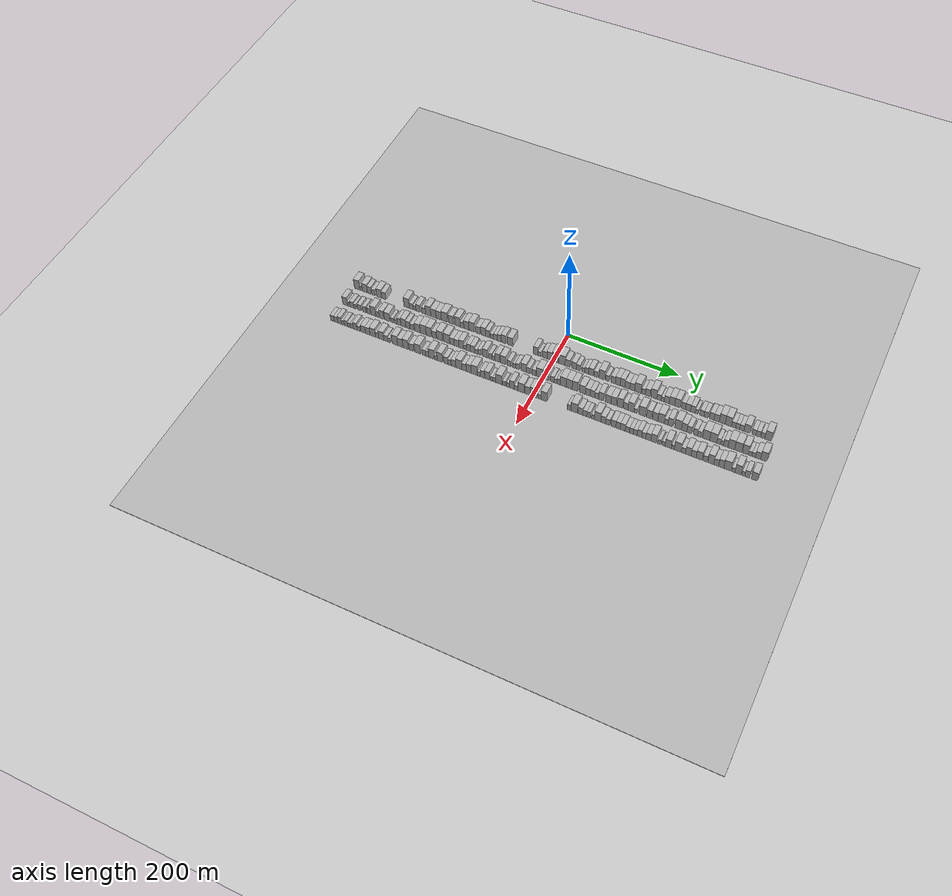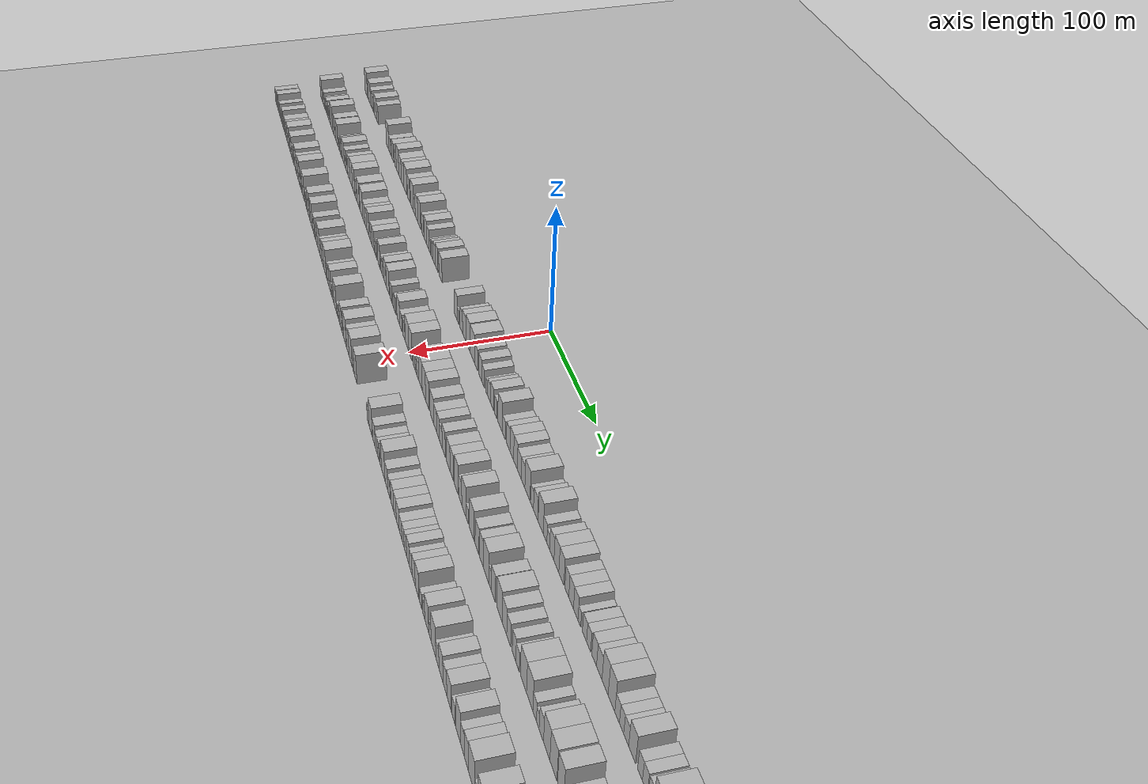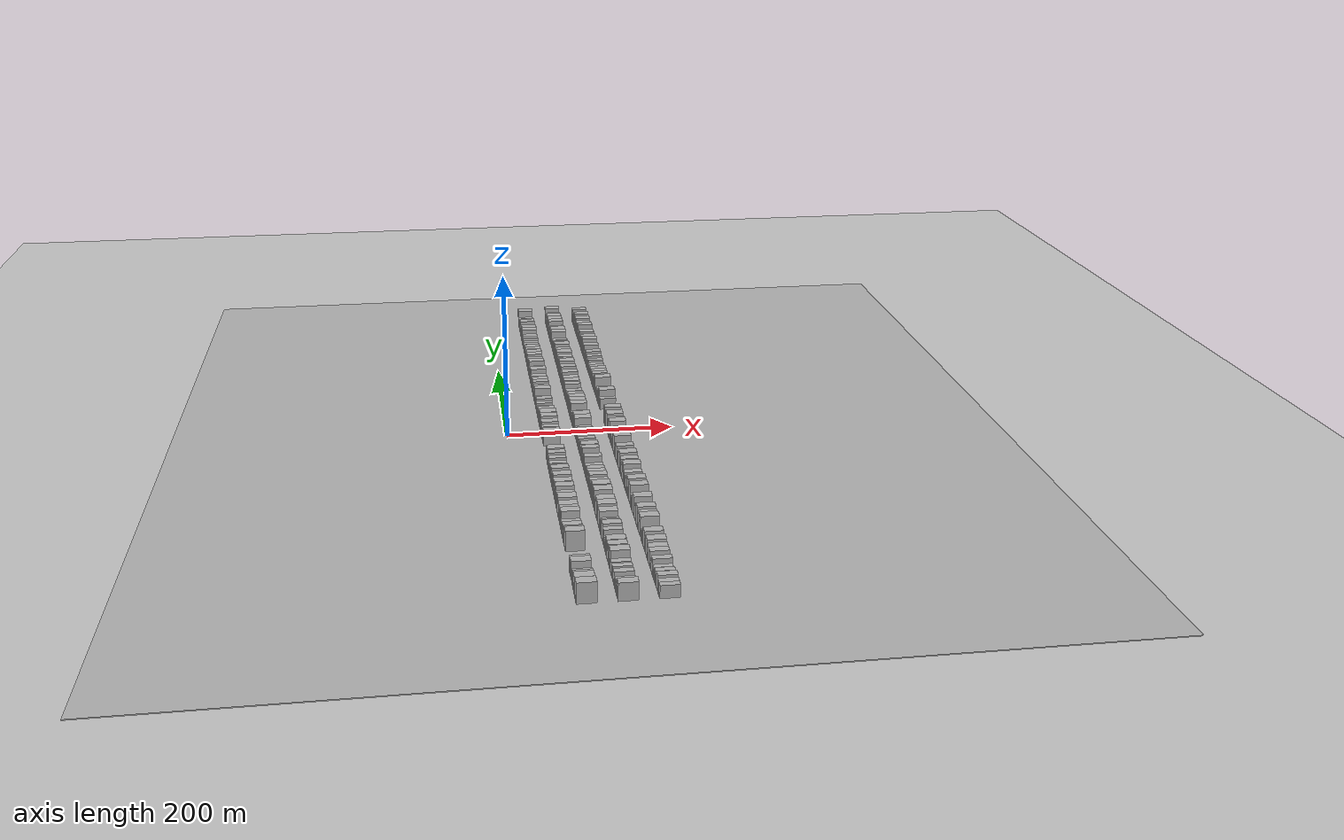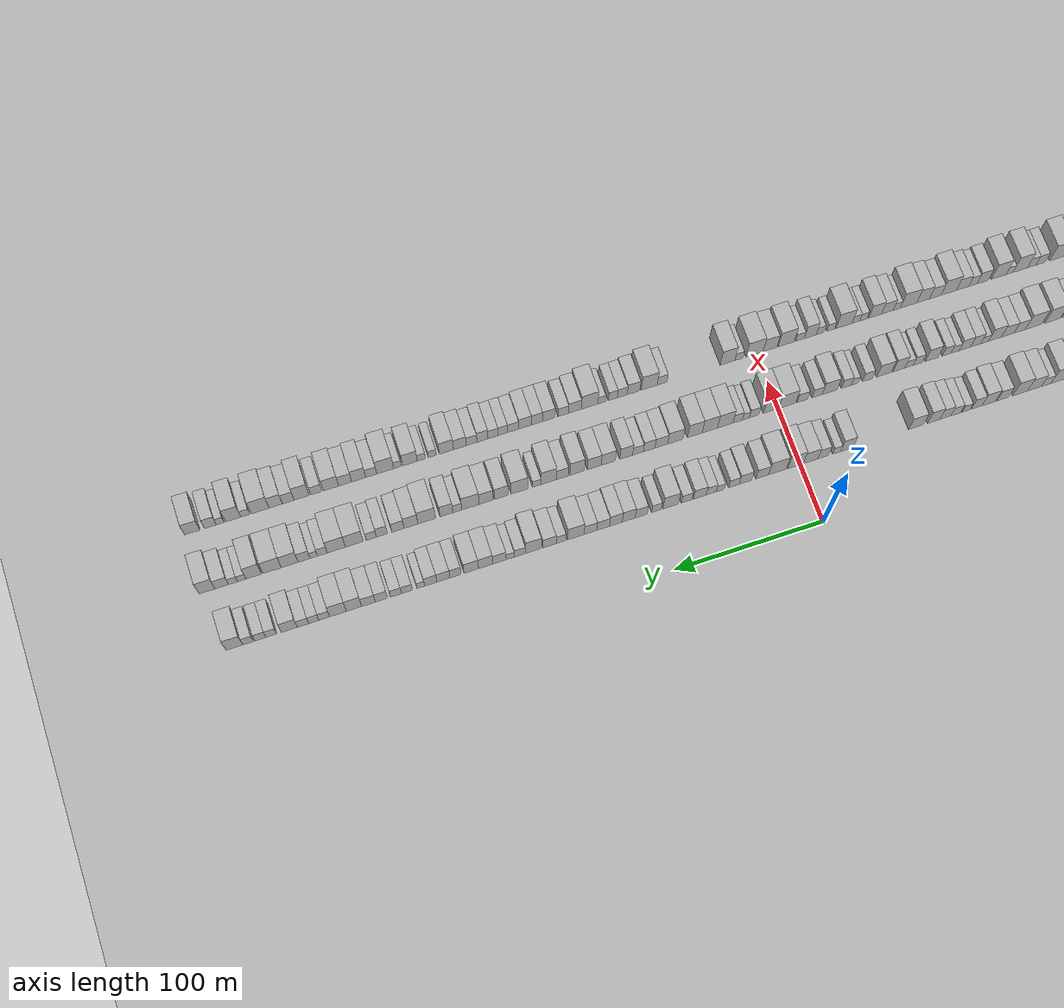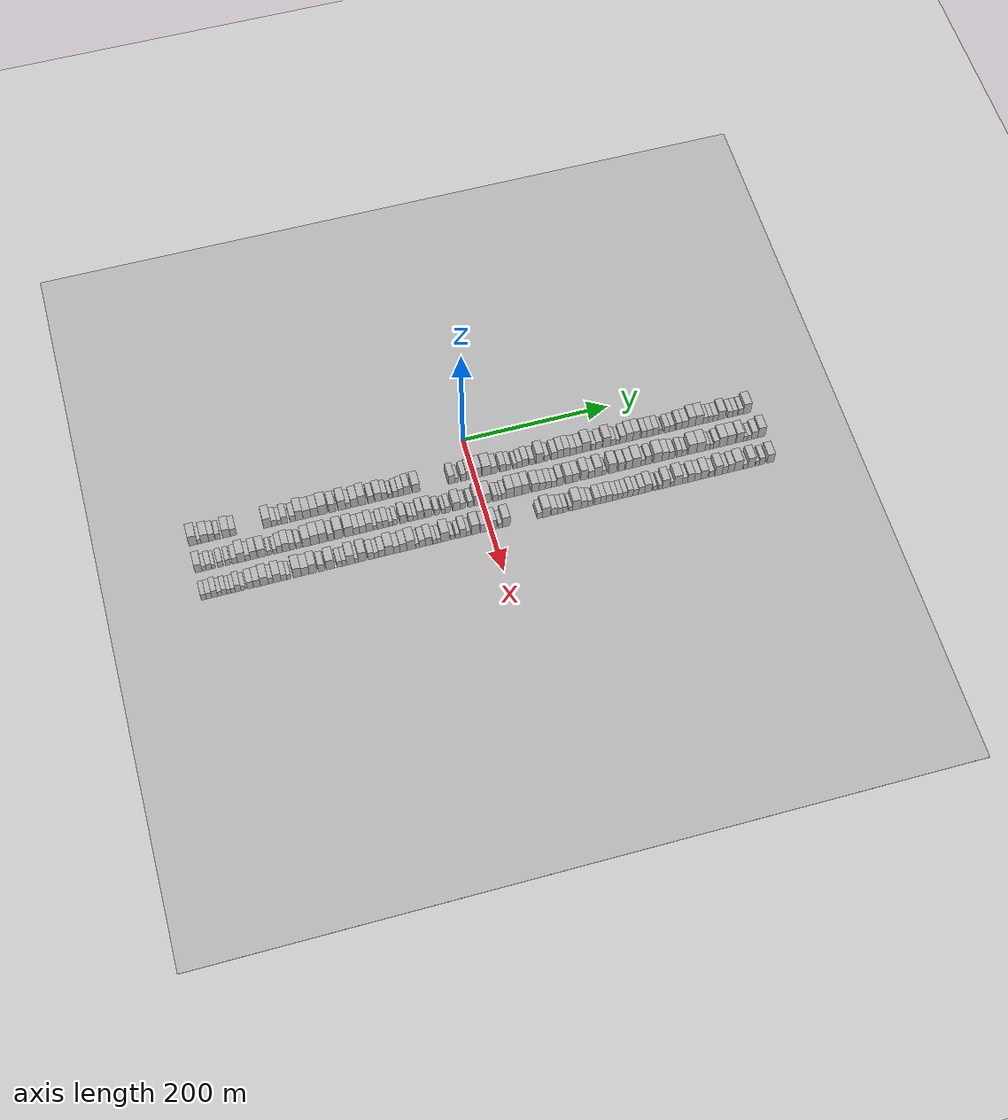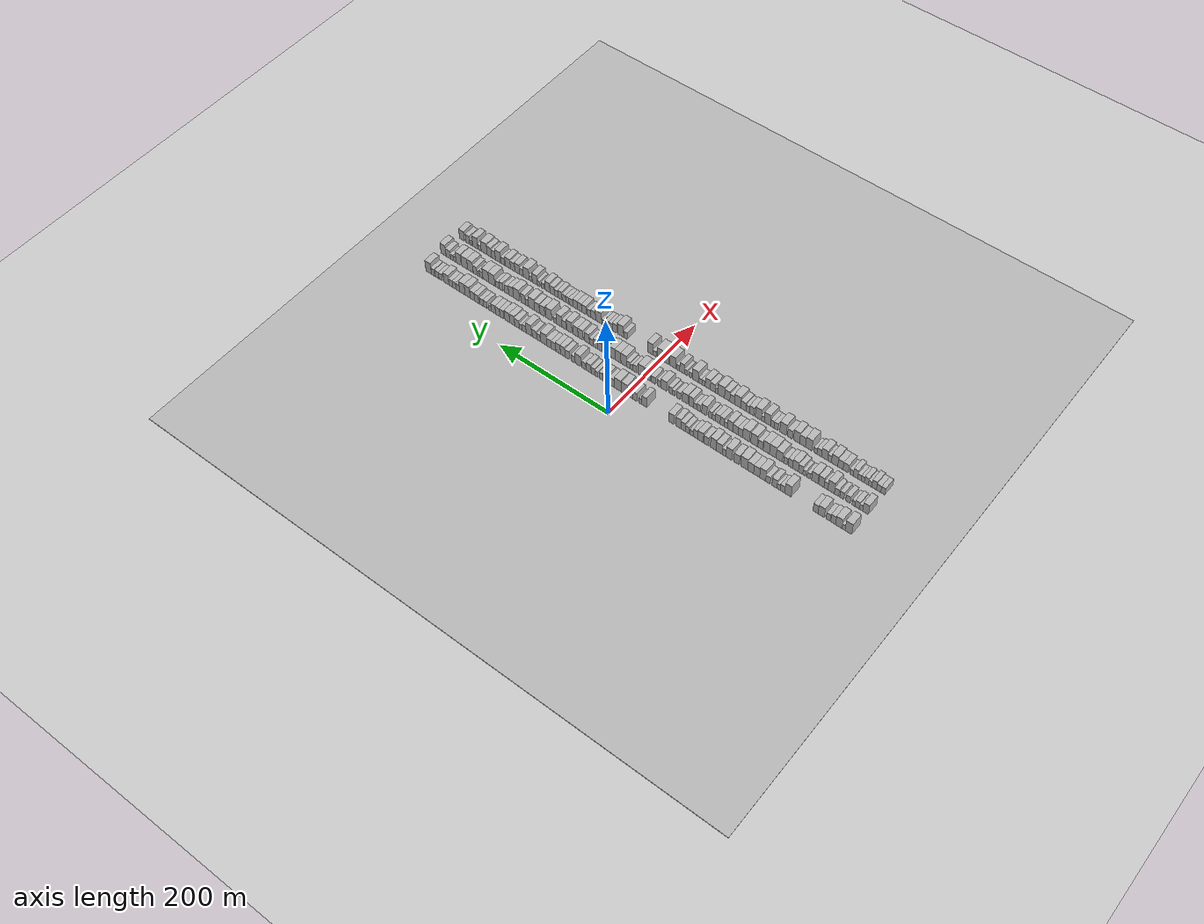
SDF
<?xml version="1.0" encoding="utf-8"?>

<sdf version="1.6">

   <world name="default">

      <gui fullscreen="0">

         <camera name="user_camera">

            <pose>-15 0 4.57585 0 0 0</pose>

            <view_controller>orbit</view_controller>

         </camera>

      </gui>

      <scene>

         <sky>

           <clouds>

             <speed>12</speed>

           </clouds>

         </sky>

         <ambient>0.4 0.4 0.4 1</ambient>

         <background>0.7 0.7 0.7 1</background>

         <shadows>1</shadows>

      </scene>

      <gravity>0 0 -9.8066</gravity>

      <magnetic_field>6e-06 2.3e-05 -4.2e-05</magnetic_field>

      <physics default="0" name="default_physics" type="ode">

         <ode>

            <solver>

               <type>quick</type>

               <iters>10</iters>

               <sor>1.0</sor>

               <use_dynamic_moi_rescaling>0</use_dynamic_moi_rescaling>

            </solver>

            <constraints>

               <cfm>0</cfm>

               <erp>0.2</erp>

               <contact_max_correcting_vel>100</contact_max_correcting_vel>

               <contact_surface_layer>0.001</contact_surface_layer>

            </constraints>

         </ode>

         <max_step_size>0.004</max_step_size>

         <real_time_factor>1</real_time_factor>

         <real_time_update_rate>250</real_time_update_rate>

      </physics>

      <light name="sun" type="directional">

         <cast_shadows>1</cast_shadows>

         <pose>0 0 10 0 0 0</pose>

         <diffuse>0.8 0.8 0.8 1</diffuse>

         <specular>0.2 0.2 0.2 1</specular>

         <attenuation>

            <range>1000</range>

            <constant>0.9</constant>

            <linear>0.01</linear>

            <quadratic>0.001</quadratic>

         </attenuation>

         <direction>-0.5 0.1 -0.9</direction>

      </light>

      <include>

         <name>ground_plane_1</name>

         <uri>model://HANNAS_ground_plane</uri>

         <pose>0 0 0  0 0 0</pose>

      </include>

      <include>

         <name>ground_plane_2</name>

         <uri>model://HANNAS_ground_plane</uri>

         <pose>100 0 0  0 0 0</pose>

      </include>

      <model name="building_1">

         <static>1</static>

         <pose frame="">50.0000 -374.6131 0 0.000000 0.000000 0.000000</pose>

         <link name="link">

            <pose frame="">0 0 12.00 0 0 0</pose>

            <collision name="collision">

               <geometry>

                  <box>

                     <size>20.0000 10.7738 24.0000</size>

                  </box>

               </geometry>

               <max_contacts>10</max_contacts>

               <surface>

                  <contact>

                     <ode/>

                  </contact>

                  <bounce/>

                  <friction>

                     <torsional>

                        <ode/>

                     </torsional>

                     <ode/>

                  </friction>

               </surface>

            </collision>

            <visual name="visual">

               <cast_shadows>0</cast_shadows>

               <geometry>

                  <box>

                     <size>20.0000 10.7738 24.0000</size>

                  </box>

               </geometry>

               <material>

                  <script>

                     <uri>model://HANNAS_wall/materials/scripts</uri>

                     <uri>model://HANNAS_wall/materials/textures</uri>

                     <name>vrc/HANNAS_wall</name>

                  </script>

               </material>

            </visual>

            <self_collide>0</self_collide>

            <enable_wind>0</enable_wind>

            <kinematic>0</kinematic>

         </link>

      </model>

      <model name="building_2">

         <static>1</static>

         <pose frame="">50.0000 -366.7798 0 0.000000 0.000000 0.000000</pose>

         <link name="link">

            <pose frame="">0 0 6.00 0 0 0</pose>

            <collision name="collision">

               <geometry>

                  <box>

                     <size>20.0000 4.8928 12.0000</size>

                  </box>

               </geometry>

               <max_contacts>10</max_contacts>

               <surface>

                  <contact>

                     <ode/>

                  </contact>

                  <bounce/>

                  <friction>

                     <torsional>

                        <ode/>

                     </torsional>

                     <ode/>

                  </friction>

               </surface>

            </collision>

            <visual name="visual">

               <cast_shadows>0</cast_shadows>

               <geometry>

                  <box>

                     <size>20.0000 4.8928 12.0000</size>

                  </box>

               </geometry>

               <material>

                  <script>

                     <uri>model://HANNAS_wall/materials/scripts</uri>

                     <uri>model://HANNAS_wall/materials/textures</uri>

                     <name>vrc/HANNAS_wall</name>

                  </script>

               </material>

            </visual>

            <self_collide>0</self_collide>

            <enable_wind>0</enable_wind>

            <kinematic>0</kinematic>

         </link>

      </model>

      <model name="building_3">

         <static>1</static>

         <pose frame="">50.0000 -359.2430 0 0.000000 0.000000 0.000000</pose>

         <link name="link">

            <pose frame="">0 0 10.50 0 0 0</pose>

            <collision name="collision">

               <geometry>

                  <box>

                     <size>20.0000 10.1808 21.0000</size>

                  </box>

               </geometry>

               <max_contacts>10</max_contacts>

               <surface>

                  <contact>

                     <ode/>

                  </contact>

                  <bounce/>

                  <friction>

                     <torsional>

                        <ode/>

                     </torsional>

                     <ode/>

                  </friction>

               </surface>

            </collision>

            <visual name="visual">

               <cast_shadows>0</cast_shadows>

               <geometry>

                  <box>

                     <size>20.0000 10.1808 21.0000</size>

                  </box>

               </geometry>

               <material>

                  <script>

                     <uri>model://HANNAS_wall/materials/scripts</uri>

                     <uri>model://HANNAS_wall/materials/textures</uri>

                     <name>vrc/HANNAS_wall</name>

                  </script>

               </material>

            </visual>

            <self_collide>0</self_collide>

            <enable_wind>0</enable_wind>

            <kinematic>0</kinematic>

         </link>

      </model>

      <model name="building_4">

         <static>1</static>

         <pose frame="">50.0000 -350.2289 0 0.000000 0.000000 0.000000</pose>

         <link name="link">

            <pose frame="">0 0 9.00 0 0 0</pose>

            <collision name="collision">

               <geometry>

                  <box>

                     <size>20.0000 7.8472 18.0000</size>

                  </box>

               </geometry>

               <max_contacts>10</max_contacts>

               <surface>

                  <contact>

                     <ode/>

                  </contact>

                  <bounce/>

                  <friction>

                     <torsional>

                        <ode/>

                     </torsional>

                     <ode/>

                  </friction>

               </surface>

            </collision>

            <visual name="visual">

               <cast_shadows>0</cast_shadows>

               <geometry>

                  <box>

                     <size>20.0000 7.8472 18.0000</size>

                  </box>

               </geometry>

               <material>

                  <script>

                     <uri>model://HANNAS_wall/materials/scripts</uri>

                     <uri>model://HANNAS_wall/materials/textures</uri>

                     <name>vrc/HANNAS_wall</name>

                  </script>

               </material>

            </visual>

            <self_collide>0</self_collide>

            <enable_wind>0</enable_wind>

            <kinematic>0</kinematic>

         </link>

      </model>

      <model name="building_5">

         <static>1</static>

         <pose frame="">50.0000 -342.1552 0 0.000000 0.000000 0.000000</pose>

         <link name="link">

            <pose frame="">0 0 7.50 0 0 0</pose>

            <collision name="collision">

               <geometry>

                  <box>

                     <size>20.0000 6.3002 15.0000</size>

                  </box>

               </geometry>

               <max_contacts>10</max_contacts>

               <surface>

                  <contact>

                     <ode/>

                  </contact>

                  <bounce/>

                  <friction>

                     <torsional>

                        <ode/>

                     </torsional>

                     <ode/>

                  </friction>

               </surface>

            </collision>

            <visual name="visual">

               <cast_shadows>0</cast_shadows>

               <geometry>

                  <box>

                     <size>20.0000 6.3002 15.0000</size>

                  </box>

               </geometry>

               <material>

                  <script>

                     <uri>model://HANNAS_wall/materials/scripts</uri>

                     <uri>model://HANNAS_wall/materials/textures</uri>

                     <name>vrc/HANNAS_wall</name>

                  </script>

               </material>

            </visual>

            <self_collide>0</self_collide>

            <enable_wind>0</enable_wind>

            <kinematic>0</kinematic>

         </link>

      </model>

      <model name="building_6">

         <static>1</static>

         <pose frame="">50.0000 -330.9672 0 0.000000 0.000000 0.000000</pose>

         <link name="link">

            <pose frame="">0 0 10.50 0 0 0</pose>

            <collision name="collision">

               <geometry>

                  <box>

                     <size>20.0000 10.0759 21.0000</size>

                  </box>

               </geometry>

               <max_contacts>10</max_contacts>

               <surface>

                  <contact>

                     <ode/>

                  </contact>

                  <bounce/>

                  <friction>

                     <torsional>

                        <ode/>

                     </torsional>

                     <ode/>

                  </friction>

               </surface>

            </collision>

            <visual name="visual">

               <cast_shadows>0</cast_shadows>

               <geometry>

                  <box>

                     <size>20.0000 10.0759 21.0000</size>

                  </box>

               </geometry>

               <material>

                  <script>

                     <uri>model://HANNAS_wall/materials/scripts</uri>

                     <uri>model://HANNAS_wall/materials/textures</uri>

                     <name>vrc/HANNAS_wall</name>

                  </script>

               </material>

            </visual>

            <self_collide>0</self_collide>

            <enable_wind>0</enable_wind>

            <kinematic>0</kinematic>

         </link>

      </model>

      <model name="building_7">

         <static>1</static>

         <pose frame="">50.0000 -321.8414 0 0.000000 0.000000 0.000000</pose>

         <link name="link">

            <pose frame="">0 0 9.00 0 0 0</pose>

            <collision name="collision">

               <geometry>

                  <box>

                     <size>20.0000 8.1757 18.0000</size>

                  </box>

               </geometry>

               <max_contacts>10</max_contacts>

               <surface>

                  <contact>

                     <ode/>

                  </contact>

                  <bounce/>

                  <friction>

                     <torsional>

                        <ode/>

                     </torsional>

                     <ode/>

                  </friction>

               </surface>

            </collision>

            <visual name="visual">

               <cast_shadows>0</cast_shadows>

               <geometry>

                  <box>

                     <size>20.0000 8.1757 18.0000</size>

                  </box>

               </geometry>

               <material>

                  <script>

                     <uri>model://HANNAS_wall/materials/scripts</uri>

                     <uri>model://HANNAS_wall/materials/textures</uri>

                     <name>vrc/HANNAS_wall</name>

                  </script>

               </material>

            </visual>

            <self_collide>0</self_collide>

            <enable_wind>0</enable_wind>

            <kinematic>0</kinematic>

         </link>

      </model>

      <model name="building_8">

         <static>1</static>

         <pose frame="">50.0000 -276.8785 0 0.000000 0.000000 0.000000</pose>

         <link name="link">

            <pose frame="">0 0 12.00 0 0 0</pose>

            <collision name="collision">

               <geometry>

                  <box>

                     <size>20.0000 10.5833 24.0000</size>

                  </box>

               </geometry>

               <max_contacts>10</max_contacts>

               <surface>

                  <contact>

                     <ode/>

                  </contact>

                  <bounce/>

                  <friction>

                     <torsional>

                        <ode/>

                     </torsional>

                     <ode/>

                  </friction>

               </surface>

            </collision>

            <visual name="visual">

               <cast_shadows>0</cast_shadows>

               <geometry>

                  <box>

                     <size>20.0000 10.5833 24.0000</size>

                  </box>

               </geometry>

               <material>

                  <script>

                     <uri>model://HANNAS_wall/materials/scripts</uri>

                     <uri>model://HANNAS_wall/materials/textures</uri>

                     <name>vrc/HANNAS_wall</name>

                  </script>

               </material>

            </visual>

            <self_collide>0</self_collide>

            <enable_wind>0</enable_wind>

            <kinematic>0</kinematic>

         </link>

      </model>

      <model name="building_9">

         <static>1</static>

         <pose frame="">50.0000 -267.9536 0 0.000000 0.000000 0.000000</pose>

         <link name="link">

            <pose frame="">0 0 7.50 0 0 0</pose>

            <collision name="collision">

               <geometry>

                  <box>

                     <size>20.0000 7.2664 15.0000</size>

                  </box>

               </geometry>

               <max_contacts>10</max_contacts>

               <surface>

                  <contact>

                     <ode/>

                  </contact>

                  <bounce/>

                  <friction>

                     <torsional>

                        <ode/>

                     </torsional>

                     <ode/>

                  </friction>

               </surface>

            </collision>

            <visual name="visual">

               <cast_shadows>0</cast_shadows>

               <geometry>

                  <box>

                     <size>20.0000 7.2664 15.0000</size>

                  </box>

               </geometry>

               <material>

                  <script>

                     <uri>model://HANNAS_wall/materials/scripts</uri>

                     <uri>model://HANNAS_wall/materials/textures</uri>

                     <name>vrc/HANNAS_wall</name>

                  </script>

               </material>

            </visual>

            <self_collide>0</self_collide>

            <enable_wind>0</enable_wind>

            <kinematic>0</kinematic>

         </link>

      </model>

      <model name="building_10">

         <static>1</static>

         <pose frame="">50.0000 -261.5706 0 0.000000 0.000000 0.000000</pose>

         <link name="link">

            <pose frame="">0 0 6.00 0 0 0</pose>

            <collision name="collision">

               <geometry>

                  <box>

                     <size>20.0000 5.4996 12.0000</size>

                  </box>

               </geometry>

               <max_contacts>10</max_contacts>

               <surface>

                  <contact>

                     <ode/>

                  </contact>

                  <bounce/>

                  <friction>

                     <torsional>

                        <ode/>

                     </torsional>

                     <ode/>

                  </friction>

               </surface>

            </collision>

            <visual name="visual">

               <cast_shadows>0</cast_shadows>

               <geometry>

                  <box>

                     <size>20.0000 5.4996 12.0000</size>

                  </box>

               </geometry>

               <material>

                  <script>

                     <uri>model://HANNAS_wall/materials/scripts</uri>

                     <uri>model://HANNAS_wall/materials/textures</uri>

                     <name>vrc/HANNAS_wall</name>

                  </script>

               </material>

            </visual>

            <self_collide>0</self_collide>

            <enable_wind>0</enable_wind>

            <kinematic>0</kinematic>

         </link>

      </model>

      <model name="building_11">

         <static>1</static>

         <pose frame="">50.0000 -254.6667 0 0.000000 0.000000 0.000000</pose>

         <link name="link">

            <pose frame="">0 0 9.00 0 0 0</pose>

            <collision name="collision">

               <geometry>

                  <box>

                     <size>20.0000 8.3083 18.0000</size>

                  </box>

               </geometry>

               <max_contacts>10</max_contacts>

               <surface>

                  <contact>

                     <ode/>

                  </contact>

                  <bounce/>

                  <friction>

                     <torsional>

                        <ode/>

                     </torsional>

                     <ode/>

                  </friction>

               </surface>

            </collision>

            <visual name="visual">

               <cast_shadows>0</cast_shadows>

               <geometry>

                  <box>

                     <size>20.0000 8.3083 18.0000</size>

                  </box>

               </geometry>

               <material>

                  <script>

                     <uri>model://HANNAS_wall/materials/scripts</uri>

                     <uri>model://HANNAS_wall/materials/textures</uri>

                     <name>vrc/HANNAS_wall</name>

                  </script>

               </material>

            </visual>

            <self_collide>0</self_collide>

            <enable_wind>0</enable_wind>

            <kinematic>0</kinematic>

         </link>

      </model>

      <model name="building_12">

         <static>1</static>

         <pose frame="">50.0000 -243.8017 0 0.000000 0.000000 0.000000</pose>

         <link name="link">

            <pose frame="">0 0 7.50 0 0 0</pose>

            <collision name="collision">

               <geometry>

                  <box>

                     <size>20.0000 7.4218 15.0000</size>

                  </box>

               </geometry>

               <max_contacts>10</max_contacts>

               <surface>

                  <contact>

                     <ode/>

                  </contact>

                  <bounce/>

                  <friction>

                     <torsional>

                        <ode/>

                     </torsional>

                     <ode/>

                  </friction>

               </surface>

            </collision>

            <visual name="visual">

               <cast_shadows>0</cast_shadows>

               <geometry>

                  <box>

                     <size>20.0000 7.4218 15.0000</size>

                  </box>

               </geometry>

               <material>

                  <script>

                     <uri>model://HANNAS_wall/materials/scripts</uri>

                     <uri>model://HANNAS_wall/materials/textures</uri>

                     <name>vrc/HANNAS_wall</name>

                  </script>

               </material>

            </visual>

            <self_collide>0</self_collide>

            <enable_wind>0</enable_wind>

            <kinematic>0</kinematic>

         </link>

      </model>

      <model name="building_13">

         <static>1</static>

         <pose frame="">50.0000 -235.0872 0 0.000000 0.000000 0.000000</pose>

         <link name="link">

            <pose frame="">0 0 12.00 0 0 0</pose>

            <collision name="collision">

               <geometry>

                  <box>

                     <size>20.0000 10.0071 24.0000</size>

                  </box>

               </geometry>

               <max_contacts>10</max_contacts>

               <surface>

                  <contact>

                     <ode/>

                  </contact>

                  <bounce/>

                  <friction>

                     <torsional>

                        <ode/>

                     </torsional>

                     <ode/>

                  </friction>

               </surface>

            </collision>

            <visual name="visual">

               <cast_shadows>0</cast_shadows>

               <geometry>

                  <box>

                     <size>20.0000 10.0071 24.0000</size>

                  </box>

               </geometry>

               <material>

                  <script>

                     <uri>model://HANNAS_wall/materials/scripts</uri>

                     <uri>model://HANNAS_wall/materials/textures</uri>

                     <name>vrc/HANNAS_wall</name>

                  </script>

               </material>

            </visual>

            <self_collide>0</self_collide>

            <enable_wind>0</enable_wind>

            <kinematic>0</kinematic>

         </link>

      </model>

      <model name="building_14">

         <static>1</static>

         <pose frame="">50.0000 -225.0234 0 0.000000 0.000000 0.000000</pose>

         <link name="link">

            <pose frame="">0 0 10.50 0 0 0</pose>

            <collision name="collision">

               <geometry>

                  <box>

                     <size>20.0000 10.1206 21.0000</size>

                  </box>

               </geometry>

               <max_contacts>10</max_contacts>

               <surface>

                  <contact>

                     <ode/>

                  </contact>

                  <bounce/>

                  <friction>

                     <torsional>

                        <ode/>

                     </torsional>

                     <ode/>

                  </friction>

               </surface>

            </collision>

            <visual name="visual">

               <cast_shadows>0</cast_shadows>

               <geometry>

                  <box>

                     <size>20.0000 10.1206 21.0000</size>

                  </box>

               </geometry>

               <material>

                  <script>

                     <uri>model://HANNAS_wall/materials/scripts</uri>

                     <uri>model://HANNAS_wall/materials/textures</uri>

                     <name>vrc/HANNAS_wall</name>

                  </script>

               </material>

            </visual>

            <self_collide>0</self_collide>

            <enable_wind>0</enable_wind>

            <kinematic>0</kinematic>

         </link>

      </model>

      <model name="building_15">

         <static>1</static>

         <pose frame="">50.0000 -214.9451 0 0.000000 0.000000 0.000000</pose>

         <link name="link">

            <pose frame="">0 0 10.50 0 0 0</pose>

            <collision name="collision">

               <geometry>

                  <box>

                     <size>20.0000 10.0358 21.0000</size>

                  </box>

               </geometry>

               <max_contacts>10</max_contacts>

               <surface>

                  <contact>

                     <ode/>

                  </contact>

                  <bounce/>

                  <friction>

                     <torsional>

                        <ode/>

                     </torsional>

                     <ode/>

                  </friction>

               </surface>

            </collision>

            <visual name="visual">

               <cast_shadows>0</cast_shadows>

               <geometry>

                  <box>

                     <size>20.0000 10.0358 21.0000</size>

                  </box>

               </geometry>

               <material>

                  <script>

                     <uri>model://HANNAS_wall/materials/scripts</uri>

                     <uri>model://HANNAS_wall/materials/textures</uri>

                     <name>vrc/HANNAS_wall</name>

                  </script>

               </material>

            </visual>

            <self_collide>0</self_collide>

            <enable_wind>0</enable_wind>

            <kinematic>0</kinematic>

         </link>

      </model>

      <model name="building_16">

         <static>1</static>

         <pose frame="">50.0000 -203.9846 0 0.000000 0.000000 0.000000</pose>

         <link name="link">

            <pose frame="">0 0 12.00 0 0 0</pose>

            <collision name="collision">

               <geometry>

                  <box>

                     <size>20.0000 11.8852 24.0000</size>

                  </box>

               </geometry>

               <max_contacts>10</max_contacts>

               <surface>

                  <contact>

                     <ode/>

                  </contact>

                  <bounce/>

                  <friction>

                     <torsional>

                        <ode/>

                     </torsional>

                     <ode/>

                  </friction>

               </surface>

            </collision>

            <visual name="visual">

               <cast_shadows>0</cast_shadows>

               <geometry>

                  <box>

                     <size>20.0000 11.8852 24.0000</size>

                  </box>

               </geometry>

               <material>

                  <script>

                     <uri>model://HANNAS_wall/materials/scripts</uri>

                     <uri>model://HANNAS_wall/materials/textures</uri>

                     <name>vrc/HANNAS_wall</name>

                  </script>

               </material>

            </visual>

            <self_collide>0</self_collide>

            <enable_wind>0</enable_wind>

            <kinematic>0</kinematic>

         </link>

      </model>

      <model name="building_17">

         <static>1</static>

         <pose frame="">50.0000 -191.4185 0 0.000000 0.000000 0.000000</pose>

         <link name="link">

            <pose frame="">0 0 10.50 0 0 0</pose>

            <collision name="collision">

               <geometry>

                  <box>

                     <size>20.0000 9.2469 21.0000</size>

                  </box>

               </geometry>

               <max_contacts>10</max_contacts>

               <surface>

                  <contact>

                     <ode/>

                  </contact>

                  <bounce/>

                  <friction>

                     <torsional>

                        <ode/>

                     </torsional>

                     <ode/>

                  </friction>

               </surface>

            </collision>

            <visual name="visual">

               <cast_shadows>0</cast_shadows>

               <geometry>

                  <box>

                     <size>20.0000 9.2469 21.0000</size>

                  </box>

               </geometry>

               <material>

                  <script>

                     <uri>model://HANNAS_wall/materials/scripts</uri>

                     <uri>model://HANNAS_wall/materials/textures</uri>

                     <name>vrc/HANNAS_wall</name>

                  </script>

               </material>

            </visual>

            <self_collide>0</self_collide>

            <enable_wind>0</enable_wind>

            <kinematic>0</kinematic>

         </link>

      </model>

      <model name="building_18">

         <static>1</static>

         <pose frame="">50.0000 -178.6368 0 0.000000 0.000000 0.000000</pose>

         <link name="link">

            <pose frame="">0 0 12.00 0 0 0</pose>

            <collision name="collision">

               <geometry>

                  <box>

                     <size>20.0000 10.3165 24.0000</size>

                  </box>

               </geometry>

               <max_contacts>10</max_contacts>

               <surface>

                  <contact>

                     <ode/>

                  </contact>

                  <bounce/>

                  <friction>

                     <torsional>

                        <ode/>

                     </torsional>

                     <ode/>

                  </friction>

               </surface>

            </collision>

            <visual name="visual">

               <cast_shadows>0</cast_shadows>

               <geometry>

                  <box>

                     <size>20.0000 10.3165 24.0000</size>

                  </box>

               </geometry>

               <material>

                  <script>

                     <uri>model://HANNAS_wall/materials/scripts</uri>

                     <uri>model://HANNAS_wall/materials/textures</uri>

                     <name>vrc/HANNAS_wall</name>

                  </script>

               </material>

            </visual>

            <self_collide>0</self_collide>

            <enable_wind>0</enable_wind>

            <kinematic>0</kinematic>

         </link>

      </model>

      <model name="building_19">

         <static>1</static>

         <pose frame="">50.0000 -170.1284 0 0.000000 0.000000 0.000000</pose>

         <link name="link">

            <pose frame="">0 0 7.50 0 0 0</pose>

            <collision name="collision">

               <geometry>

                  <box>

                     <size>20.0000 6.7004 15.0000</size>

                  </box>

               </geometry>

               <max_contacts>10</max_contacts>

               <surface>

                  <contact>

                     <ode/>

                  </contact>

                  <bounce/>

                  <friction>

                     <torsional>

                        <ode/>

                     </torsional>

                     <ode/>

                  </friction>

               </surface>

            </collision>

            <visual name="visual">

               <cast_shadows>0</cast_shadows>

               <geometry>

                  <box>

                     <size>20.0000 6.7004 15.0000</size>

                  </box>

               </geometry>

               <material>

                  <script>

                     <uri>model://HANNAS_wall/materials/scripts</uri>

                     <uri>model://HANNAS_wall/materials/textures</uri>

                     <name>vrc/HANNAS_wall</name>

                  </script>

               </material>

            </visual>

            <self_collide>0</self_collide>

            <enable_wind>0</enable_wind>

            <kinematic>0</kinematic>

         </link>

      </model>

      <model name="building_20">

         <static>1</static>

         <pose frame="">50.0000 -161.8568 0 0.000000 0.000000 0.000000</pose>

         <link name="link">

            <pose frame="">0 0 10.50 0 0 0</pose>

            <collision name="collision">

               <geometry>

                  <box>

                     <size>20.0000 9.8428 21.0000</size>

                  </box>

               </geometry>

               <max_contacts>10</max_contacts>

               <surface>

                  <contact>

                     <ode/>

                  </contact>

                  <bounce/>

                  <friction>

                     <torsional>

                        <ode/>

                     </torsional>

                     <ode/>

                  </friction>

               </surface>

            </collision>

            <visual name="visual">

               <cast_shadows>0</cast_shadows>

               <geometry>

                  <box>

                     <size>20.0000 9.8428 21.0000</size>

                  </box>

               </geometry>

               <material>

                  <script>

                     <uri>model://HANNAS_wall/materials/scripts</uri>

                     <uri>model://HANNAS_wall/materials/textures</uri>

                     <name>vrc/HANNAS_wall</name>

                  </script>

               </material>

            </visual>

            <self_collide>0</self_collide>

            <enable_wind>0</enable_wind>

            <kinematic>0</kinematic>

         </link>

      </model>

      <model name="building_21">

         <static>1</static>

         <pose frame="">50.0000 -151.8738 0 0.000000 0.000000 0.000000</pose>

         <link name="link">

            <pose frame="">0 0 12.00 0 0 0</pose>

            <collision name="collision">

               <geometry>

                  <box>

                     <size>20.0000 10.1233 24.0000</size>

                  </box>

               </geometry>

               <max_contacts>10</max_contacts>

               <surface>

                  <contact>

                     <ode/>

                  </contact>

                  <bounce/>

                  <friction>

                     <torsional>

                        <ode/>

                     </torsional>

                     <ode/>

                  </friction>

               </surface>

            </collision>

            <visual name="visual">

               <cast_shadows>0</cast_shadows>

               <geometry>

                  <box>

                     <size>20.0000 10.1233 24.0000</size>

                  </box>

               </geometry>

               <material>

                  <script>

                     <uri>model://HANNAS_wall/materials/scripts</uri>

                     <uri>model://HANNAS_wall/materials/textures</uri>

                     <name>vrc/HANNAS_wall</name>

                  </script>

               </material>

            </visual>

            <self_collide>0</self_collide>

            <enable_wind>0</enable_wind>

            <kinematic>0</kinematic>

         </link>

      </model>

      <model name="building_22">

         <static>1</static>

         <pose frame="">50.0000 -139.7485 0 0.000000 0.000000 0.000000</pose>

         <link name="link">

            <pose frame="">0 0 9.00 0 0 0</pose>

            <collision name="collision">

               <geometry>

                  <box>

                     <size>20.0000 8.1273 18.0000</size>

                  </box>

               </geometry>

               <max_contacts>10</max_contacts>

               <surface>

                  <contact>

                     <ode/>

                  </contact>

                  <bounce/>

                  <friction>

                     <torsional>

                        <ode/>

                     </torsional>

                     <ode/>

                  </friction>

               </surface>

            </collision>

            <visual name="visual">

               <cast_shadows>0</cast_shadows>

               <geometry>

                  <box>

                     <size>20.0000 8.1273 18.0000</size>

                  </box>

               </geometry>

               <material>

                  <script>

                     <uri>model://HANNAS_wall/materials/scripts</uri>

                     <uri>model://HANNAS_wall/materials/textures</uri>

                     <name>vrc/HANNAS_wall</name>

                  </script>

               </material>

            </visual>

            <self_collide>0</self_collide>

            <enable_wind>0</enable_wind>

            <kinematic>0</kinematic>

         </link>

      </model>

      <model name="building_23">

         <static>1</static>

         <pose frame="">50.0000 -129.9938 0 0.000000 0.000000 0.000000</pose>

         <link name="link">

            <pose frame="">0 0 10.50 0 0 0</pose>

            <collision name="collision">

               <geometry>

                  <box>

                     <size>20.0000 9.3820 21.0000</size>

                  </box>

               </geometry>

               <max_contacts>10</max_contacts>

               <surface>

                  <contact>

                     <ode/>

                  </contact>

                  <bounce/>

                  <friction>

                     <torsional>

                        <ode/>

                     </torsional>

                     <ode/>

                  </friction>

               </surface>

            </collision>

            <visual name="visual">

               <cast_shadows>0</cast_shadows>

               <geometry>

                  <box>

                     <size>20.0000 9.3820 21.0000</size>

                  </box>

               </geometry>

               <material>

                  <script>

                     <uri>model://HANNAS_wall/materials/scripts</uri>

                     <uri>model://HANNAS_wall/materials/textures</uri>

                     <name>vrc/HANNAS_wall</name>

                  </script>

               </material>

            </visual>

            <self_collide>0</self_collide>

            <enable_wind>0</enable_wind>

            <kinematic>0</kinematic>

         </link>

      </model>

      <model name="building_24">

         <static>1</static>

         <pose frame="">50.0000 -121.5938 0 0.000000 0.000000 0.000000</pose>

         <link name="link">

            <pose frame="">0 0 9.00 0 0 0</pose>

            <collision name="collision">

               <geometry>

                  <box>

                     <size>20.0000 7.4181 18.0000</size>

                  </box>

               </geometry>

               <max_contacts>10</max_contacts>

               <surface>

                  <contact>

                     <ode/>

                  </contact>

                  <bounce/>

                  <friction>

                     <torsional>

                        <ode/>

                     </torsional>

                     <ode/>

                  </friction>

               </surface>

            </collision>

            <visual name="visual">

               <cast_shadows>0</cast_shadows>

               <geometry>

                  <box>

                     <size>20.0000 7.4181 18.0000</size>

                  </box>

               </geometry>

               <material>

                  <script>

                     <uri>model://HANNAS_wall/materials/scripts</uri>

                     <uri>model://HANNAS_wall/materials/textures</uri>

                     <name>vrc/HANNAS_wall</name>

                  </script>

               </material>

            </visual>

            <self_collide>0</self_collide>

            <enable_wind>0</enable_wind>

            <kinematic>0</kinematic>

         </link>

      </model>

      <model name="building_25">

         <static>1</static>

         <pose frame="">50.0000 -114.1592 0 0.000000 0.000000 0.000000</pose>

         <link name="link">

            <pose frame="">0 0 6.00 0 0 0</pose>

            <collision name="collision">

               <geometry>

                  <box>

                     <size>20.0000 5.4511 12.0000</size>

                  </box>

               </geometry>

               <max_contacts>10</max_contacts>

               <surface>

                  <contact>

                     <ode/>

                  </contact>

                  <bounce/>

                  <friction>

                     <torsional>

                        <ode/>

                     </torsional>

                     <ode/>

                  </friction>

               </surface>

            </collision>

            <visual name="visual">

               <cast_shadows>0</cast_shadows>

               <geometry>

                  <box>

                     <size>20.0000 5.4511 12.0000</size>

                  </box>

               </geometry>

               <material>

                  <script>

                     <uri>model://HANNAS_wall/materials/scripts</uri>

                     <uri>model://HANNAS_wall/materials/textures</uri>

                     <name>vrc/HANNAS_wall</name>

                  </script>

               </material>

            </visual>

            <self_collide>0</self_collide>

            <enable_wind>0</enable_wind>

            <kinematic>0</kinematic>

         </link>

      </model>

      <model name="building_26">

         <static>1</static>

         <pose frame="">50.0000 -106.9795 0 0.000000 0.000000 0.000000</pose>

         <link name="link">

            <pose frame="">0 0 7.50 0 0 0</pose>

            <collision name="collision">

               <geometry>

                  <box>

                     <size>20.0000 6.9083 15.0000</size>

                  </box>

               </geometry>

               <max_contacts>10</max_contacts>

               <surface>

                  <contact>

                     <ode/>

                  </contact>

                  <bounce/>

                  <friction>

                     <torsional>

                        <ode/>

                     </torsional>

                     <ode/>

                  </friction>

               </surface>

            </collision>

            <visual name="visual">

               <cast_shadows>0</cast_shadows>

               <geometry>

                  <box>

                     <size>20.0000 6.9083 15.0000</size>

                  </box>

               </geometry>

               <material>

                  <script>

                     <uri>model://HANNAS_wall/materials/scripts</uri>

                     <uri>model://HANNAS_wall/materials/textures</uri>

                     <name>vrc/HANNAS_wall</name>

                  </script>

               </material>

            </visual>

            <self_collide>0</self_collide>

            <enable_wind>0</enable_wind>

            <kinematic>0</kinematic>

         </link>

      </model>

      <model name="building_27">

         <static>1</static>

         <pose frame="">50.0000 -99.7024 0 0.000000 0.000000 0.000000</pose>

         <link name="link">

            <pose frame="">0 0 9.00 0 0 0</pose>

            <collision name="collision">

               <geometry>

                  <box>

                     <size>20.0000 7.6459 18.0000</size>

                  </box>

               </geometry>

               <max_contacts>10</max_contacts>

               <surface>

                  <contact>

                     <ode/>

                  </contact>

                  <bounce/>

                  <friction>

                     <torsional>

                        <ode/>

                     </torsional>

                     <ode/>

                  </friction>

               </surface>

            </collision>

            <visual name="visual">

               <cast_shadows>0</cast_shadows>

               <geometry>

                  <box>

                     <size>20.0000 7.6459 18.0000</size>

                  </box>

               </geometry>

               <material>

                  <script>

                     <uri>model://HANNAS_wall/materials/scripts</uri>

                     <uri>model://HANNAS_wall/materials/textures</uri>

                     <name>vrc/HANNAS_wall</name>

                  </script>

               </material>

            </visual>

            <self_collide>0</self_collide>

            <enable_wind>0</enable_wind>

            <kinematic>0</kinematic>

         </link>

      </model>

      <model name="building_28">

         <static>1</static>

         <pose frame="">50.0000 -91.6660 0 0.000000 0.000000 0.000000</pose>

         <link name="link">

            <pose frame="">0 0 10.50 0 0 0</pose>

            <collision name="collision">

               <geometry>

                  <box>

                     <size>20.0000 8.4268 21.0000</size>

                  </box>

               </geometry>

               <max_contacts>10</max_contacts>

               <surface>

                  <contact>

                     <ode/>

                  </contact>

                  <bounce/>

                  <friction>

                     <torsional>

                        <ode/>

                     </torsional>

                     <ode/>

                  </friction>

               </surface>

            </collision>

            <visual name="visual">

               <cast_shadows>0</cast_shadows>

               <geometry>

                  <box>

                     <size>20.0000 8.4268 21.0000</size>

                  </box>

               </geometry>

               <material>

                  <script>

                     <uri>model://HANNAS_wall/materials/scripts</uri>

                     <uri>model://HANNAS_wall/materials/textures</uri>

                     <name>vrc/HANNAS_wall</name>

                  </script>

               </material>

            </visual>

            <self_collide>0</self_collide>

            <enable_wind>0</enable_wind>

            <kinematic>0</kinematic>

         </link>

      </model>

      <model name="building_29">

         <static>1</static>

         <pose frame="">50.0000 -79.3613 0 0.000000 0.000000 0.000000</pose>

         <link name="link">

            <pose frame="">0 0 10.50 0 0 0</pose>

            <collision name="collision">

               <geometry>

                  <box>

                     <size>20.0000 10.1827 21.0000</size>

                  </box>

               </geometry>

               <max_contacts>10</max_contacts>

               <surface>

                  <contact>

                     <ode/>

                  </contact>

                  <bounce/>

                  <friction>

                     <torsional>

                        <ode/>

                     </torsional>

                     <ode/>

                  </friction>

               </surface>

            </collision>

            <visual name="visual">

               <cast_shadows>0</cast_shadows>

               <geometry>

                  <box>

                     <size>20.0000 10.1827 21.0000</size>

                  </box>

               </geometry>

               <material>

                  <script>

                     <uri>model://HANNAS_wall/materials/scripts</uri>

                     <uri>model://HANNAS_wall/materials/textures</uri>

                     <name>vrc/HANNAS_wall</name>

                  </script>

               </material>

            </visual>

            <self_collide>0</self_collide>

            <enable_wind>0</enable_wind>

            <kinematic>0</kinematic>

         </link>

      </model>

      <model name="building_30">

         <static>1</static>

         <pose frame="">50.0000 -31.5972 0 0.000000 0.000000 0.000000</pose>

         <link name="link">

            <pose frame="">0 0 10.50 0 0 0</pose>

            <collision name="collision">

               <geometry>

                  <box>

                     <size>20.0000 8.4485 21.0000</size>

                  </box>

               </geometry>

               <max_contacts>10</max_contacts>

               <surface>

                  <contact>

                     <ode/>

                  </contact>

                  <bounce/>

                  <friction>

                     <torsional>

                        <ode/>

                     </torsional>

                     <ode/>

                  </friction>

               </surface>

            </collision>

            <visual name="visual">

               <cast_shadows>0</cast_shadows>

               <geometry>

                  <box>

                     <size>20.0000 8.4485 21.0000</size>

                  </box>

               </geometry>

               <material>

                  <script>

                     <uri>model://HANNAS_wall/materials/scripts</uri>

                     <uri>model://HANNAS_wall/materials/textures</uri>

                     <name>vrc/HANNAS_wall</name>

                  </script>

               </material>

            </visual>

            <self_collide>0</self_collide>

            <enable_wind>0</enable_wind>

            <kinematic>0</kinematic>

         </link>

      </model>

      <model name="building_31">

         <static>1</static>

         <pose frame="">50.0000 -24.6672 0 0.000000 0.000000 0.000000</pose>

         <link name="link">

            <pose frame="">0 0 6.00 0 0 0</pose>

            <collision name="collision">

               <geometry>

                  <box>

                     <size>20.0000 5.4116 12.0000</size>

                  </box>

               </geometry>

               <max_contacts>10</max_contacts>

               <surface>

                  <contact>

                     <ode/>

                  </contact>

                  <bounce/>

                  <friction>

                     <torsional>

                        <ode/>

                     </torsional>

                     <ode/>

                  </friction>

               </surface>

            </collision>

            <visual name="visual">

               <cast_shadows>0</cast_shadows>

               <geometry>

                  <box>

                     <size>20.0000 5.4116 12.0000</size>

                  </box>

               </geometry>

               <material>

                  <script>

                     <uri>model://HANNAS_wall/materials/scripts</uri>

                     <uri>model://HANNAS_wall/materials/textures</uri>

                     <name>vrc/HANNAS_wall</name>

                  </script>

               </material>

            </visual>

            <self_collide>0</self_collide>

            <enable_wind>0</enable_wind>

            <kinematic>0</kinematic>

         </link>

      </model>

      <model name="building_32">

         <static>1</static>

         <pose frame="">50.0000 -15.2973 0 0.000000 0.000000 0.000000</pose>

         <link name="link">

            <pose frame="">0 0 9.00 0 0 0</pose>

            <collision name="collision">

               <geometry>

                  <box>

                     <size>20.0000 7.3282 18.0000</size>

                  </box>

               </geometry>

               <max_contacts>10</max_contacts>

               <surface>

                  <contact>

                     <ode/>

                  </contact>

                  <bounce/>

                  <friction>

                     <torsional>

                        <ode/>

                     </torsional>

                     <ode/>

                  </friction>

               </surface>

            </collision>

            <visual name="visual">

               <cast_shadows>0</cast_shadows>

               <geometry>

                  <box>

                     <size>20.0000 7.3282 18.0000</size>

                  </box>

               </geometry>

               <material>

                  <script>

                     <uri>model://HANNAS_wall/materials/scripts</uri>

                     <uri>model://HANNAS_wall/materials/textures</uri>

                     <name>vrc/HANNAS_wall</name>

                  </script>

               </material>

            </visual>

            <self_collide>0</self_collide>

            <enable_wind>0</enable_wind>

            <kinematic>0</kinematic>

         </link>

      </model>

      <model name="building_33">

         <static>1</static>

         <pose frame="">50.0000 -6.6849 0 0.000000 0.000000 0.000000</pose>

         <link name="link">

            <pose frame="">0 0 10.50 0 0 0</pose>

            <collision name="collision">

               <geometry>

                  <box>

                     <size>20.0000 9.8966 21.0000</size>

                  </box>

               </geometry>

               <max_contacts>10</max_contacts>

               <surface>

                  <contact>

                     <ode/>

                  </contact>

                  <bounce/>

                  <friction>

                     <torsional>

                        <ode/>

                     </torsional>

                     <ode/>

                  </friction>

               </surface>

            </collision>

            <visual name="visual">

               <cast_shadows>0</cast_shadows>

               <geometry>

                  <box>

                     <size>20.0000 9.8966 21.0000</size>

                  </box>

               </geometry>

               <material>

                  <script>

                     <uri>model://HANNAS_wall/materials/scripts</uri>

                     <uri>model://HANNAS_wall/materials/textures</uri>

                     <name>vrc/HANNAS_wall</name>

                  </script>

               </material>

            </visual>

            <self_collide>0</self_collide>

            <enable_wind>0</enable_wind>

            <kinematic>0</kinematic>

         </link>

      </model>

      <model name="building_34">

         <static>1</static>

         <pose frame="">50.0000 3.6107 0 0.000000 0.000000 0.000000</pose>

         <link name="link">

            <pose frame="">0 0 12.00 0 0 0</pose>

            <collision name="collision">

               <geometry>

                  <box>

                     <size>20.0000 10.6946 24.0000</size>

                  </box>

               </geometry>

               <max_contacts>10</max_contacts>

               <surface>

                  <contact>

                     <ode/>

                  </contact>

                  <bounce/>

                  <friction>

                     <torsional>

                        <ode/>

                     </torsional>

                     <ode/>

                  </friction>

               </surface>

            </collision>

            <visual name="visual">

               <cast_shadows>0</cast_shadows>

               <geometry>

                  <box>

                     <size>20.0000 10.6946 24.0000</size>

                  </box>

               </geometry>

               <material>

                  <script>

                     <uri>model://HANNAS_wall/materials/scripts</uri>

                     <uri>model://HANNAS_wall/materials/textures</uri>

                     <name>vrc/HANNAS_wall</name>

                  </script>

               </material>

            </visual>

            <self_collide>0</self_collide>

            <enable_wind>0</enable_wind>

            <kinematic>0</kinematic>

         </link>

      </model>

      <model name="building_35">

         <static>1</static>

         <pose frame="">50.0000 15.9412 0 0.000000 0.000000 0.000000</pose>

         <link name="link">

            <pose frame="">0 0 12.00 0 0 0</pose>

            <collision name="collision">

               <geometry>

                  <box>

                     <size>20.0000 11.9664 24.0000</size>

                  </box>

               </geometry>

               <max_contacts>10</max_contacts>

               <surface>

                  <contact>

                     <ode/>

                  </contact>

                  <bounce/>

                  <friction>

                     <torsional>

                        <ode/>

                     </torsional>

                     <ode/>

                  </friction>

               </surface>

            </collision>

            <visual name="visual">

               <cast_shadows>0</cast_shadows>

               <geometry>

                  <box>

                     <size>20.0000 11.9664 24.0000</size>

                  </box>

               </geometry>

               <material>

                  <script>

                     <uri>model://HANNAS_wall/materials/scripts</uri>

                     <uri>model://HANNAS_wall/materials/textures</uri>

                     <name>vrc/HANNAS_wall</name>

                  </script>

               </material>

            </visual>

            <self_collide>0</self_collide>

            <enable_wind>0</enable_wind>

            <kinematic>0</kinematic>

         </link>

      </model>

      <model name="building_36">

         <static>1</static>

         <pose frame="">50.0000 26.2389 0 0.000000 0.000000 0.000000</pose>

         <link name="link">

            <pose frame="">0 0 9.00 0 0 0</pose>

            <collision name="collision">

               <geometry>

                  <box>

                     <size>20.0000 8.6288 18.0000</size>

                  </box>

               </geometry>

               <max_contacts>10</max_contacts>

               <surface>

                  <contact>

                     <ode/>

                  </contact>

                  <bounce/>

                  <friction>

                     <torsional>

                        <ode/>

                     </torsional>

                     <ode/>

                  </friction>

               </surface>

            </collision>

            <visual name="visual">

               <cast_shadows>0</cast_shadows>

               <geometry>

                  <box>

                     <size>20.0000 8.6288 18.0000</size>

                  </box>

               </geometry>

               <material>

                  <script>

                     <uri>model://HANNAS_wall/materials/scripts</uri>

                     <uri>model://HANNAS_wall/materials/textures</uri>

                     <name>vrc/HANNAS_wall</name>

                  </script>

               </material>

            </visual>

            <self_collide>0</self_collide>

            <enable_wind>0</enable_wind>

            <kinematic>0</kinematic>

         </link>

      </model>

      <model name="building_37">

         <static>1</static>

         <pose frame="">50.0000 37.7874 0 0.000000 0.000000 0.000000</pose>

         <link name="link">

            <pose frame="">0 0 9.00 0 0 0</pose>

            <collision name="collision">

               <geometry>

                  <box>

                     <size>20.0000 8.4683 18.0000</size>

                  </box>

               </geometry>

               <max_contacts>10</max_contacts>

               <surface>

                  <contact>

                     <ode/>

                  </contact>

                  <bounce/>

                  <friction>

                     <torsional>

                        <ode/>

                     </torsional>

                     <ode/>

                  </friction>

               </surface>

            </collision>

            <visual name="visual">

               <cast_shadows>0</cast_shadows>

               <geometry>

                  <box>

                     <size>20.0000 8.4683 18.0000</size>

                  </box>

               </geometry>

               <material>

                  <script>

                     <uri>model://HANNAS_wall/materials/scripts</uri>

                     <uri>model://HANNAS_wall/materials/textures</uri>

                     <name>vrc/HANNAS_wall</name>

                  </script>

               </material>

            </visual>

            <self_collide>0</self_collide>

            <enable_wind>0</enable_wind>

            <kinematic>0</kinematic>

         </link>

      </model>

      <model name="building_38">

         <static>1</static>

         <pose frame="">50.0000 45.5373 0 0.000000 0.000000 0.000000</pose>

         <link name="link">

            <pose frame="">0 0 7.50 0 0 0</pose>

            <collision name="collision">

               <geometry>

                  <box>

                     <size>20.0000 7.0314 15.0000</size>

                  </box>

               </geometry>

               <max_contacts>10</max_contacts>

               <surface>

                  <contact>

                     <ode/>

                  </contact>

                  <bounce/>

                  <friction>

                     <torsional>

                        <ode/>

                     </torsional>

                     <ode/>

                  </friction>

               </surface>

            </collision>

            <visual name="visual">

               <cast_shadows>0</cast_shadows>

               <geometry>

                  <box>

                     <size>20.0000 7.0314 15.0000</size>

                  </box>

               </geometry>

               <material>

                  <script>

                     <uri>model://HANNAS_wall/materials/scripts</uri>

                     <uri>model://HANNAS_wall/materials/textures</uri>

                     <name>vrc/HANNAS_wall</name>

                  </script>

               </material>

            </visual>

            <self_collide>0</self_collide>

            <enable_wind>0</enable_wind>

            <kinematic>0</kinematic>

         </link>

      </model>

      <model name="building_39">

         <static>1</static>

         <pose frame="">50.0000 54.7348 0 0.000000 0.000000 0.000000</pose>

         <link name="link">

            <pose frame="">0 0 6.00 0 0 0</pose>

            <collision name="collision">

               <geometry>

                  <box>

                     <size>20.0000 5.3638 12.0000</size>

                  </box>

               </geometry>

               <max_contacts>10</max_contacts>

               <surface>

                  <contact>

                     <ode/>

                  </contact>

                  <bounce/>

                  <friction>

                     <torsional>

                        <ode/>

                     </torsional>

                     <ode/>

                  </friction>

               </surface>

            </collision>

            <visual name="visual">

               <cast_shadows>0</cast_shadows>

               <geometry>

                  <box>

                     <size>20.0000 5.3638 12.0000</size>

                  </box>

               </geometry>

               <material>

                  <script>

                     <uri>model://HANNAS_wall/materials/scripts</uri>

                     <uri>model://HANNAS_wall/materials/textures</uri>

                     <name>vrc/HANNAS_wall</name>

                  </script>

               </material>

            </visual>

            <self_collide>0</self_collide>

            <enable_wind>0</enable_wind>

            <kinematic>0</kinematic>

         </link>

      </model>

      <model name="building_40">

         <static>1</static>

         <pose frame="">50.0000 60.8916 0 0.000000 0.000000 0.000000</pose>

         <link name="link">

            <pose frame="">0 0 7.50 0 0 0</pose>

            <collision name="collision">

               <geometry>

                  <box>

                     <size>20.0000 6.9498 15.0000</size>

                  </box>

               </geometry>

               <max_contacts>10</max_contacts>

               <surface>

                  <contact>

                     <ode/>

                  </contact>

                  <bounce/>

                  <friction>

                     <torsional>

                        <ode/>

                     </torsional>

                     <ode/>

                  </friction>

               </surface>

            </collision>

            <visual name="visual">

               <cast_shadows>0</cast_shadows>

               <geometry>

                  <box>

                     <size>20.0000 6.9498 15.0000</size>

                  </box>

               </geometry>

               <material>

                  <script>

                     <uri>model://HANNAS_wall/materials/scripts</uri>

                     <uri>model://HANNAS_wall/materials/textures</uri>

                     <name>vrc/HANNAS_wall</name>

                  </script>

               </material>

            </visual>

            <self_collide>0</self_collide>

            <enable_wind>0</enable_wind>

            <kinematic>0</kinematic>

         </link>

      </model>

      <model name="building_41">

         <static>1</static>

         <pose frame="">50.0000 68.6871 0 0.000000 0.000000 0.000000</pose>

         <link name="link">

            <pose frame="">0 0 9.00 0 0 0</pose>

            <collision name="collision">

               <geometry>

                  <box>

                     <size>20.0000 8.6413 18.0000</size>

                  </box>

               </geometry>

               <max_contacts>10</max_contacts>

               <surface>

                  <contact>

                     <ode/>

                  </contact>

                  <bounce/>

                  <friction>

                     <torsional>

                        <ode/>

                     </torsional>

                     <ode/>

                  </friction>

               </surface>

            </collision>

            <visual name="visual">

               <cast_shadows>0</cast_shadows>

               <geometry>

                  <box>

                     <size>20.0000 8.6413 18.0000</size>

                  </box>

               </geometry>

               <material>

                  <script>

                     <uri>model://HANNAS_wall/materials/scripts</uri>

                     <uri>model://HANNAS_wall/materials/textures</uri>

                     <name>vrc/HANNAS_wall</name>

                  </script>

               </material>

            </visual>

            <self_collide>0</self_collide>

            <enable_wind>0</enable_wind>

            <kinematic>0</kinematic>

         </link>

      </model>

      <model name="building_42">

         <static>1</static>

         <pose frame="">50.0000 77.5609 0 0.000000 0.000000 0.000000</pose>

         <link name="link">

            <pose frame="">0 0 7.50 0 0 0</pose>

            <collision name="collision">

               <geometry>

                  <box>

                     <size>20.0000 7.1064 15.0000</size>

                  </box>

               </geometry>

               <max_contacts>10</max_contacts>

               <surface>

                  <contact>

                     <ode/>

                  </contact>

                  <bounce/>

                  <friction>

                     <torsional>

                        <ode/>

                     </torsional>

                     <ode/>

                  </friction>

               </surface>

            </collision>

            <visual name="visual">

               <cast_shadows>0</cast_shadows>

               <geometry>

                  <box>

                     <size>20.0000 7.1064 15.0000</size>

                  </box>

               </geometry>

               <material>

                  <script>

                     <uri>model://HANNAS_wall/materials/scripts</uri>

                     <uri>model://HANNAS_wall/materials/textures</uri>

                     <name>vrc/HANNAS_wall</name>

                  </script>

               </material>

            </visual>

            <self_collide>0</self_collide>

            <enable_wind>0</enable_wind>

            <kinematic>0</kinematic>

         </link>

      </model>

      <model name="building_43">

         <static>1</static>

         <pose frame="">50.0000 88.3608 0 0.000000 0.000000 0.000000</pose>

         <link name="link">

            <pose frame="">0 0 12.00 0 0 0</pose>

            <collision name="collision">

               <geometry>

                  <box>

                     <size>20.0000 10.4934 24.0000</size>

                  </box>

               </geometry>

               <max_contacts>10</max_contacts>

               <surface>

                  <contact>

                     <ode/>

                  </contact>

                  <bounce/>

                  <friction>

                     <torsional>

                        <ode/>

                     </torsional>

                     <ode/>

                  </friction>

               </surface>

            </collision>

            <visual name="visual">

               <cast_shadows>0</cast_shadows>

               <geometry>

                  <box>

                     <size>20.0000 10.4934 24.0000</size>

                  </box>

               </geometry>

               <material>

                  <script>

                     <uri>model://HANNAS_wall/materials/scripts</uri>

                     <uri>model://HANNAS_wall/materials/textures</uri>

                     <name>vrc/HANNAS_wall</name>

                  </script>

               </material>

            </visual>

            <self_collide>0</self_collide>

            <enable_wind>0</enable_wind>

            <kinematic>0</kinematic>

         </link>

      </model>

      <model name="building_44">

         <static>1</static>

         <pose frame="">50.0000 97.8898 0 0.000000 0.000000 0.000000</pose>

         <link name="link">

            <pose frame="">0 0 7.50 0 0 0</pose>

            <collision name="collision">

               <geometry>

                  <box>

                     <size>20.0000 6.5645 15.0000</size>

                  </box>

               </geometry>

               <max_contacts>10</max_contacts>

               <surface>

                  <contact>

                     <ode/>

                  </contact>

                  <bounce/>

                  <friction>

                     <torsional>

                        <ode/>

                     </torsional>

                     <ode/>

                  </friction>

               </surface>

            </collision>

            <visual name="visual">

               <cast_shadows>0</cast_shadows>

               <geometry>

                  <box>

                     <size>20.0000 6.5645 15.0000</size>

                  </box>

               </geometry>

               <material>

                  <script>

                     <uri>model://HANNAS_wall/materials/scripts</uri>

                     <uri>model://HANNAS_wall/materials/textures</uri>

                     <name>vrc/HANNAS_wall</name>

                  </script>

               </material>

            </visual>

            <self_collide>0</self_collide>

            <enable_wind>0</enable_wind>

            <kinematic>0</kinematic>

         </link>

      </model>

      <model name="building_45">

         <static>1</static>

         <pose frame="">50.0000 108.2754 0 0.000000 0.000000 0.000000</pose>

         <link name="link">

            <pose frame="">0 0 9.00 0 0 0</pose>

            <collision name="collision">

               <geometry>

                  <box>

                     <size>20.0000 8.2067 18.0000</size>

                  </box>

               </geometry>

               <max_contacts>10</max_contacts>

               <surface>

                  <contact>

                     <ode/>

                  </contact>

                  <bounce/>

                  <friction>

                     <torsional>

                        <ode/>

                     </torsional>

                     <ode/>

                  </friction>

               </surface>

            </collision>

            <visual name="visual">

               <cast_shadows>0</cast_shadows>

               <geometry>

                  <box>

                     <size>20.0000 8.2067 18.0000</size>

                  </box>

               </geometry>

               <material>

                  <script>

                     <uri>model://HANNAS_wall/materials/scripts</uri>

                     <uri>model://HANNAS_wall/materials/textures</uri>

                     <name>vrc/HANNAS_wall</name>

                  </script>

               </material>

            </visual>

            <self_collide>0</self_collide>

            <enable_wind>0</enable_wind>

            <kinematic>0</kinematic>

         </link>

      </model>

      <model name="building_46">

         <static>1</static>

         <pose frame="">50.0000 116.6519 0 0.000000 0.000000 0.000000</pose>

         <link name="link">

            <pose frame="">0 0 10.50 0 0 0</pose>

            <collision name="collision">

               <geometry>

                  <box>

                     <size>20.0000 8.5463 21.0000</size>

                  </box>

               </geometry>

               <max_contacts>10</max_contacts>

               <surface>

                  <contact>

                     <ode/>

                  </contact>

                  <bounce/>

                  <friction>

                     <torsional>

                        <ode/>

                     </torsional>

                     <ode/>

                  </friction>

               </surface>

            </collision>

            <visual name="visual">

               <cast_shadows>0</cast_shadows>

               <geometry>

                  <box>

                     <size>20.0000 8.5463 21.0000</size>

                  </box>

               </geometry>

               <material>

                  <script>

                     <uri>model://HANNAS_wall/materials/scripts</uri>

                     <uri>model://HANNAS_wall/materials/textures</uri>

                     <name>vrc/HANNAS_wall</name>

                  </script>

               </material>

            </visual>

            <self_collide>0</self_collide>

            <enable_wind>0</enable_wind>

            <kinematic>0</kinematic>

         </link>

      </model>

      <model name="building_47">

         <static>1</static>

         <pose frame="">50.0000 125.1842 0 0.000000 0.000000 0.000000</pose>

         <link name="link">

            <pose frame="">0 0 10.50 0 0 0</pose>

            <collision name="collision">

               <geometry>

                  <box>

                     <size>20.0000 8.5184 21.0000</size>

                  </box>

               </geometry>

               <max_contacts>10</max_contacts>

               <surface>

                  <contact>

                     <ode/>

                  </contact>

                  <bounce/>

                  <friction>

                     <torsional>

                        <ode/>

                     </torsional>

                     <ode/>

                  </friction>

               </surface>

            </collision>

            <visual name="visual">

               <cast_shadows>0</cast_shadows>

               <geometry>

                  <box>

                     <size>20.0000 8.5184 21.0000</size>

                  </box>

               </geometry>

               <material>

                  <script>

                     <uri>model://HANNAS_wall/materials/scripts</uri>

                     <uri>model://HANNAS_wall/materials/textures</uri>

                     <name>vrc/HANNAS_wall</name>

                  </script>

               </material>

            </visual>

            <self_collide>0</self_collide>

            <enable_wind>0</enable_wind>

            <kinematic>0</kinematic>

         </link>

      </model>

      <model name="building_48">

         <static>1</static>

         <pose frame="">50.0000 133.6895 0 0.000000 0.000000 0.000000</pose>

         <link name="link">

            <pose frame="">0 0 9.00 0 0 0</pose>

            <collision name="collision">

               <geometry>

                  <box>

                     <size>20.0000 8.4922 18.0000</size>

                  </box>

               </geometry>

               <max_contacts>10</max_contacts>

               <surface>

                  <contact>

                     <ode/>

                  </contact>

                  <bounce/>

                  <friction>

                     <torsional>

                        <ode/>

                     </torsional>

                     <ode/>

                  </friction>

               </surface>

            </collision>

            <visual name="visual">

               <cast_shadows>0</cast_shadows>

               <geometry>

                  <box>

                     <size>20.0000 8.4922 18.0000</size>

                  </box>

               </geometry>

               <material>

                  <script>

                     <uri>model://HANNAS_wall/materials/scripts</uri>

                     <uri>model://HANNAS_wall/materials/textures</uri>

                     <name>vrc/HANNAS_wall</name>

                  </script>

               </material>

            </visual>

            <self_collide>0</self_collide>

            <enable_wind>0</enable_wind>

            <kinematic>0</kinematic>

         </link>

      </model>

      <model name="building_49">

         <static>1</static>

         <pose frame="">50.0000 142.2258 0 0.000000 0.000000 0.000000</pose>

         <link name="link">

            <pose frame="">0 0 9.00 0 0 0</pose>

            <collision name="collision">

               <geometry>

                  <box>

                     <size>20.0000 8.5804 18.0000</size>

                  </box>

               </geometry>

               <max_contacts>10</max_contacts>

               <surface>

                  <contact>

                     <ode/>

                  </contact>

                  <bounce/>

                  <friction>

                     <torsional>

                        <ode/>

                     </torsional>

                     <ode/>

                  </friction>

               </surface>

            </collision>

            <visual name="visual">

               <cast_shadows>0</cast_shadows>

               <geometry>

                  <box>

                     <size>20.0000 8.5804 18.0000</size>

                  </box>

               </geometry>

               <material>

                  <script>

                     <uri>model://HANNAS_wall/materials/scripts</uri>

                     <uri>model://HANNAS_wall/materials/textures</uri>

                     <name>vrc/HANNAS_wall</name>

                  </script>

               </material>

            </visual>

            <self_collide>0</self_collide>

            <enable_wind>0</enable_wind>

            <kinematic>0</kinematic>

         </link>

      </model>

      <model name="building_50">

         <static>1</static>

         <pose frame="">50.0000 152.0911 0 0.000000 0.000000 0.000000</pose>

         <link name="link">

            <pose frame="">0 0 12.00 0 0 0</pose>

            <collision name="collision">

               <geometry>

                  <box>

                     <size>20.0000 11.1502 24.0000</size>

                  </box>

               </geometry>

               <max_contacts>10</max_contacts>

               <surface>

                  <contact>

                     <ode/>

                  </contact>

                  <bounce/>

                  <friction>

                     <torsional>

                        <ode/>

                     </torsional>

                     <ode/>

                  </friction>

               </surface>

            </collision>

            <visual name="visual">

               <cast_shadows>0</cast_shadows>

               <geometry>

                  <box>

                     <size>20.0000 11.1502 24.0000</size>

                  </box>

               </geometry>

               <material>

                  <script>

                     <uri>model://HANNAS_wall/materials/scripts</uri>

                     <uri>model://HANNAS_wall/materials/textures</uri>

                     <name>vrc/HANNAS_wall</name>

                  </script>

               </material>

            </visual>

            <self_collide>0</self_collide>

            <enable_wind>0</enable_wind>

            <kinematic>0</kinematic>

         </link>

      </model>

      <model name="building_51">

         <static>1</static>

         <pose frame="">50.0000 161.8931 0 0.000000 0.000000 0.000000</pose>

         <link name="link">

            <pose frame="">0 0 7.50 0 0 0</pose>

            <collision name="collision">

               <geometry>

                  <box>

                     <size>20.0000 6.4537 15.0000</size>

                  </box>

               </geometry>

               <max_contacts>10</max_contacts>

               <surface>

                  <contact>

                     <ode/>

                  </contact>

                  <bounce/>

                  <friction>

                     <torsional>

                        <ode/>

                     </torsional>

                     <ode/>

                  </friction>

               </surface>

            </collision>

            <visual name="visual">

               <cast_shadows>0</cast_shadows>

               <geometry>

                  <box>

                     <size>20.0000 6.4537 15.0000</size>

                  </box>

               </geometry>

               <material>

                  <script>

                     <uri>model://HANNAS_wall/materials/scripts</uri>

                     <uri>model://HANNAS_wall/materials/textures</uri>

                     <name>vrc/HANNAS_wall</name>

                  </script>

               </material>

            </visual>

            <self_collide>0</self_collide>

            <enable_wind>0</enable_wind>

            <kinematic>0</kinematic>

         </link>

      </model>

      <model name="building_52">

         <static>1</static>

         <pose frame="">50.0000 169.5108 0 0.000000 0.000000 0.000000</pose>

         <link name="link">

            <pose frame="">0 0 9.00 0 0 0</pose>

            <collision name="collision">

               <geometry>

                  <box>

                     <size>20.0000 8.7818 18.0000</size>

                  </box>

               </geometry>

               <max_contacts>10</max_contacts>

               <surface>

                  <contact>

                     <ode/>

                  </contact>

                  <bounce/>

                  <friction>

                     <torsional>

                        <ode/>

                     </torsional>

                     <ode/>

                  </friction>

               </surface>

            </collision>

            <visual name="visual">

               <cast_shadows>0</cast_shadows>

               <geometry>

                  <box>

                     <size>20.0000 8.7818 18.0000</size>

                  </box>

               </geometry>

               <material>

                  <script>

                     <uri>model://HANNAS_wall/materials/scripts</uri>

                     <uri>model://HANNAS_wall/materials/textures</uri>

                     <name>vrc/HANNAS_wall</name>

                  </script>

               </material>

            </visual>

            <self_collide>0</self_collide>

            <enable_wind>0</enable_wind>

            <kinematic>0</kinematic>

         </link>

      </model>

      <model name="building_53">

         <static>1</static>

         <pose frame="">50.0000 180.1559 0 0.000000 0.000000 0.000000</pose>

         <link name="link">

            <pose frame="">0 0 12.00 0 0 0</pose>

            <collision name="collision">

               <geometry>

                  <box>

                     <size>20.0000 10.5083 24.0000</size>

                  </box>

               </geometry>

               <max_contacts>10</max_contacts>

               <surface>

                  <contact>

                     <ode/>

                  </contact>

                  <bounce/>

                  <friction>

                     <torsional>

                        <ode/>

                     </torsional>

                     <ode/>

                  </friction>

               </surface>

            </collision>

            <visual name="visual">

               <cast_shadows>0</cast_shadows>

               <geometry>

                  <box>

                     <size>20.0000 10.5083 24.0000</size>

                  </box>

               </geometry>

               <material>

                  <script>

                     <uri>model://HANNAS_wall/materials/scripts</uri>

                     <uri>model://HANNAS_wall/materials/textures</uri>

                     <name>vrc/HANNAS_wall</name>

                  </script>

               </material>

            </visual>

            <self_collide>0</self_collide>

            <enable_wind>0</enable_wind>

            <kinematic>0</kinematic>

         </link>

      </model>

      <model name="building_54">

         <static>1</static>

         <pose frame="">50.0000 189.1252 0 0.000000 0.000000 0.000000</pose>

         <link name="link">

            <pose frame="">0 0 7.50 0 0 0</pose>

            <collision name="collision">

               <geometry>

                  <box>

                     <size>20.0000 7.4304 15.0000</size>

                  </box>

               </geometry>

               <max_contacts>10</max_contacts>

               <surface>

                  <contact>

                     <ode/>

                  </contact>

                  <bounce/>

                  <friction>

                     <torsional>

                        <ode/>

                     </torsional>

                     <ode/>

                  </friction>

               </surface>

            </collision>

            <visual name="visual">

               <cast_shadows>0</cast_shadows>

               <geometry>

                  <box>

                     <size>20.0000 7.4304 15.0000</size>

                  </box>

               </geometry>

               <material>

                  <script>

                     <uri>model://HANNAS_wall/materials/scripts</uri>

                     <uri>model://HANNAS_wall/materials/textures</uri>

                     <name>vrc/HANNAS_wall</name>

                  </script>

               </material>

            </visual>

            <self_collide>0</self_collide>

            <enable_wind>0</enable_wind>

            <kinematic>0</kinematic>

         </link>

      </model>

      <model name="building_55">

         <static>1</static>

         <pose frame="">50.0000 195.6003 0 0.000000 0.000000 0.000000</pose>

         <link name="link">

            <pose frame="">0 0 6.00 0 0 0</pose>

            <collision name="collision">

               <geometry>

                  <box>

                     <size>20.0000 5.5198 12.0000</size>

                  </box>

               </geometry>

               <max_contacts>10</max_contacts>

               <surface>

                  <contact>

                     <ode/>

                  </contact>

                  <bounce/>

                  <friction>

                     <torsional>

                        <ode/>

                     </torsional>

                     <ode/>

                  </friction>

               </surface>

            </collision>

            <visual name="visual">

               <cast_shadows>0</cast_shadows>

               <geometry>

                  <box>

                     <size>20.0000 5.5198 12.0000</size>

                  </box>

               </geometry>

               <material>

                  <script>

                     <uri>model://HANNAS_wall/materials/scripts</uri>

                     <uri>model://HANNAS_wall/materials/textures</uri>

                     <name>vrc/HANNAS_wall</name>

                  </script>

               </material>

            </visual>

            <self_collide>0</self_collide>

            <enable_wind>0</enable_wind>

            <kinematic>0</kinematic>

         </link>

      </model>

      <model name="building_56">

         <static>1</static>

         <pose frame="">50.0000 202.7532 0 0.000000 0.000000 0.000000</pose>

         <link name="link">

            <pose frame="">0 0 9.00 0 0 0</pose>

            <collision name="collision">

               <geometry>

                  <box>

                     <size>20.0000 8.7860 18.0000</size>

                  </box>

               </geometry>

               <max_contacts>10</max_contacts>

               <surface>

                  <contact>

                     <ode/>

                  </contact>

                  <bounce/>

                  <friction>

                     <torsional>

                        <ode/>

                     </torsional>

                     <ode/>

                  </friction>

               </surface>

            </collision>

            <visual name="visual">

               <cast_shadows>0</cast_shadows>

               <geometry>

                  <box>

                     <size>20.0000 8.7860 18.0000</size>

                  </box>

               </geometry>

               <material>

                  <script>

                     <uri>model://HANNAS_wall/materials/scripts</uri>

                     <uri>model://HANNAS_wall/materials/textures</uri>

                     <name>vrc/HANNAS_wall</name>

                  </script>

               </material>

            </visual>

            <self_collide>0</self_collide>

            <enable_wind>0</enable_wind>

            <kinematic>0</kinematic>

         </link>

      </model>

      <model name="building_57">

         <static>1</static>

         <pose frame="">50.0000 211.8894 0 0.000000 0.000000 0.000000</pose>

         <link name="link">

            <pose frame="">0 0 10.50 0 0 0</pose>

            <collision name="collision">

               <geometry>

                  <box>

                     <size>20.0000 9.4863 21.0000</size>

                  </box>

               </geometry>

               <max_contacts>10</max_contacts>

               <surface>

                  <contact>

                     <ode/>

                  </contact>

                  <bounce/>

                  <friction>

                     <torsional>

                        <ode/>

                     </torsional>

                     <ode/>

                  </friction>

               </surface>

            </collision>

            <visual name="visual">

               <cast_shadows>0</cast_shadows>

               <geometry>

                  <box>

                     <size>20.0000 9.4863 21.0000</size>

                  </box>

               </geometry>

               <material>

                  <script>

                     <uri>model://HANNAS_wall/materials/scripts</uri>

                     <uri>model://HANNAS_wall/materials/textures</uri>

                     <name>vrc/HANNAS_wall</name>

                  </script>

               </material>

            </visual>

            <self_collide>0</self_collide>

            <enable_wind>0</enable_wind>

            <kinematic>0</kinematic>

         </link>

      </model>

      <model name="building_58">

         <static>1</static>

         <pose frame="">50.0000 221.4243 0 0.000000 0.000000 0.000000</pose>

         <link name="link">

            <pose frame="">0 0 10.50 0 0 0</pose>

            <collision name="collision">

               <geometry>

                  <box>

                     <size>20.0000 9.5835 21.0000</size>

                  </box>

               </geometry>

               <max_contacts>10</max_contacts>

               <surface>

                  <contact>

                     <ode/>

                  </contact>

                  <bounce/>

                  <friction>

                     <torsional>

                        <ode/>

                     </torsional>

                     <ode/>

                  </friction>

               </surface>

            </collision>

            <visual name="visual">

               <cast_shadows>0</cast_shadows>

               <geometry>

                  <box>

                     <size>20.0000 9.5835 21.0000</size>

                  </box>

               </geometry>

               <material>

                  <script>

                     <uri>model://HANNAS_wall/materials/scripts</uri>

                     <uri>model://HANNAS_wall/materials/textures</uri>

                     <name>vrc/HANNAS_wall</name>

                  </script>

               </material>

            </visual>

            <self_collide>0</self_collide>

            <enable_wind>0</enable_wind>

            <kinematic>0</kinematic>

         </link>

      </model>

      <model name="building_59">

         <static>1</static>

         <pose frame="">50.0000 231.8241 0 0.000000 0.000000 0.000000</pose>

         <link name="link">

            <pose frame="">0 0 9.00 0 0 0</pose>

            <collision name="collision">

               <geometry>

                  <box>

                     <size>20.0000 7.2160 18.0000</size>

                  </box>

               </geometry>

               <max_contacts>10</max_contacts>

               <surface>

                  <contact>

                     <ode/>

                  </contact>

                  <bounce/>

                  <friction>

                     <torsional>

                        <ode/>

                     </torsional>

                     <ode/>

                  </friction>

               </surface>

            </collision>

            <visual name="visual">

               <cast_shadows>0</cast_shadows>

               <geometry>

                  <box>

                     <size>20.0000 7.2160 18.0000</size>

                  </box>

               </geometry>

               <material>

                  <script>

                     <uri>model://HANNAS_wall/materials/scripts</uri>

                     <uri>model://HANNAS_wall/materials/textures</uri>

                     <name>vrc/HANNAS_wall</name>

                  </script>

               </material>

            </visual>

            <self_collide>0</self_collide>

            <enable_wind>0</enable_wind>

            <kinematic>0</kinematic>

         </link>

      </model>

      <model name="building_60">

         <static>1</static>

         <pose frame="">50.0000 239.7580 0 0.000000 0.000000 0.000000</pose>

         <link name="link">

            <pose frame="">0 0 9.00 0 0 0</pose>

            <collision name="collision">

               <geometry>

                  <box>

                     <size>20.0000 8.6519 18.0000</size>

                  </box>

               </geometry>

               <max_contacts>10</max_contacts>

               <surface>

                  <contact>

                     <ode/>

                  </contact>

                  <bounce/>

                  <friction>

                     <torsional>

                        <ode/>

                     </torsional>

                     <ode/>

                  </friction>

               </surface>

            </collision>

            <visual name="visual">

               <cast_shadows>0</cast_shadows>

               <geometry>

                  <box>

                     <size>20.0000 8.6519 18.0000</size>

                  </box>

               </geometry>

               <material>

                  <script>

                     <uri>model://HANNAS_wall/materials/scripts</uri>

                     <uri>model://HANNAS_wall/materials/textures</uri>

                     <name>vrc/HANNAS_wall</name>

                  </script>

               </material>

            </visual>

            <self_collide>0</self_collide>

            <enable_wind>0</enable_wind>

            <kinematic>0</kinematic>

         </link>

      </model>

      <model name="building_61">

         <static>1</static>

         <pose frame="">50.0000 248.1041 0 0.000000 0.000000 0.000000</pose>

         <link name="link">

            <pose frame="">0 0 9.00 0 0 0</pose>

            <collision name="collision">

               <geometry>

                  <box>

                     <size>20.0000 8.0402 18.0000</size>

                  </box>

               </geometry>

               <max_contacts>10</max_contacts>

               <surface>

                  <contact>

                     <ode/>

                  </contact>

                  <bounce/>

                  <friction>

                     <torsional>

                        <ode/>

                     </torsional>

                     <ode/>

                  </friction>

               </surface>

            </collision>

            <visual name="visual">

               <cast_shadows>0</cast_shadows>

               <geometry>

                  <box>

                     <size>20.0000 8.0402 18.0000</size>

                  </box>

               </geometry>

               <material>

                  <script>

                     <uri>model://HANNAS_wall/materials/scripts</uri>

                     <uri>model://HANNAS_wall/materials/textures</uri>

                     <name>vrc/HANNAS_wall</name>

                  </script>

               </material>

            </visual>

            <self_collide>0</self_collide>

            <enable_wind>0</enable_wind>

            <kinematic>0</kinematic>

         </link>

      </model>

      <model name="building_62">

         <static>1</static>

         <pose frame="">50.0000 254.6286 0 0.000000 0.000000 0.000000</pose>

         <link name="link">

            <pose frame="">0 0 6.00 0 0 0</pose>

            <collision name="collision">

               <geometry>

                  <box>

                     <size>20.0000 5.0088 12.0000</size>

                  </box>

               </geometry>

               <max_contacts>10</max_contacts>

               <surface>

                  <contact>

                     <ode/>

                  </contact>

                  <bounce/>

                  <friction>

                     <torsional>

                        <ode/>

                     </torsional>

                     <ode/>

                  </friction>

               </surface>

            </collision>

            <visual name="visual">

               <cast_shadows>0</cast_shadows>

               <geometry>

                  <box>

                     <size>20.0000 5.0088 12.0000</size>

                  </box>

               </geometry>

               <material>

                  <script>

                     <uri>model://HANNAS_wall/materials/scripts</uri>

                     <uri>model://HANNAS_wall/materials/textures</uri>

                     <name>vrc/HANNAS_wall</name>

                  </script>

               </material>

            </visual>

            <self_collide>0</self_collide>

            <enable_wind>0</enable_wind>

            <kinematic>0</kinematic>

         </link>

      </model>

      <model name="building_63">

         <static>1</static>

         <pose frame="">50.0000 263.7441 0 0.000000 0.000000 0.000000</pose>

         <link name="link">

            <pose frame="">0 0 7.50 0 0 0</pose>

            <collision name="collision">

               <geometry>

                  <box>

                     <size>20.0000 7.2222 15.0000</size>

                  </box>

               </geometry>

               <max_contacts>10</max_contacts>

               <surface>

                  <contact>

                     <ode/>

                  </contact>

                  <bounce/>

                  <friction>

                     <torsional>

                        <ode/>

                     </torsional>

                     <ode/>

                  </friction>

               </surface>

            </collision>

            <visual name="visual">

               <cast_shadows>0</cast_shadows>

               <geometry>

                  <box>

                     <size>20.0000 7.2222 15.0000</size>

                  </box>

               </geometry>

               <material>

                  <script>

                     <uri>model://HANNAS_wall/materials/scripts</uri>

                     <uri>model://HANNAS_wall/materials/textures</uri>

                     <name>vrc/HANNAS_wall</name>

                  </script>

               </material>

            </visual>

            <self_collide>0</self_collide>

            <enable_wind>0</enable_wind>

            <kinematic>0</kinematic>

         </link>

      </model>

      <model name="building_64">

         <static>1</static>

         <pose frame="">50.0000 270.9113 0 0.000000 0.000000 0.000000</pose>

         <link name="link">

            <pose frame="">0 0 7.50 0 0 0</pose>

            <collision name="collision">

               <geometry>

                  <box>

                     <size>20.0000 7.1123 15.0000</size>

                  </box>

               </geometry>

               <max_contacts>10</max_contacts>

               <surface>

                  <contact>

                     <ode/>

                  </contact>

                  <bounce/>

                  <friction>

                     <torsional>

                        <ode/>

                     </torsional>

                     <ode/>

                  </friction>

               </surface>

            </collision>

            <visual name="visual">

               <cast_shadows>0</cast_shadows>

               <geometry>

                  <box>

                     <size>20.0000 7.1123 15.0000</size>

                  </box>

               </geometry>

               <material>

                  <script>

                     <uri>model://HANNAS_wall/materials/scripts</uri>

                     <uri>model://HANNAS_wall/materials/textures</uri>

                     <name>vrc/HANNAS_wall</name>

                  </script>

               </material>

            </visual>

            <self_collide>0</self_collide>

            <enable_wind>0</enable_wind>

            <kinematic>0</kinematic>

         </link>

      </model>

      <model name="building_65">

         <static>1</static>

         <pose frame="">50.0000 280.4324 0 0.000000 0.000000 0.000000</pose>

         <link name="link">

            <pose frame="">0 0 9.00 0 0 0</pose>

            <collision name="collision">

               <geometry>

                  <box>

                     <size>20.0000 7.9298 18.0000</size>

                  </box>

               </geometry>

               <max_contacts>10</max_contacts>

               <surface>

                  <contact>

                     <ode/>

                  </contact>

                  <bounce/>

                  <friction>

                     <torsional>

                        <ode/>

                     </torsional>

                     <ode/>

                  </friction>

               </surface>

            </collision>

            <visual name="visual">

               <cast_shadows>0</cast_shadows>

               <geometry>

                  <box>

                     <size>20.0000 7.9298 18.0000</size>

                  </box>

               </geometry>

               <material>

                  <script>

                     <uri>model://HANNAS_wall/materials/scripts</uri>

                     <uri>model://HANNAS_wall/materials/textures</uri>

                     <name>vrc/HANNAS_wall</name>

                  </script>

               </material>

            </visual>

            <self_collide>0</self_collide>

            <enable_wind>0</enable_wind>

            <kinematic>0</kinematic>

         </link>

      </model>

      <model name="building_66">

         <static>1</static>

         <pose frame="">50.0000 288.8863 0 0.000000 0.000000 0.000000</pose>

         <link name="link">

            <pose frame="">0 0 9.00 0 0 0</pose>

            <collision name="collision">

               <geometry>

                  <box>

                     <size>20.0000 8.9780 18.0000</size>

                  </box>

               </geometry>

               <max_contacts>10</max_contacts>

               <surface>

                  <contact>

                     <ode/>

                  </contact>

                  <bounce/>

                  <friction>

                     <torsional>

                        <ode/>

                     </torsional>

                     <ode/>

                  </friction>

               </surface>

            </collision>

            <visual name="visual">

               <cast_shadows>0</cast_shadows>

               <geometry>

                  <box>

                     <size>20.0000 8.9780 18.0000</size>

                  </box>

               </geometry>

               <material>

                  <script>

                     <uri>model://HANNAS_wall/materials/scripts</uri>

                     <uri>model://HANNAS_wall/materials/textures</uri>

                     <name>vrc/HANNAS_wall</name>

                  </script>

               </material>

            </visual>

            <self_collide>0</self_collide>

            <enable_wind>0</enable_wind>

            <kinematic>0</kinematic>

         </link>

      </model>

      <model name="building_67">

         <static>1</static>

         <pose frame="">50.0000 298.3716 0 0.000000 0.000000 0.000000</pose>

         <link name="link">

            <pose frame="">0 0 12.00 0 0 0</pose>

            <collision name="collision">

               <geometry>

                  <box>

                     <size>20.0000 9.9928 24.0000</size>

                  </box>

               </geometry>

               <max_contacts>10</max_contacts>

               <surface>

                  <contact>

                     <ode/>

                  </contact>

                  <bounce/>

                  <friction>

                     <torsional>

                        <ode/>

                     </torsional>

                     <ode/>

                  </friction>

               </surface>

            </collision>

            <visual name="visual">

               <cast_shadows>0</cast_shadows>

               <geometry>

                  <box>

                     <size>20.0000 9.9928 24.0000</size>

                  </box>

               </geometry>

               <material>

                  <script>

                     <uri>model://HANNAS_wall/materials/scripts</uri>

                     <uri>model://HANNAS_wall/materials/textures</uri>

                     <name>vrc/HANNAS_wall</name>

                  </script>

               </material>

            </visual>

            <self_collide>0</self_collide>

            <enable_wind>0</enable_wind>

            <kinematic>0</kinematic>

         </link>

      </model>

      <model name="building_68">

         <static>1</static>

         <pose frame="">50.0000 308.7634 0 0.000000 0.000000 0.000000</pose>

         <link name="link">

            <pose frame="">0 0 12.00 0 0 0</pose>

            <collision name="collision">

               <geometry>

                  <box>

                     <size>20.0000 10.7906 24.0000</size>

                  </box>

               </geometry>

               <max_contacts>10</max_contacts>

               <surface>

                  <contact>

                     <ode/>

                  </contact>

                  <bounce/>

                  <friction>

                     <torsional>

                        <ode/>

                     </torsional>

                     <ode/>

                  </friction>

               </surface>

            </collision>

            <visual name="visual">

               <cast_shadows>0</cast_shadows>

               <geometry>

                  <box>

                     <size>20.0000 10.7906 24.0000</size>

                  </box>

               </geometry>

               <material>

                  <script>

                     <uri>model://HANNAS_wall/materials/scripts</uri>

                     <uri>model://HANNAS_wall/materials/textures</uri>

                     <name>vrc/HANNAS_wall</name>

                  </script>

               </material>

            </visual>

            <self_collide>0</self_collide>

            <enable_wind>0</enable_wind>

            <kinematic>0</kinematic>

         </link>

      </model>

      <model name="building_69">

         <static>1</static>

         <pose frame="">50.0000 317.6834 0 0.000000 0.000000 0.000000</pose>

         <link name="link">

            <pose frame="">0 0 7.50 0 0 0</pose>

            <collision name="collision">

               <geometry>

                  <box>

                     <size>20.0000 7.0496 15.0000</size>

                  </box>

               </geometry>

               <max_contacts>10</max_contacts>

               <surface>

                  <contact>

                     <ode/>

                  </contact>

                  <bounce/>

                  <friction>

                     <torsional>

                        <ode/>

                     </torsional>

                     <ode/>

                  </friction>

               </surface>

            </collision>

            <visual name="visual">

               <cast_shadows>0</cast_shadows>

               <geometry>

                  <box>

                     <size>20.0000 7.0496 15.0000</size>

                  </box>

               </geometry>

               <material>

                  <script>

                     <uri>model://HANNAS_wall/materials/scripts</uri>

                     <uri>model://HANNAS_wall/materials/textures</uri>

                     <name>vrc/HANNAS_wall</name>

                  </script>

               </material>

            </visual>

            <self_collide>0</self_collide>

            <enable_wind>0</enable_wind>

            <kinematic>0</kinematic>

         </link>

      </model>

      <model name="building_70">

         <static>1</static>

         <pose frame="">50.0000 324.4984 0 0.000000 0.000000 0.000000</pose>

         <link name="link">

            <pose frame="">0 0 7.50 0 0 0</pose>

            <collision name="collision">

               <geometry>

                  <box>

                     <size>20.0000 6.5803 15.0000</size>

                  </box>

               </geometry>

               <max_contacts>10</max_contacts>

               <surface>

                  <contact>

                     <ode/>

                  </contact>

                  <bounce/>

                  <friction>

                     <torsional>

                        <ode/>

                     </torsional>

                     <ode/>

                  </friction>

               </surface>

            </collision>

            <visual name="visual">

               <cast_shadows>0</cast_shadows>

               <geometry>

                  <box>

                     <size>20.0000 6.5803 15.0000</size>

                  </box>

               </geometry>

               <material>

                  <script>

                     <uri>model://HANNAS_wall/materials/scripts</uri>

                     <uri>model://HANNAS_wall/materials/textures</uri>

                     <name>vrc/HANNAS_wall</name>

                  </script>

               </material>

            </visual>

            <self_collide>0</self_collide>

            <enable_wind>0</enable_wind>

            <kinematic>0</kinematic>

         </link>

      </model>

      <model name="building_71">

         <static>1</static>

         <pose frame="">50.0000 331.5047 0 0.000000 0.000000 0.000000</pose>

         <link name="link">

            <pose frame="">0 0 7.50 0 0 0</pose>

            <collision name="collision">

               <geometry>

                  <box>

                     <size>20.0000 7.4324 15.0000</size>

                  </box>

               </geometry>

               <max_contacts>10</max_contacts>

               <surface>

                  <contact>

                     <ode/>

                  </contact>

                  <bounce/>

                  <friction>

                     <torsional>

                        <ode/>

                     </torsional>

                     <ode/>

                  </friction>

               </surface>

            </collision>

            <visual name="visual">

               <cast_shadows>0</cast_shadows>

               <geometry>

                  <box>

                     <size>20.0000 7.4324 15.0000</size>

                  </box>

               </geometry>

               <material>

                  <script>

                     <uri>model://HANNAS_wall/materials/scripts</uri>

                     <uri>model://HANNAS_wall/materials/textures</uri>

                     <name>vrc/HANNAS_wall</name>

                  </script>

               </material>

            </visual>

            <self_collide>0</self_collide>

            <enable_wind>0</enable_wind>

            <kinematic>0</kinematic>

         </link>

      </model>

      <model name="building_72">

         <static>1</static>

         <pose frame="">50.0000 340.3545 0 0.000000 0.000000 0.000000</pose>

         <link name="link">

            <pose frame="">0 0 10.50 0 0 0</pose>

            <collision name="collision">

               <geometry>

                  <box>

                     <size>20.0000 10.2673 21.0000</size>

                  </box>

               </geometry>

               <max_contacts>10</max_contacts>

               <surface>

                  <contact>

                     <ode/>

                  </contact>

                  <bounce/>

                  <friction>

                     <torsional>

                        <ode/>

                     </torsional>

                     <ode/>

                  </friction>

               </surface>

            </collision>

            <visual name="visual">

               <cast_shadows>0</cast_shadows>

               <geometry>

                  <box>

                     <size>20.0000 10.2673 21.0000</size>

                  </box>

               </geometry>

               <material>

                  <script>

                     <uri>model://HANNAS_wall/materials/scripts</uri>

                     <uri>model://HANNAS_wall/materials/textures</uri>

                     <name>vrc/HANNAS_wall</name>

                  </script>

               </material>

            </visual>

            <self_collide>0</self_collide>

            <enable_wind>0</enable_wind>

            <kinematic>0</kinematic>

         </link>

      </model>

      <model name="building_73">

         <static>1</static>

         <pose frame="">50.0000 351.9696 0 0.000000 0.000000 0.000000</pose>

         <link name="link">

            <pose frame="">0 0 7.50 0 0 0</pose>

            <collision name="collision">

               <geometry>

                  <box>

                     <size>20.0000 6.9628 15.0000</size>

                  </box>

               </geometry>

               <max_contacts>10</max_contacts>

               <surface>

                  <contact>

                     <ode/>

                  </contact>

                  <bounce/>

                  <friction>

                     <torsional>

                        <ode/>

                     </torsional>

                     <ode/>

                  </friction>

               </surface>

            </collision>

            <visual name="visual">

               <cast_shadows>0</cast_shadows>

               <geometry>

                  <box>

                     <size>20.0000 6.9628 15.0000</size>

                  </box>

               </geometry>

               <material>

                  <script>

                     <uri>model://HANNAS_wall/materials/scripts</uri>

                     <uri>model://HANNAS_wall/materials/textures</uri>

                     <name>vrc/HANNAS_wall</name>

                  </script>

               </material>

            </visual>

            <self_collide>0</self_collide>

            <enable_wind>0</enable_wind>

            <kinematic>0</kinematic>

         </link>

      </model>

      <model name="building_74">

         <static>1</static>

         <pose frame="">50.0000 359.0020 0 0.000000 0.000000 0.000000</pose>

         <link name="link">

            <pose frame="">0 0 7.50 0 0 0</pose>

            <collision name="collision">

               <geometry>

                  <box>

                     <size>20.0000 7.1021 15.0000</size>

                  </box>

               </geometry>

               <max_contacts>10</max_contacts>

               <surface>

                  <contact>

                     <ode/>

                  </contact>

                  <bounce/>

                  <friction>

                     <torsional>

                        <ode/>

                     </torsional>

                     <ode/>

                  </friction>

               </surface>

            </collision>

            <visual name="visual">

               <cast_shadows>0</cast_shadows>

               <geometry>

                  <box>

                     <size>20.0000 7.1021 15.0000</size>

                  </box>

               </geometry>

               <material>

                  <script>

                     <uri>model://HANNAS_wall/materials/scripts</uri>

                     <uri>model://HANNAS_wall/materials/textures</uri>

                     <name>vrc/HANNAS_wall</name>

                  </script>

               </material>

            </visual>

            <self_collide>0</self_collide>

            <enable_wind>0</enable_wind>

            <kinematic>0</kinematic>

         </link>

      </model>

      <model name="building_75">

         <static>1</static>

         <pose frame="">50.0000 366.9369 0 0.000000 0.000000 0.000000</pose>

         <link name="link">

            <pose frame="">0 0 7.50 0 0 0</pose>

            <collision name="collision">

               <geometry>

                  <box>

                     <size>20.0000 6.7676 15.0000</size>

                  </box>

               </geometry>

               <max_contacts>10</max_contacts>

               <surface>

                  <contact>

                     <ode/>

                  </contact>

                  <bounce/>

                  <friction>

                     <torsional>

                        <ode/>

                     </torsional>

                     <ode/>

                  </friction>

               </surface>

            </collision>

            <visual name="visual">

               <cast_shadows>0</cast_shadows>

               <geometry>

                  <box>

                     <size>20.0000 6.7676 15.0000</size>

                  </box>

               </geometry>

               <material>

                  <script>

                     <uri>model://HANNAS_wall/materials/scripts</uri>

                     <uri>model://HANNAS_wall/materials/textures</uri>

                     <name>vrc/HANNAS_wall</name>

                  </script>

               </material>

            </visual>

            <self_collide>0</self_collide>

            <enable_wind>0</enable_wind>

            <kinematic>0</kinematic>

         </link>

      </model>

      <model name="building_76">

         <static>1</static>

         <pose frame="">50.0000 375.7432 0 0.000000 0.000000 0.000000</pose>

         <link name="link">

            <pose frame="">0 0 12.00 0 0 0</pose>

            <collision name="collision">

               <geometry>

                  <box>

                     <size>20.0000 10.8451 24.0000</size>

                  </box>

               </geometry>

               <max_contacts>10</max_contacts>

               <surface>

                  <contact>

                     <ode/>

                  </contact>

                  <bounce/>

                  <friction>

                     <torsional>

                        <ode/>

                     </torsional>

                     <ode/>

                  </friction>

               </surface>

            </collision>

            <visual name="visual">

               <cast_shadows>0</cast_shadows>

               <geometry>

                  <box>

                     <size>20.0000 10.8451 24.0000</size>

                  </box>

               </geometry>

               <material>

                  <script>

                     <uri>model://HANNAS_wall/materials/scripts</uri>

                     <uri>model://HANNAS_wall/materials/textures</uri>

                     <name>vrc/HANNAS_wall</name>

                  </script>

               </material>

            </visual>

            <self_collide>0</self_collide>

            <enable_wind>0</enable_wind>

            <kinematic>0</kinematic>

         </link>

      </model>

      <model name="building_77">

         <static>1</static>

         <pose frame="">90.0000 -375.3738 0 0.000000 0.000000 0.000000</pose>

         <link name="link">

            <pose frame="">0 0 10.50 0 0 0</pose>

            <collision name="collision">

               <geometry>

                  <box>

                     <size>20.0000 9.2523 21.0000</size>

                  </box>

               </geometry>

               <max_contacts>10</max_contacts>

               <surface>

                  <contact>

                     <ode/>

                  </contact>

                  <bounce/>

                  <friction>

                     <torsional>

                        <ode/>

                     </torsional>

                     <ode/>

                  </friction>

               </surface>

            </collision>

            <visual name="visual">

               <cast_shadows>0</cast_shadows>

               <geometry>

                  <box>

                     <size>20.0000 9.2523 21.0000</size>

                  </box>

               </geometry>

               <material>

                  <script>

                     <uri>model://HANNAS_wall/materials/scripts</uri>

                     <uri>model://HANNAS_wall/materials/textures</uri>

                     <name>vrc/HANNAS_wall</name>

                  </script>

               </material>

            </visual>

            <self_collide>0</self_collide>

            <enable_wind>0</enable_wind>

            <kinematic>0</kinematic>

         </link>

      </model>

      <model name="building_78">

         <static>1</static>

         <pose frame="">90.0000 -368.2365 0 0.000000 0.000000 0.000000</pose>

         <link name="link">

            <pose frame="">0 0 6.00 0 0 0</pose>

            <collision name="collision">

               <geometry>

                  <box>

                     <size>20.0000 5.0224 12.0000</size>

                  </box>

               </geometry>

               <max_contacts>10</max_contacts>

               <surface>

                  <contact>

                     <ode/>

                  </contact>

                  <bounce/>

                  <friction>

                     <torsional>

                        <ode/>

                     </torsional>

                     <ode/>

                  </friction>

               </surface>

            </collision>

            <visual name="visual">

               <cast_shadows>0</cast_shadows>

               <geometry>

                  <box>

                     <size>20.0000 5.0224 12.0000</size>

                  </box>

               </geometry>

               <material>

                  <script>

                     <uri>model://HANNAS_wall/materials/scripts</uri>

                     <uri>model://HANNAS_wall/materials/textures</uri>

                     <name>vrc/HANNAS_wall</name>

                  </script>

               </material>

            </visual>

            <self_collide>0</self_collide>

            <enable_wind>0</enable_wind>

            <kinematic>0</kinematic>

         </link>

      </model>

      <model name="building_79">

         <static>1</static>

         <pose frame="">90.0000 -362.0399 0 0.000000 0.000000 0.000000</pose>

         <link name="link">

            <pose frame="">0 0 7.50 0 0 0</pose>

            <collision name="collision">

               <geometry>

                  <box>

                     <size>20.0000 7.3707 15.0000</size>

                  </box>

               </geometry>

               <max_contacts>10</max_contacts>

               <surface>

                  <contact>

                     <ode/>

                  </contact>

                  <bounce/>

                  <friction>

                     <torsional>

                        <ode/>

                     </torsional>

                     <ode/>

                  </friction>

               </surface>

            </collision>

            <visual name="visual">

               <cast_shadows>0</cast_shadows>

               <geometry>

                  <box>

                     <size>20.0000 7.3707 15.0000</size>

                  </box>

               </geometry>

               <material>

                  <script>

                     <uri>model://HANNAS_wall/materials/scripts</uri>

                     <uri>model://HANNAS_wall/materials/textures</uri>

                     <name>vrc/HANNAS_wall</name>

                  </script>

               </material>

            </visual>

            <self_collide>0</self_collide>

            <enable_wind>0</enable_wind>

            <kinematic>0</kinematic>

         </link>

      </model>

      <model name="building_80">

         <static>1</static>

         <pose frame="">90.0000 -355.9535 0 0.000000 0.000000 0.000000</pose>

         <link name="link">

            <pose frame="">0 0 6.00 0 0 0</pose>

            <collision name="collision">

               <geometry>

                  <box>

                     <size>20.0000 4.8022 12.0000</size>

                  </box>

               </geometry>

               <max_contacts>10</max_contacts>

               <surface>

                  <contact>

                     <ode/>

                  </contact>

                  <bounce/>

                  <friction>

                     <torsional>

                        <ode/>

                     </torsional>

                     <ode/>

                  </friction>

               </surface>

            </collision>

            <visual name="visual">

               <cast_shadows>0</cast_shadows>

               <geometry>

                  <box>

                     <size>20.0000 4.8022 12.0000</size>

                  </box>

               </geometry>

               <material>

                  <script>

                     <uri>model://HANNAS_wall/materials/scripts</uri>

                     <uri>model://HANNAS_wall/materials/textures</uri>

                     <name>vrc/HANNAS_wall</name>

                  </script>

               </material>

            </visual>

            <self_collide>0</self_collide>

            <enable_wind>0</enable_wind>

            <kinematic>0</kinematic>

         </link>

      </model>

      <model name="building_81">

         <static>1</static>

         <pose frame="">90.0000 -346.9757 0 0.000000 0.000000 0.000000</pose>

         <link name="link">

            <pose frame="">0 0 7.50 0 0 0</pose>

            <collision name="collision">

               <geometry>

                  <box>

                     <size>20.0000 7.1534 15.0000</size>

                  </box>

               </geometry>

               <max_contacts>10</max_contacts>

               <surface>

                  <contact>

                     <ode/>

                  </contact>

                  <bounce/>

                  <friction>

                     <torsional>

                        <ode/>

                     </torsional>

                     <ode/>

                  </friction>

               </surface>

            </collision>

            <visual name="visual">

               <cast_shadows>0</cast_shadows>

               <geometry>

                  <box>

                     <size>20.0000 7.1534 15.0000</size>

                  </box>

               </geometry>

               <material>

                  <script>

                     <uri>model://HANNAS_wall/materials/scripts</uri>

                     <uri>model://HANNAS_wall/materials/textures</uri>

                     <name>vrc/HANNAS_wall</name>

                  </script>

               </material>

            </visual>

            <self_collide>0</self_collide>

            <enable_wind>0</enable_wind>

            <kinematic>0</kinematic>

         </link>

      </model>

      <model name="building_82">

         <static>1</static>

         <pose frame="">90.0000 -337.2014 0 0.000000 0.000000 0.000000</pose>

         <link name="link">

            <pose frame="">0 0 7.50 0 0 0</pose>

            <collision name="collision">

               <geometry>

                  <box>

                     <size>20.0000 6.3953 15.0000</size>

                  </box>

               </geometry>

               <max_contacts>10</max_contacts>

               <surface>

                  <contact>

                     <ode/>

                  </contact>

                  <bounce/>

                  <friction>

                     <torsional>

                        <ode/>

                     </torsional>

                     <ode/>

                  </friction>

               </surface>

            </collision>

            <visual name="visual">

               <cast_shadows>0</cast_shadows>

               <geometry>

                  <box>

                     <size>20.0000 6.3953 15.0000</size>

                  </box>

               </geometry>

               <material>

                  <script>

                     <uri>model://HANNAS_wall/materials/scripts</uri>

                     <uri>model://HANNAS_wall/materials/textures</uri>

                     <name>vrc/HANNAS_wall</name>

                  </script>

               </material>

            </visual>

            <self_collide>0</self_collide>

            <enable_wind>0</enable_wind>

            <kinematic>0</kinematic>

         </link>

      </model>

      <model name="building_83">

         <static>1</static>

         <pose frame="">90.0000 -328.5131 0 0.000000 0.000000 0.000000</pose>

         <link name="link">

            <pose frame="">0 0 7.50 0 0 0</pose>

            <collision name="collision">

               <geometry>

                  <box>

                     <size>20.0000 6.9813 15.0000</size>

                  </box>

               </geometry>

               <max_contacts>10</max_contacts>

               <surface>

                  <contact>

                     <ode/>

                  </contact>

                  <bounce/>

                  <friction>

                     <torsional>

                        <ode/>

                     </torsional>

                     <ode/>

                  </friction>

               </surface>

            </collision>

            <visual name="visual">

               <cast_shadows>0</cast_shadows>

               <geometry>

                  <box>

                     <size>20.0000 6.9813 15.0000</size>

                  </box>

               </geometry>

               <material>

                  <script>

                     <uri>model://HANNAS_wall/materials/scripts</uri>

                     <uri>model://HANNAS_wall/materials/textures</uri>

                     <name>vrc/HANNAS_wall</name>

                  </script>

               </material>

            </visual>

            <self_collide>0</self_collide>

            <enable_wind>0</enable_wind>

            <kinematic>0</kinematic>

         </link>

      </model>

      <model name="building_84">

         <static>1</static>

         <pose frame="">90.0000 -319.8253 0 0.000000 0.000000 0.000000</pose>

         <link name="link">

            <pose frame="">0 0 12.00 0 0 0</pose>

            <collision name="collision">

               <geometry>

                  <box>

                     <size>20.0000 10.3945 24.0000</size>

                  </box>

               </geometry>

               <max_contacts>10</max_contacts>

               <surface>

                  <contact>

                     <ode/>

                  </contact>

                  <bounce/>

                  <friction>

                     <torsional>

                        <ode/>

                     </torsional>

                     <ode/>

                  </friction>

               </surface>

            </collision>

            <visual name="visual">

               <cast_shadows>0</cast_shadows>

               <geometry>

                  <box>

                     <size>20.0000 10.3945 24.0000</size>

                  </box>

               </geometry>

               <material>

                  <script>

                     <uri>model://HANNAS_wall/materials/scripts</uri>

                     <uri>model://HANNAS_wall/materials/textures</uri>

                     <name>vrc/HANNAS_wall</name>

                  </script>

               </material>

            </visual>

            <self_collide>0</self_collide>

            <enable_wind>0</enable_wind>

            <kinematic>0</kinematic>

         </link>

      </model>

      <model name="building_85">

         <static>1</static>

         <pose frame="">90.0000 -311.4002 0 0.000000 0.000000 0.000000</pose>

         <link name="link">

            <pose frame="">0 0 7.50 0 0 0</pose>

            <collision name="collision">

               <geometry>

                  <box>

                     <size>20.0000 6.4557 15.0000</size>

                  </box>

               </geometry>

               <max_contacts>10</max_contacts>

               <surface>

                  <contact>

                     <ode/>

                  </contact>

                  <bounce/>

                  <friction>

                     <torsional>

                        <ode/>

                     </torsional>

                     <ode/>

                  </friction>

               </surface>

            </collision>

            <visual name="visual">

               <cast_shadows>0</cast_shadows>

               <geometry>

                  <box>

                     <size>20.0000 6.4557 15.0000</size>

                  </box>

               </geometry>

               <material>

                  <script>

                     <uri>model://HANNAS_wall/materials/scripts</uri>

                     <uri>model://HANNAS_wall/materials/textures</uri>

                     <name>vrc/HANNAS_wall</name>

                  </script>

               </material>

            </visual>

            <self_collide>0</self_collide>

            <enable_wind>0</enable_wind>

            <kinematic>0</kinematic>

         </link>

      </model>

      <model name="building_86">

         <static>1</static>

         <pose frame="">90.0000 -303.7352 0 0.000000 0.000000 0.000000</pose>

         <link name="link">

            <pose frame="">0 0 10.50 0 0 0</pose>

            <collision name="collision">

               <geometry>

                  <box>

                     <size>20.0000 8.8743 21.0000</size>

                  </box>

               </geometry>

               <max_contacts>10</max_contacts>

               <surface>

                  <contact>

                     <ode/>

                  </contact>

                  <bounce/>

                  <friction>

                     <torsional>

                        <ode/>

                     </torsional>

                     <ode/>

                  </friction>

               </surface>

            </collision>

            <visual name="visual">

               <cast_shadows>0</cast_shadows>

               <geometry>

                  <box>

                     <size>20.0000 8.8743 21.0000</size>

                  </box>

               </geometry>

               <material>

                  <script>

                     <uri>model://HANNAS_wall/materials/scripts</uri>

                     <uri>model://HANNAS_wall/materials/textures</uri>

                     <name>vrc/HANNAS_wall</name>

                  </script>

               </material>

            </visual>

            <self_collide>0</self_collide>

            <enable_wind>0</enable_wind>

            <kinematic>0</kinematic>

         </link>

      </model>

      <model name="building_87">

         <static>1</static>

         <pose frame="">90.0000 -293.1546 0 0.000000 0.000000 0.000000</pose>

         <link name="link">

            <pose frame="">0 0 10.50 0 0 0</pose>

            <collision name="collision">

               <geometry>

                  <box>

                     <size>20.0000 10.2870 21.0000</size>

                  </box>

               </geometry>

               <max_contacts>10</max_contacts>

               <surface>

                  <contact>

                     <ode/>

                  </contact>

                  <bounce/>

                  <friction>

                     <torsional>

                        <ode/>

                     </torsional>

                     <ode/>

                  </friction>

               </surface>

            </collision>

            <visual name="visual">

               <cast_shadows>0</cast_shadows>

               <geometry>

                  <box>

                     <size>20.0000 10.2870 21.0000</size>

                  </box>

               </geometry>

               <material>

                  <script>

                     <uri>model://HANNAS_wall/materials/scripts</uri>

                     <uri>model://HANNAS_wall/materials/textures</uri>

                     <name>vrc/HANNAS_wall</name>

                  </script>

               </material>

            </visual>

            <self_collide>0</self_collide>

            <enable_wind>0</enable_wind>

            <kinematic>0</kinematic>

         </link>

      </model>

      <model name="building_88">

         <static>1</static>

         <pose frame="">90.0000 -283.2625 0 0.000000 0.000000 0.000000</pose>

         <link name="link">

            <pose frame="">0 0 6.00 0 0 0</pose>

            <collision name="collision">

               <geometry>

                  <box>

                     <size>20.0000 5.4973 12.0000</size>

                  </box>

               </geometry>

               <max_contacts>10</max_contacts>

               <surface>

                  <contact>

                     <ode/>

                  </contact>

                  <bounce/>

                  <friction>

                     <torsional>

                        <ode/>

                     </torsional>

                     <ode/>

                  </friction>

               </surface>

            </collision>

            <visual name="visual">

               <cast_shadows>0</cast_shadows>

               <geometry>

                  <box>

                     <size>20.0000 5.4973 12.0000</size>

                  </box>

               </geometry>

               <material>

                  <script>

                     <uri>model://HANNAS_wall/materials/scripts</uri>

                     <uri>model://HANNAS_wall/materials/textures</uri>

                     <name>vrc/HANNAS_wall</name>

                  </script>

               </material>

            </visual>

            <self_collide>0</self_collide>

            <enable_wind>0</enable_wind>

            <kinematic>0</kinematic>

         </link>

      </model>

      <model name="building_89">

         <static>1</static>

         <pose frame="">90.0000 -275.9794 0 0.000000 0.000000 0.000000</pose>

         <link name="link">

            <pose frame="">0 0 6.00 0 0 0</pose>

            <collision name="collision">

               <geometry>

                  <box>

                     <size>20.0000 5.0689 12.0000</size>

                  </box>

               </geometry>

               <max_contacts>10</max_contacts>

               <surface>

                  <contact>

                     <ode/>

                  </contact>

                  <bounce/>

                  <friction>

                     <torsional>

                        <ode/>

                     </torsional>

                     <ode/>

                  </friction>

               </surface>

            </collision>

            <visual name="visual">

               <cast_shadows>0</cast_shadows>

               <geometry>

                  <box>

                     <size>20.0000 5.0689 12.0000</size>

                  </box>

               </geometry>

               <material>

                  <script>

                     <uri>model://HANNAS_wall/materials/scripts</uri>

                     <uri>model://HANNAS_wall/materials/textures</uri>

                     <name>vrc/HANNAS_wall</name>

                  </script>

               </material>

            </visual>

            <self_collide>0</self_collide>

            <enable_wind>0</enable_wind>

            <kinematic>0</kinematic>

         </link>

      </model>

      <model name="building_90">

         <static>1</static>

         <pose frame="">90.0000 -269.7809 0 0.000000 0.000000 0.000000</pose>

         <link name="link">

            <pose frame="">0 0 9.00 0 0 0</pose>

            <collision name="collision">

               <geometry>

                  <box>

                     <size>20.0000 7.3280 18.0000</size>

                  </box>

               </geometry>

               <max_contacts>10</max_contacts>

               <surface>

                  <contact>

                     <ode/>

                  </contact>

                  <bounce/>

                  <friction>

                     <torsional>

                        <ode/>

                     </torsional>

                     <ode/>

                  </friction>

               </surface>

            </collision>

            <visual name="visual">

               <cast_shadows>0</cast_shadows>

               <geometry>

                  <box>

                     <size>20.0000 7.3280 18.0000</size>

                  </box>

               </geometry>

               <material>

                  <script>

                     <uri>model://HANNAS_wall/materials/scripts</uri>

                     <uri>model://HANNAS_wall/materials/textures</uri>

                     <name>vrc/HANNAS_wall</name>

                  </script>

               </material>

            </visual>

            <self_collide>0</self_collide>

            <enable_wind>0</enable_wind>

            <kinematic>0</kinematic>

         </link>

      </model>

      <model name="building_91">

         <static>1</static>

         <pose frame="">90.0000 -261.3520 0 0.000000 0.000000 0.000000</pose>

         <link name="link">

            <pose frame="">0 0 10.50 0 0 0</pose>

            <collision name="collision">

               <geometry>

                  <box>

                     <size>20.0000 9.5298 21.0000</size>

                  </box>

               </geometry>

               <max_contacts>10</max_contacts>

               <surface>

                  <contact>

                     <ode/>

                  </contact>

                  <bounce/>

                  <friction>

                     <torsional>

                        <ode/>

                     </torsional>

                     <ode/>

                  </friction>

               </surface>

            </collision>

            <visual name="visual">

               <cast_shadows>0</cast_shadows>

               <geometry>

                  <box>

                     <size>20.0000 9.5298 21.0000</size>

                  </box>

               </geometry>

               <material>

                  <script>

                     <uri>model://HANNAS_wall/materials/scripts</uri>

                     <uri>model://HANNAS_wall/materials/textures</uri>

                     <name>vrc/HANNAS_wall</name>

                  </script>

               </material>

            </visual>

            <self_collide>0</self_collide>

            <enable_wind>0</enable_wind>

            <kinematic>0</kinematic>

         </link>

      </model>

      <model name="building_92">

         <static>1</static>

         <pose frame="">90.0000 -252.9493 0 0.000000 0.000000 0.000000</pose>

         <link name="link">

            <pose frame="">0 0 9.00 0 0 0</pose>

            <collision name="collision">

               <geometry>

                  <box>

                     <size>20.0000 7.2755 18.0000</size>

                  </box>

               </geometry>

               <max_contacts>10</max_contacts>

               <surface>

                  <contact>

                     <ode/>

                  </contact>

                  <bounce/>

                  <friction>

                     <torsional>

                        <ode/>

                     </torsional>

                     <ode/>

                  </friction>

               </surface>

            </collision>

            <visual name="visual">

               <cast_shadows>0</cast_shadows>

               <geometry>

                  <box>

                     <size>20.0000 7.2755 18.0000</size>

                  </box>

               </geometry>

               <material>

                  <script>

                     <uri>model://HANNAS_wall/materials/scripts</uri>

                     <uri>model://HANNAS_wall/materials/textures</uri>

                     <name>vrc/HANNAS_wall</name>

                  </script>

               </material>

            </visual>

            <self_collide>0</self_collide>

            <enable_wind>0</enable_wind>

            <kinematic>0</kinematic>

         </link>

      </model>

      <model name="building_93">

         <static>1</static>

         <pose frame="">90.0000 -244.9452 0 0.000000 0.000000 0.000000</pose>

         <link name="link">

            <pose frame="">0 0 7.50 0 0 0</pose>

            <collision name="collision">

               <geometry>

                  <box>

                     <size>20.0000 6.7328 15.0000</size>

                  </box>

               </geometry>

               <max_contacts>10</max_contacts>

               <surface>

                  <contact>

                     <ode/>

                  </contact>

                  <bounce/>

                  <friction>

                     <torsional>

                        <ode/>

                     </torsional>

                     <ode/>

                  </friction>

               </surface>

            </collision>

            <visual name="visual">

               <cast_shadows>0</cast_shadows>

               <geometry>

                  <box>

                     <size>20.0000 6.7328 15.0000</size>

                  </box>

               </geometry>

               <material>

                  <script>

                     <uri>model://HANNAS_wall/materials/scripts</uri>

                     <uri>model://HANNAS_wall/materials/textures</uri>

                     <name>vrc/HANNAS_wall</name>

                  </script>

               </material>

            </visual>

            <self_collide>0</self_collide>

            <enable_wind>0</enable_wind>

            <kinematic>0</kinematic>

         </link>

      </model>

      <model name="building_94">

         <static>1</static>

         <pose frame="">90.0000 -234.3408 0 0.000000 0.000000 0.000000</pose>

         <link name="link">

            <pose frame="">0 0 10.50 0 0 0</pose>

            <collision name="collision">

               <geometry>

                  <box>

                     <size>20.0000 10.4759 21.0000</size>

                  </box>

               </geometry>

               <max_contacts>10</max_contacts>

               <surface>

                  <contact>

                     <ode/>

                  </contact>

                  <bounce/>

                  <friction>

                     <torsional>

                        <ode/>

                     </torsional>

                     <ode/>

                  </friction>

               </surface>

            </collision>

            <visual name="visual">

               <cast_shadows>0</cast_shadows>

               <geometry>

                  <box>

                     <size>20.0000 10.4759 21.0000</size>

                  </box>

               </geometry>

               <material>

                  <script>

                     <uri>model://HANNAS_wall/materials/scripts</uri>

                     <uri>model://HANNAS_wall/materials/textures</uri>

                     <name>vrc/HANNAS_wall</name>

                  </script>

               </material>

            </visual>

            <self_collide>0</self_collide>

            <enable_wind>0</enable_wind>

            <kinematic>0</kinematic>

         </link>

      </model>

      <model name="building_95">

         <static>1</static>

         <pose frame="">90.0000 -223.4435 0 0.000000 0.000000 0.000000</pose>

         <link name="link">

            <pose frame="">0 0 12.00 0 0 0</pose>

            <collision name="collision">

               <geometry>

                  <box>

                     <size>20.0000 11.3187 24.0000</size>

                  </box>

               </geometry>

               <max_contacts>10</max_contacts>

               <surface>

                  <contact>

                     <ode/>

                  </contact>

                  <bounce/>

                  <friction>

                     <torsional>

                        <ode/>

                     </torsional>

                     <ode/>

                  </friction>

               </surface>

            </collision>

            <visual name="visual">

               <cast_shadows>0</cast_shadows>

               <geometry>

                  <box>

                     <size>20.0000 11.3187 24.0000</size>

                  </box>

               </geometry>

               <material>

                  <script>

                     <uri>model://HANNAS_wall/materials/scripts</uri>

                     <uri>model://HANNAS_wall/materials/textures</uri>

                     <name>vrc/HANNAS_wall</name>

                  </script>

               </material>

            </visual>

            <self_collide>0</self_collide>

            <enable_wind>0</enable_wind>

            <kinematic>0</kinematic>

         </link>

      </model>

      <model name="building_96">

         <static>1</static>

         <pose frame="">90.0000 -212.5821 0 0.000000 0.000000 0.000000</pose>

         <link name="link">

            <pose frame="">0 0 12.00 0 0 0</pose>

            <collision name="collision">

               <geometry>

                  <box>

                     <size>20.0000 10.4042 24.0000</size>

                  </box>

               </geometry>

               <max_contacts>10</max_contacts>

               <surface>

                  <contact>

                     <ode/>

                  </contact>

                  <bounce/>

                  <friction>

                     <torsional>

                        <ode/>

                     </torsional>

                     <ode/>

                  </friction>

               </surface>

            </collision>

            <visual name="visual">

               <cast_shadows>0</cast_shadows>

               <geometry>

                  <box>

                     <size>20.0000 10.4042 24.0000</size>

                  </box>

               </geometry>

               <material>

                  <script>

                     <uri>model://HANNAS_wall/materials/scripts</uri>

                     <uri>model://HANNAS_wall/materials/textures</uri>

                     <name>vrc/HANNAS_wall</name>

                  </script>

               </material>

            </visual>

            <self_collide>0</self_collide>

            <enable_wind>0</enable_wind>

            <kinematic>0</kinematic>

         </link>

      </model>

      <model name="building_97">

         <static>1</static>

         <pose frame="">90.0000 -202.4368 0 0.000000 0.000000 0.000000</pose>

         <link name="link">

            <pose frame="">0 0 9.00 0 0 0</pose>

            <collision name="collision">

               <geometry>

                  <box>

                     <size>20.0000 7.8864 18.0000</size>

                  </box>

               </geometry>

               <max_contacts>10</max_contacts>

               <surface>

                  <contact>

                     <ode/>

                  </contact>

                  <bounce/>

                  <friction>

                     <torsional>

                        <ode/>

                     </torsional>

                     <ode/>

                  </friction>

               </surface>

            </collision>

            <visual name="visual">

               <cast_shadows>0</cast_shadows>

               <geometry>

                  <box>

                     <size>20.0000 7.8864 18.0000</size>

                  </box>

               </geometry>

               <material>

                  <script>

                     <uri>model://HANNAS_wall/materials/scripts</uri>

                     <uri>model://HANNAS_wall/materials/textures</uri>

                     <name>vrc/HANNAS_wall</name>

                  </script>

               </material>

            </visual>

            <self_collide>0</self_collide>

            <enable_wind>0</enable_wind>

            <kinematic>0</kinematic>

         </link>

      </model>

      <model name="building_98">

         <static>1</static>

         <pose frame="">90.0000 -191.9232 0 0.000000 0.000000 0.000000</pose>

         <link name="link">

            <pose frame="">0 0 12.00 0 0 0</pose>

            <collision name="collision">

               <geometry>

                  <box>

                     <size>20.0000 11.1407 24.0000</size>

                  </box>

               </geometry>

               <max_contacts>10</max_contacts>

               <surface>

                  <contact>

                     <ode/>

                  </contact>

                  <bounce/>

                  <friction>

                     <torsional>

                        <ode/>

                     </torsional>

                     <ode/>

                  </friction>

               </surface>

            </collision>

            <visual name="visual">

               <cast_shadows>0</cast_shadows>

               <geometry>

                  <box>

                     <size>20.0000 11.1407 24.0000</size>

                  </box>

               </geometry>

               <material>

                  <script>

                     <uri>model://HANNAS_wall/materials/scripts</uri>

                     <uri>model://HANNAS_wall/materials/textures</uri>

                     <name>vrc/HANNAS_wall</name>

                  </script>

               </material>

            </visual>

            <self_collide>0</self_collide>

            <enable_wind>0</enable_wind>

            <kinematic>0</kinematic>

         </link>

      </model>

      <model name="building_99">

         <static>1</static>

         <pose frame="">90.0000 -178.5330 0 0.000000 0.000000 0.000000</pose>

         <link name="link">

            <pose frame="">0 0 12.00 0 0 0</pose>

            <collision name="collision">

               <geometry>

                  <box>

                     <size>20.0000 11.6398 24.0000</size>

                  </box>

               </geometry>

               <max_contacts>10</max_contacts>

               <surface>

                  <contact>

                     <ode/>

                  </contact>

                  <bounce/>

                  <friction>

                     <torsional>

                        <ode/>

                     </torsional>

                     <ode/>

                  </friction>

               </surface>

            </collision>

            <visual name="visual">

               <cast_shadows>0</cast_shadows>

               <geometry>

                  <box>

                     <size>20.0000 11.6398 24.0000</size>

                  </box>

               </geometry>

               <material>

                  <script>

                     <uri>model://HANNAS_wall/materials/scripts</uri>

                     <uri>model://HANNAS_wall/materials/textures</uri>

                     <name>vrc/HANNAS_wall</name>

                  </script>

               </material>

            </visual>

            <self_collide>0</self_collide>

            <enable_wind>0</enable_wind>

            <kinematic>0</kinematic>

         </link>

      </model>

      <model name="building_100">

         <static>1</static>

         <pose frame="">90.0000 -168.6894 0 0.000000 0.000000 0.000000</pose>

         <link name="link">

            <pose frame="">0 0 9.00 0 0 0</pose>

            <collision name="collision">

               <geometry>

                  <box>

                     <size>20.0000 8.0473 18.0000</size>

                  </box>

               </geometry>

               <max_contacts>10</max_contacts>

               <surface>

                  <contact>

                     <ode/>

                  </contact>

                  <bounce/>

                  <friction>

                     <torsional>

                        <ode/>

                     </torsional>

                     <ode/>

                  </friction>

               </surface>

            </collision>

            <visual name="visual">

               <cast_shadows>0</cast_shadows>

               <geometry>

                  <box>

                     <size>20.0000 8.0473 18.0000</size>

                  </box>

               </geometry>

               <material>

                  <script>

                     <uri>model://HANNAS_wall/materials/scripts</uri>

                     <uri>model://HANNAS_wall/materials/textures</uri>

                     <name>vrc/HANNAS_wall</name>

                  </script>

               </material>

            </visual>

            <self_collide>0</self_collide>

            <enable_wind>0</enable_wind>

            <kinematic>0</kinematic>

         </link>

      </model>

      <model name="building_101">

         <static>1</static>

         <pose frame="">90.0000 -160.2539 0 0.000000 0.000000 0.000000</pose>

         <link name="link">

            <pose frame="">0 0 9.00 0 0 0</pose>

            <collision name="collision">

               <geometry>

                  <box>

                     <size>20.0000 8.8237 18.0000</size>

                  </box>

               </geometry>

               <max_contacts>10</max_contacts>

               <surface>

                  <contact>

                     <ode/>

                  </contact>

                  <bounce/>

                  <friction>

                     <torsional>

                        <ode/>

                     </torsional>

                     <ode/>

                  </friction>

               </surface>

            </collision>

            <visual name="visual">

               <cast_shadows>0</cast_shadows>

               <geometry>

                  <box>

                     <size>20.0000 8.8237 18.0000</size>

                  </box>

               </geometry>

               <material>

                  <script>

                     <uri>model://HANNAS_wall/materials/scripts</uri>

                     <uri>model://HANNAS_wall/materials/textures</uri>

                     <name>vrc/HANNAS_wall</name>

                  </script>

               </material>

            </visual>

            <self_collide>0</self_collide>

            <enable_wind>0</enable_wind>

            <kinematic>0</kinematic>

         </link>

      </model>

      <model name="building_102">

         <static>1</static>

         <pose frame="">90.0000 -151.2362 0 0.000000 0.000000 0.000000</pose>

         <link name="link">

            <pose frame="">0 0 10.50 0 0 0</pose>

            <collision name="collision">

               <geometry>

                  <box>

                     <size>20.0000 9.2117 21.0000</size>

                  </box>

               </geometry>

               <max_contacts>10</max_contacts>

               <surface>

                  <contact>

                     <ode/>

                  </contact>

                  <bounce/>

                  <friction>

                     <torsional>

                        <ode/>

                     </torsional>

                     <ode/>

                  </friction>

               </surface>

            </collision>

            <visual name="visual">

               <cast_shadows>0</cast_shadows>

               <geometry>

                  <box>

                     <size>20.0000 9.2117 21.0000</size>

                  </box>

               </geometry>

               <material>

                  <script>

                     <uri>model://HANNAS_wall/materials/scripts</uri>

                     <uri>model://HANNAS_wall/materials/textures</uri>

                     <name>vrc/HANNAS_wall</name>

                  </script>

               </material>

            </visual>

            <self_collide>0</self_collide>

            <enable_wind>0</enable_wind>

            <kinematic>0</kinematic>

         </link>

      </model>

      <model name="building_103">

         <static>1</static>

         <pose frame="">90.0000 -143.9008 0 0.000000 0.000000 0.000000</pose>

         <link name="link">

            <pose frame="">0 0 6.00 0 0 0</pose>

            <collision name="collision">

               <geometry>

                  <box>

                     <size>20.0000 5.4592 12.0000</size>

                  </box>

               </geometry>

               <max_contacts>10</max_contacts>

               <surface>

                  <contact>

                     <ode/>

                  </contact>

                  <bounce/>

                  <friction>

                     <torsional>

                        <ode/>

                     </torsional>

                     <ode/>

                  </friction>

               </surface>

            </collision>

            <visual name="visual">

               <cast_shadows>0</cast_shadows>

               <geometry>

                  <box>

                     <size>20.0000 5.4592 12.0000</size>

                  </box>

               </geometry>

               <material>

                  <script>

                     <uri>model://HANNAS_wall/materials/scripts</uri>

                     <uri>model://HANNAS_wall/materials/textures</uri>

                     <name>vrc/HANNAS_wall</name>

                  </script>

               </material>

            </visual>

            <self_collide>0</self_collide>

            <enable_wind>0</enable_wind>

            <kinematic>0</kinematic>

         </link>

      </model>

      <model name="building_104">

         <static>1</static>

         <pose frame="">90.0000 -137.5581 0 0.000000 0.000000 0.000000</pose>

         <link name="link">

            <pose frame="">0 0 9.00 0 0 0</pose>

            <collision name="collision">

               <geometry>

                  <box>

                     <size>20.0000 7.2261 18.0000</size>

                  </box>

               </geometry>

               <max_contacts>10</max_contacts>

               <surface>

                  <contact>

                     <ode/>

                  </contact>

                  <bounce/>

                  <friction>

                     <torsional>

                        <ode/>

                     </torsional>

                     <ode/>

                  </friction>

               </surface>

            </collision>

            <visual name="visual">

               <cast_shadows>0</cast_shadows>

               <geometry>

                  <box>

                     <size>20.0000 7.2261 18.0000</size>

                  </box>

               </geometry>

               <material>

                  <script>

                     <uri>model://HANNAS_wall/materials/scripts</uri>

                     <uri>model://HANNAS_wall/materials/textures</uri>

                     <name>vrc/HANNAS_wall</name>

                  </script>

               </material>

            </visual>

            <self_collide>0</self_collide>

            <enable_wind>0</enable_wind>

            <kinematic>0</kinematic>

         </link>

      </model>

      <model name="building_105">

         <static>1</static>

         <pose frame="">90.0000 -129.9407 0 0.000000 0.000000 0.000000</pose>

         <link name="link">

            <pose frame="">0 0 9.00 0 0 0</pose>

            <collision name="collision">

               <geometry>

                  <box>

                     <size>20.0000 8.0087 18.0000</size>

                  </box>

               </geometry>

               <max_contacts>10</max_contacts>

               <surface>

                  <contact>

                     <ode/>

                  </contact>

                  <bounce/>

                  <friction>

                     <torsional>

                        <ode/>

                     </torsional>

                     <ode/>

                  </friction>

               </surface>

            </collision>

            <visual name="visual">

               <cast_shadows>0</cast_shadows>

               <geometry>

                  <box>

                     <size>20.0000 8.0087 18.0000</size>

                  </box>

               </geometry>

               <material>

                  <script>

                     <uri>model://HANNAS_wall/materials/scripts</uri>

                     <uri>model://HANNAS_wall/materials/textures</uri>

                     <name>vrc/HANNAS_wall</name>

                  </script>

               </material>

            </visual>

            <self_collide>0</self_collide>

            <enable_wind>0</enable_wind>

            <kinematic>0</kinematic>

         </link>

      </model>

      <model name="building_106">

         <static>1</static>

         <pose frame="">90.0000 -123.0445 0 0.000000 0.000000 0.000000</pose>

         <link name="link">

            <pose frame="">0 0 6.00 0 0 0</pose>

            <collision name="collision">

               <geometry>

                  <box>

                     <size>20.0000 5.7837 12.0000</size>

                  </box>

               </geometry>

               <max_contacts>10</max_contacts>

               <surface>

                  <contact>

                     <ode/>

                  </contact>

                  <bounce/>

                  <friction>

                     <torsional>

                        <ode/>

                     </torsional>

                     <ode/>

                  </friction>

               </surface>

            </collision>

            <visual name="visual">

               <cast_shadows>0</cast_shadows>

               <geometry>

                  <box>

                     <size>20.0000 5.7837 12.0000</size>

                  </box>

               </geometry>

               <material>

                  <script>

                     <uri>model://HANNAS_wall/materials/scripts</uri>

                     <uri>model://HANNAS_wall/materials/textures</uri>

                     <name>vrc/HANNAS_wall</name>

                  </script>

               </material>

            </visual>

            <self_collide>0</self_collide>

            <enable_wind>0</enable_wind>

            <kinematic>0</kinematic>

         </link>

      </model>

      <model name="building_107">

         <static>1</static>

         <pose frame="">90.0000 -117.0955 0 0.000000 0.000000 0.000000</pose>

         <link name="link">

            <pose frame="">0 0 7.50 0 0 0</pose>

            <collision name="collision">

               <geometry>

                  <box>

                     <size>20.0000 6.1143 15.0000</size>

                  </box>

               </geometry>

               <max_contacts>10</max_contacts>

               <surface>

                  <contact>

                     <ode/>

                  </contact>

                  <bounce/>

                  <friction>

                     <torsional>

                        <ode/>

                     </torsional>

                     <ode/>

                  </friction>

               </surface>

            </collision>

            <visual name="visual">

               <cast_shadows>0</cast_shadows>

               <geometry>

                  <box>

                     <size>20.0000 6.1143 15.0000</size>

                  </box>

               </geometry>

               <material>

                  <script>

                     <uri>model://HANNAS_wall/materials/scripts</uri>

                     <uri>model://HANNAS_wall/materials/textures</uri>

                     <name>vrc/HANNAS_wall</name>

                  </script>

               </material>

            </visual>

            <self_collide>0</self_collide>

            <enable_wind>0</enable_wind>

            <kinematic>0</kinematic>

         </link>

      </model>

      <model name="building_108">

         <static>1</static>

         <pose frame="">90.0000 -106.5436 0 0.000000 0.000000 0.000000</pose>

         <link name="link">

            <pose frame="">0 0 10.50 0 0 0</pose>

            <collision name="collision">

               <geometry>

                  <box>

                     <size>20.0000 8.9895 21.0000</size>

                  </box>

               </geometry>

               <max_contacts>10</max_contacts>

               <surface>

                  <contact>

                     <ode/>

                  </contact>

                  <bounce/>

                  <friction>

                     <torsional>

                        <ode/>

                     </torsional>

                     <ode/>

                  </friction>

               </surface>

            </collision>

            <visual name="visual">

               <cast_shadows>0</cast_shadows>

               <geometry>

                  <box>

                     <size>20.0000 8.9895 21.0000</size>

                  </box>

               </geometry>

               <material>

                  <script>

                     <uri>model://HANNAS_wall/materials/scripts</uri>

                     <uri>model://HANNAS_wall/materials/textures</uri>

                     <name>vrc/HANNAS_wall</name>

                  </script>

               </material>

            </visual>

            <self_collide>0</self_collide>

            <enable_wind>0</enable_wind>

            <kinematic>0</kinematic>

         </link>

      </model>

      <model name="building_109">

         <static>1</static>

         <pose frame="">90.0000 -96.9042 0 0.000000 0.000000 0.000000</pose>

         <link name="link">

            <pose frame="">0 0 7.50 0 0 0</pose>

            <collision name="collision">

               <geometry>

                  <box>

                     <size>20.0000 6.2893 15.0000</size>

                  </box>

               </geometry>

               <max_contacts>10</max_contacts>

               <surface>

                  <contact>

                     <ode/>

                  </contact>

                  <bounce/>

                  <friction>

                     <torsional>

                        <ode/>

                     </torsional>

                     <ode/>

                  </friction>

               </surface>

            </collision>

            <visual name="visual">

               <cast_shadows>0</cast_shadows>

               <geometry>

                  <box>

                     <size>20.0000 6.2893 15.0000</size>

                  </box>

               </geometry>

               <material>

                  <script>

                     <uri>model://HANNAS_wall/materials/scripts</uri>

                     <uri>model://HANNAS_wall/materials/textures</uri>

                     <name>vrc/HANNAS_wall</name>

                  </script>

               </material>

            </visual>

            <self_collide>0</self_collide>

            <enable_wind>0</enable_wind>

            <kinematic>0</kinematic>

         </link>

      </model>

      <model name="building_110">

         <static>1</static>

         <pose frame="">90.0000 -90.8162 0 0.000000 0.000000 0.000000</pose>

         <link name="link">

            <pose frame="">0 0 6.00 0 0 0</pose>

            <collision name="collision">

               <geometry>

                  <box>

                     <size>20.0000 5.8867 12.0000</size>

                  </box>

               </geometry>

               <max_contacts>10</max_contacts>

               <surface>

                  <contact>

                     <ode/>

                  </contact>

                  <bounce/>

                  <friction>

                     <torsional>

                        <ode/>

                     </torsional>

                     <ode/>

                  </friction>

               </surface>

            </collision>

            <visual name="visual">

               <cast_shadows>0</cast_shadows>

               <geometry>

                  <box>

                     <size>20.0000 5.8867 12.0000</size>

                  </box>

               </geometry>

               <material>

                  <script>

                     <uri>model://HANNAS_wall/materials/scripts</uri>

                     <uri>model://HANNAS_wall/materials/textures</uri>

                     <name>vrc/HANNAS_wall</name>

                  </script>

               </material>

            </visual>

            <self_collide>0</self_collide>

            <enable_wind>0</enable_wind>

            <kinematic>0</kinematic>

         </link>

      </model>

      <model name="building_111">

         <static>1</static>

         <pose frame="">90.0000 -83.6538 0 0.000000 0.000000 0.000000</pose>

         <link name="link">

            <pose frame="">0 0 10.50 0 0 0</pose>

            <collision name="collision">

               <geometry>

                  <box>

                     <size>20.0000 8.4380 21.0000</size>

                  </box>

               </geometry>

               <max_contacts>10</max_contacts>

               <surface>

                  <contact>

                     <ode/>

                  </contact>

                  <bounce/>

                  <friction>

                     <torsional>

                        <ode/>

                     </torsional>

                     <ode/>

                  </friction>

               </surface>

            </collision>

            <visual name="visual">

               <cast_shadows>0</cast_shadows>

               <geometry>

                  <box>

                     <size>20.0000 8.4380 21.0000</size>

                  </box>

               </geometry>

               <material>

                  <script>

                     <uri>model://HANNAS_wall/materials/scripts</uri>

                     <uri>model://HANNAS_wall/materials/textures</uri>

                     <name>vrc/HANNAS_wall</name>

                  </script>

               </material>

            </visual>

            <self_collide>0</self_collide>

            <enable_wind>0</enable_wind>

            <kinematic>0</kinematic>

         </link>

      </model>

      <model name="building_112">

         <static>1</static>

         <pose frame="">90.0000 -73.2528 0 0.000000 0.000000 0.000000</pose>

         <link name="link">

            <pose frame="">0 0 10.50 0 0 0</pose>

            <collision name="collision">

               <geometry>

                  <box>

                     <size>20.0000 10.3641 21.0000</size>

                  </box>

               </geometry>

               <max_contacts>10</max_contacts>

               <surface>

                  <contact>

                     <ode/>

                  </contact>

                  <bounce/>

                  <friction>

                     <torsional>

                        <ode/>

                     </torsional>

                     <ode/>

                  </friction>

               </surface>

            </collision>

            <visual name="visual">

               <cast_shadows>0</cast_shadows>

               <geometry>

                  <box>

                     <size>20.0000 10.3641 21.0000</size>

                  </box>

               </geometry>

               <material>

                  <script>

                     <uri>model://HANNAS_wall/materials/scripts</uri>

                     <uri>model://HANNAS_wall/materials/textures</uri>

                     <name>vrc/HANNAS_wall</name>

                  </script>

               </material>

            </visual>

            <self_collide>0</self_collide>

            <enable_wind>0</enable_wind>

            <kinematic>0</kinematic>

         </link>

      </model>

      <model name="building_113">

         <static>1</static>

         <pose frame="">90.0000 -61.6180 0 0.000000 0.000000 0.000000</pose>

         <link name="link">

            <pose frame="">0 0 7.50 0 0 0</pose>

            <collision name="collision">

               <geometry>

                  <box>

                     <size>20.0000 6.9055 15.0000</size>

                  </box>

               </geometry>

               <max_contacts>10</max_contacts>

               <surface>

                  <contact>

                     <ode/>

                  </contact>

                  <bounce/>

                  <friction>

                     <torsional>

                        <ode/>

                     </torsional>

                     <ode/>

                  </friction>

               </surface>

            </collision>

            <visual name="visual">

               <cast_shadows>0</cast_shadows>

               <geometry>

                  <box>

                     <size>20.0000 6.9055 15.0000</size>

                  </box>

               </geometry>

               <material>

                  <script>

                     <uri>model://HANNAS_wall/materials/scripts</uri>

                     <uri>model://HANNAS_wall/materials/textures</uri>

                     <name>vrc/HANNAS_wall</name>

                  </script>

               </material>

            </visual>

            <self_collide>0</self_collide>

            <enable_wind>0</enable_wind>

            <kinematic>0</kinematic>

         </link>

      </model>

      <model name="building_114">

         <static>1</static>

         <pose frame="">90.0000 -52.7577 0 0.000000 0.000000 0.000000</pose>

         <link name="link">

            <pose frame="">0 0 6.00 0 0 0</pose>

            <collision name="collision">

               <geometry>

                  <box>

                     <size>20.0000 4.8150 12.0000</size>

                  </box>

               </geometry>

               <max_contacts>10</max_contacts>

               <surface>

                  <contact>

                     <ode/>

                  </contact>

                  <bounce/>

                  <friction>

                     <torsional>

                        <ode/>

                     </torsional>

                     <ode/>

                  </friction>

               </surface>

            </collision>

            <visual name="visual">

               <cast_shadows>0</cast_shadows>

               <geometry>

                  <box>

                     <size>20.0000 4.8150 12.0000</size>

                  </box>

               </geometry>

               <material>

                  <script>

                     <uri>model://HANNAS_wall/materials/scripts</uri>

                     <uri>model://HANNAS_wall/materials/textures</uri>

                     <name>vrc/HANNAS_wall</name>

                  </script>

               </material>

            </visual>

            <self_collide>0</self_collide>

            <enable_wind>0</enable_wind>

            <kinematic>0</kinematic>

         </link>

      </model>

      <model name="building_115">

         <static>1</static>

         <pose frame="">90.0000 -46.9347 0 0.000000 0.000000 0.000000</pose>

         <link name="link">

            <pose frame="">0 0 7.50 0 0 0</pose>

            <collision name="collision">

               <geometry>

                  <box>

                     <size>20.0000 6.8310 15.0000</size>

                  </box>

               </geometry>

               <max_contacts>10</max_contacts>

               <surface>

                  <contact>

                     <ode/>

                  </contact>

                  <bounce/>

                  <friction>

                     <torsional>

                        <ode/>

                     </torsional>

                     <ode/>

                  </friction>

               </surface>

            </collision>

            <visual name="visual">

               <cast_shadows>0</cast_shadows>

               <geometry>

                  <box>

                     <size>20.0000 6.8310 15.0000</size>

                  </box>

               </geometry>

               <material>

                  <script>

                     <uri>model://HANNAS_wall/materials/scripts</uri>

                     <uri>model://HANNAS_wall/materials/textures</uri>

                     <name>vrc/HANNAS_wall</name>

                  </script>

               </material>

            </visual>

            <self_collide>0</self_collide>

            <enable_wind>0</enable_wind>

            <kinematic>0</kinematic>

         </link>

      </model>

      <model name="building_116">

         <static>1</static>

         <pose frame="">90.0000 -35.3704 0 0.000000 0.000000 0.000000</pose>

         <link name="link">

            <pose frame="">0 0 10.50 0 0 0</pose>

            <collision name="collision">

               <geometry>

                  <box>

                     <size>20.0000 10.2976 21.0000</size>

                  </box>

               </geometry>

               <max_contacts>10</max_contacts>

               <surface>

                  <contact>

                     <ode/>

                  </contact>

                  <bounce/>

                  <friction>

                     <torsional>

                        <ode/>

                     </torsional>

                     <ode/>

                  </friction>

               </surface>

            </collision>

            <visual name="visual">

               <cast_shadows>0</cast_shadows>

               <geometry>

                  <box>

                     <size>20.0000 10.2976 21.0000</size>

                  </box>

               </geometry>

               <material>

                  <script>

                     <uri>model://HANNAS_wall/materials/scripts</uri>

                     <uri>model://HANNAS_wall/materials/textures</uri>

                     <name>vrc/HANNAS_wall</name>

                  </script>

               </material>

            </visual>

            <self_collide>0</self_collide>

            <enable_wind>0</enable_wind>

            <kinematic>0</kinematic>

         </link>

      </model>

      <model name="building_117">

         <static>1</static>

         <pose frame="">90.0000 -26.6261 0 0.000000 0.000000 0.000000</pose>

         <link name="link">

            <pose frame="">0 0 7.50 0 0 0</pose>

            <collision name="collision">

               <geometry>

                  <box>

                     <size>20.0000 7.1910 15.0000</size>

                  </box>

               </geometry>

               <max_contacts>10</max_contacts>

               <surface>

                  <contact>

                     <ode/>

                  </contact>

                  <bounce/>

                  <friction>

                     <torsional>

                        <ode/>

                     </torsional>

                     <ode/>

                  </friction>

               </surface>

            </collision>

            <visual name="visual">

               <cast_shadows>0</cast_shadows>

               <geometry>

                  <box>

                     <size>20.0000 7.1910 15.0000</size>

                  </box>

               </geometry>

               <material>

                  <script>

                     <uri>model://HANNAS_wall/materials/scripts</uri>

                     <uri>model://HANNAS_wall/materials/textures</uri>

                     <name>vrc/HANNAS_wall</name>

                  </script>

               </material>

            </visual>

            <self_collide>0</self_collide>

            <enable_wind>0</enable_wind>

            <kinematic>0</kinematic>

         </link>

      </model>

      <model name="building_118">

         <static>1</static>

         <pose frame="">90.0000 -16.4664 0 0.000000 0.000000 0.000000</pose>

         <link name="link">

            <pose frame="">0 0 7.50 0 0 0</pose>

            <collision name="collision">

               <geometry>

                  <box>

                     <size>20.0000 7.1284 15.0000</size>

                  </box>

               </geometry>

               <max_contacts>10</max_contacts>

               <surface>

                  <contact>

                     <ode/>

                  </contact>

                  <bounce/>

                  <friction>

                     <torsional>

                        <ode/>

                     </torsional>

                     <ode/>

                  </friction>

               </surface>

            </collision>

            <visual name="visual">

               <cast_shadows>0</cast_shadows>

               <geometry>

                  <box>

                     <size>20.0000 7.1284 15.0000</size>

                  </box>

               </geometry>

               <material>

                  <script>

                     <uri>model://HANNAS_wall/materials/scripts</uri>

                     <uri>model://HANNAS_wall/materials/textures</uri>

                     <name>vrc/HANNAS_wall</name>

                  </script>

               </material>

            </visual>

            <self_collide>0</self_collide>

            <enable_wind>0</enable_wind>

            <kinematic>0</kinematic>

         </link>

      </model>

      <model name="building_119">

         <static>1</static>

         <pose frame="">90.0000 -6.1324 0 0.000000 0.000000 0.000000</pose>

         <link name="link">

            <pose frame="">0 0 12.00 0 0 0</pose>

            <collision name="collision">

               <geometry>

                  <box>

                     <size>20.0000 11.5397 24.0000</size>

                  </box>

               </geometry>

               <max_contacts>10</max_contacts>

               <surface>

                  <contact>

                     <ode/>

                  </contact>

                  <bounce/>

                  <friction>

                     <torsional>

                        <ode/>

                     </torsional>

                     <ode/>

                  </friction>

               </surface>

            </collision>

            <visual name="visual">

               <cast_shadows>0</cast_shadows>

               <geometry>

                  <box>

                     <size>20.0000 11.5397 24.0000</size>

                  </box>

               </geometry>

               <material>

                  <script>

                     <uri>model://HANNAS_wall/materials/scripts</uri>

                     <uri>model://HANNAS_wall/materials/textures</uri>

                     <name>vrc/HANNAS_wall</name>

                  </script>

               </material>

            </visual>

            <self_collide>0</self_collide>

            <enable_wind>0</enable_wind>

            <kinematic>0</kinematic>

         </link>

      </model>

      <model name="building_120">

         <static>1</static>

         <pose frame="">90.0000 5.0700 0 0.000000 0.000000 0.000000</pose>

         <link name="link">

            <pose frame="">0 0 12.00 0 0 0</pose>

            <collision name="collision">

               <geometry>

                  <box>

                     <size>20.0000 10.8650 24.0000</size>

                  </box>

               </geometry>

               <max_contacts>10</max_contacts>

               <surface>

                  <contact>

                     <ode/>

                  </contact>

                  <bounce/>

                  <friction>

                     <torsional>

                        <ode/>

                     </torsional>

                     <ode/>

                  </friction>

               </surface>

            </collision>

            <visual name="visual">

               <cast_shadows>0</cast_shadows>

               <geometry>

                  <box>

                     <size>20.0000 10.8650 24.0000</size>

                  </box>

               </geometry>

               <material>

                  <script>

                     <uri>model://HANNAS_wall/materials/scripts</uri>

                     <uri>model://HANNAS_wall/materials/textures</uri>

                     <name>vrc/HANNAS_wall</name>

                  </script>

               </material>

            </visual>

            <self_collide>0</self_collide>

            <enable_wind>0</enable_wind>

            <kinematic>0</kinematic>

         </link>

      </model>

      <model name="building_121">

         <static>1</static>

         <pose frame="">90.0000 16.8236 0 0.000000 0.000000 0.000000</pose>

         <link name="link">

            <pose frame="">0 0 7.50 0 0 0</pose>

            <collision name="collision">

               <geometry>

                  <box>

                     <size>20.0000 6.6423 15.0000</size>

                  </box>

               </geometry>

               <max_contacts>10</max_contacts>

               <surface>

                  <contact>

                     <ode/>

                  </contact>

                  <bounce/>

                  <friction>

                     <torsional>

                        <ode/>

                     </torsional>

                     <ode/>

                  </friction>

               </surface>

            </collision>

            <visual name="visual">

               <cast_shadows>0</cast_shadows>

               <geometry>

                  <box>

                     <size>20.0000 6.6423 15.0000</size>

                  </box>

               </geometry>

               <material>

                  <script>

                     <uri>model://HANNAS_wall/materials/scripts</uri>

                     <uri>model://HANNAS_wall/materials/textures</uri>

                     <name>vrc/HANNAS_wall</name>

                  </script>

               </material>

            </visual>

            <self_collide>0</self_collide>

            <enable_wind>0</enable_wind>

            <kinematic>0</kinematic>

         </link>

      </model>

      <model name="building_122">

         <static>1</static>

         <pose frame="">90.0000 22.5753 0 0.000000 0.000000 0.000000</pose>

         <link name="link">

            <pose frame="">0 0 6.00 0 0 0</pose>

            <collision name="collision">

               <geometry>

                  <box>

                     <size>20.0000 4.8611 12.0000</size>

                  </box>

               </geometry>

               <max_contacts>10</max_contacts>

               <surface>

                  <contact>

                     <ode/>

                  </contact>

                  <bounce/>

                  <friction>

                     <torsional>

                        <ode/>

                     </torsional>

                     <ode/>

                  </friction>

               </surface>

            </collision>

            <visual name="visual">

               <cast_shadows>0</cast_shadows>

               <geometry>

                  <box>

                     <size>20.0000 4.8611 12.0000</size>

                  </box>

               </geometry>

               <material>

                  <script>

                     <uri>model://HANNAS_wall/materials/scripts</uri>

                     <uri>model://HANNAS_wall/materials/textures</uri>

                     <name>vrc/HANNAS_wall</name>

                  </script>

               </material>

            </visual>

            <self_collide>0</self_collide>

            <enable_wind>0</enable_wind>

            <kinematic>0</kinematic>

         </link>

      </model>

      <model name="building_123">

         <static>1</static>

         <pose frame="">90.0000 28.1948 0 0.000000 0.000000 0.000000</pose>

         <link name="link">

            <pose frame="">0 0 7.50 0 0 0</pose>

            <collision name="collision">

               <geometry>

                  <box>

                     <size>20.0000 6.3778 15.0000</size>

                  </box>

               </geometry>

               <max_contacts>10</max_contacts>

               <surface>

                  <contact>

                     <ode/>

                  </contact>

                  <bounce/>

                  <friction>

                     <torsional>

                        <ode/>

                     </torsional>

                     <ode/>

                  </friction>

               </surface>

            </collision>

            <visual name="visual">

               <cast_shadows>0</cast_shadows>

               <geometry>

                  <box>

                     <size>20.0000 6.3778 15.0000</size>

                  </box>

               </geometry>

               <material>

                  <script>

                     <uri>model://HANNAS_wall/materials/scripts</uri>

                     <uri>model://HANNAS_wall/materials/textures</uri>

                     <name>vrc/HANNAS_wall</name>

                  </script>

               </material>

            </visual>

            <self_collide>0</self_collide>

            <enable_wind>0</enable_wind>

            <kinematic>0</kinematic>

         </link>

      </model>

      <model name="building_124">

         <static>1</static>

         <pose frame="">90.0000 36.6895 0 0.000000 0.000000 0.000000</pose>

         <link name="link">

            <pose frame="">0 0 12.00 0 0 0</pose>

            <collision name="collision">

               <geometry>

                  <box>

                     <size>20.0000 10.6115 24.0000</size>

                  </box>

               </geometry>

               <max_contacts>10</max_contacts>

               <surface>

                  <contact>

                     <ode/>

                  </contact>

                  <bounce/>

                  <friction>

                     <torsional>

                        <ode/>

                     </torsional>

                     <ode/>

                  </friction>

               </surface>

            </collision>

            <visual name="visual">

               <cast_shadows>0</cast_shadows>

               <geometry>

                  <box>

                     <size>20.0000 10.6115 24.0000</size>

                  </box>

               </geometry>

               <material>

                  <script>

                     <uri>model://HANNAS_wall/materials/scripts</uri>

                     <uri>model://HANNAS_wall/materials/textures</uri>

                     <name>vrc/HANNAS_wall</name>

                  </script>

               </material>

            </visual>

            <self_collide>0</self_collide>

            <enable_wind>0</enable_wind>

            <kinematic>0</kinematic>

         </link>

      </model>

      <model name="building_125">

         <static>1</static>

         <pose frame="">90.0000 47.2413 0 0.000000 0.000000 0.000000</pose>

         <link name="link">

            <pose frame="">0 0 12.00 0 0 0</pose>

            <collision name="collision">

               <geometry>

                  <box>

                     <size>20.0000 10.4922 24.0000</size>

                  </box>

               </geometry>

               <max_contacts>10</max_contacts>

               <surface>

                  <contact>

                     <ode/>

                  </contact>

                  <bounce/>

                  <friction>

                     <torsional>

                        <ode/>

                     </torsional>

                     <ode/>

                  </friction>

               </surface>

            </collision>

            <visual name="visual">

               <cast_shadows>0</cast_shadows>

               <geometry>

                  <box>

                     <size>20.0000 10.4922 24.0000</size>

                  </box>

               </geometry>

               <material>

                  <script>

                     <uri>model://HANNAS_wall/materials/scripts</uri>

                     <uri>model://HANNAS_wall/materials/textures</uri>

                     <name>vrc/HANNAS_wall</name>

                  </script>

               </material>

            </visual>

            <self_collide>0</self_collide>

            <enable_wind>0</enable_wind>

            <kinematic>0</kinematic>

         </link>

      </model>

      <model name="building_126">

         <static>1</static>

         <pose frame="">90.0000 57.5230 0 0.000000 0.000000 0.000000</pose>

         <link name="link">

            <pose frame="">0 0 12.00 0 0 0</pose>

            <collision name="collision">

               <geometry>

                  <box>

                     <size>20.0000 10.0712 24.0000</size>

                  </box>

               </geometry>

               <max_contacts>10</max_contacts>

               <surface>

                  <contact>

                     <ode/>

                  </contact>

                  <bounce/>

                  <friction>

                     <torsional>

                        <ode/>

                     </torsional>

                     <ode/>

                  </friction>

               </surface>

            </collision>

            <visual name="visual">

               <cast_shadows>0</cast_shadows>

               <geometry>

                  <box>

                     <size>20.0000 10.0712 24.0000</size>

                  </box>

               </geometry>

               <material>

                  <script>

                     <uri>model://HANNAS_wall/materials/scripts</uri>

                     <uri>model://HANNAS_wall/materials/textures</uri>

                     <name>vrc/HANNAS_wall</name>

                  </script>

               </material>

            </visual>

            <self_collide>0</self_collide>

            <enable_wind>0</enable_wind>

            <kinematic>0</kinematic>

         </link>

      </model>

      <model name="building_127">

         <static>1</static>

         <pose frame="">90.0000 70.7903 0 0.000000 0.000000 0.000000</pose>

         <link name="link">

            <pose frame="">0 0 10.50 0 0 0</pose>

            <collision name="collision">

               <geometry>

                  <box>

                     <size>20.0000 10.4634 21.0000</size>

                  </box>

               </geometry>

               <max_contacts>10</max_contacts>

               <surface>

                  <contact>

                     <ode/>

                  </contact>

                  <bounce/>

                  <friction>

                     <torsional>

                        <ode/>

                     </torsional>

                     <ode/>

                  </friction>

               </surface>

            </collision>

            <visual name="visual">

               <cast_shadows>0</cast_shadows>

               <geometry>

                  <box>

                     <size>20.0000 10.4634 21.0000</size>

                  </box>

               </geometry>

               <material>

                  <script>

                     <uri>model://HANNAS_wall/materials/scripts</uri>

                     <uri>model://HANNAS_wall/materials/textures</uri>

                     <name>vrc/HANNAS_wall</name>

                  </script>

               </material>

            </visual>

            <self_collide>0</self_collide>

            <enable_wind>0</enable_wind>

            <kinematic>0</kinematic>

         </link>

      </model>

      <model name="building_128">

         <static>1</static>

         <pose frame="">90.0000 80.3263 0 0.000000 0.000000 0.000000</pose>

         <link name="link">

            <pose frame="">0 0 9.00 0 0 0</pose>

            <collision name="collision">

               <geometry>

                  <box>

                     <size>20.0000 8.6085 18.0000</size>

                  </box>

               </geometry>

               <max_contacts>10</max_contacts>

               <surface>

                  <contact>

                     <ode/>

                  </contact>

                  <bounce/>

                  <friction>

                     <torsional>

                        <ode/>

                     </torsional>

                     <ode/>

                  </friction>

               </surface>

            </collision>

            <visual name="visual">

               <cast_shadows>0</cast_shadows>

               <geometry>

                  <box>

                     <size>20.0000 8.6085 18.0000</size>

                  </box>

               </geometry>

               <material>

                  <script>

                     <uri>model://HANNAS_wall/materials/scripts</uri>

                     <uri>model://HANNAS_wall/materials/textures</uri>

                     <name>vrc/HANNAS_wall</name>

                  </script>

               </material>

            </visual>

            <self_collide>0</self_collide>

            <enable_wind>0</enable_wind>

            <kinematic>0</kinematic>

         </link>

      </model>

      <model name="building_129">

         <static>1</static>

         <pose frame="">90.0000 88.6130 0 0.000000 0.000000 0.000000</pose>

         <link name="link">

            <pose frame="">0 0 9.00 0 0 0</pose>

            <collision name="collision">

               <geometry>

                  <box>

                     <size>20.0000 7.9649 18.0000</size>

                  </box>

               </geometry>

               <max_contacts>10</max_contacts>

               <surface>

                  <contact>

                     <ode/>

                  </contact>

                  <bounce/>

                  <friction>

                     <torsional>

                        <ode/>

                     </torsional>

                     <ode/>

                  </friction>

               </surface>

            </collision>

            <visual name="visual">

               <cast_shadows>0</cast_shadows>

               <geometry>

                  <box>

                     <size>20.0000 7.9649 18.0000</size>

                  </box>

               </geometry>

               <material>

                  <script>

                     <uri>model://HANNAS_wall/materials/scripts</uri>

                     <uri>model://HANNAS_wall/materials/textures</uri>

                     <name>vrc/HANNAS_wall</name>

                  </script>

               </material>

            </visual>

            <self_collide>0</self_collide>

            <enable_wind>0</enable_wind>

            <kinematic>0</kinematic>

         </link>

      </model>

      <model name="building_130">

         <static>1</static>

         <pose frame="">90.0000 96.2385 0 0.000000 0.000000 0.000000</pose>

         <link name="link">

            <pose frame="">0 0 7.50 0 0 0</pose>

            <collision name="collision">

               <geometry>

                  <box>

                     <size>20.0000 7.2863 15.0000</size>

                  </box>

               </geometry>

               <max_contacts>10</max_contacts>

               <surface>

                  <contact>

                     <ode/>

                  </contact>

                  <bounce/>

                  <friction>

                     <torsional>

                        <ode/>

                     </torsional>

                     <ode/>

                  </friction>

               </surface>

            </collision>

            <visual name="visual">

               <cast_shadows>0</cast_shadows>

               <geometry>

                  <box>

                     <size>20.0000 7.2863 15.0000</size>

                  </box>

               </geometry>

               <material>

                  <script>

                     <uri>model://HANNAS_wall/materials/scripts</uri>

                     <uri>model://HANNAS_wall/materials/textures</uri>

                     <name>vrc/HANNAS_wall</name>

                  </script>

               </material>

            </visual>

            <self_collide>0</self_collide>

            <enable_wind>0</enable_wind>

            <kinematic>0</kinematic>

         </link>

      </model>

      <model name="building_131">

         <static>1</static>

         <pose frame="">90.0000 104.1979 0 0.000000 0.000000 0.000000</pose>

         <link name="link">

            <pose frame="">0 0 10.50 0 0 0</pose>

            <collision name="collision">

               <geometry>

                  <box>

                     <size>20.0000 8.6326 21.0000</size>

                  </box>

               </geometry>

               <max_contacts>10</max_contacts>

               <surface>

                  <contact>

                     <ode/>

                  </contact>

                  <bounce/>

                  <friction>

                     <torsional>

                        <ode/>

                     </torsional>

                     <ode/>

                  </friction>

               </surface>

            </collision>

            <visual name="visual">

               <cast_shadows>0</cast_shadows>

               <geometry>

                  <box>

                     <size>20.0000 8.6326 21.0000</size>

                  </box>

               </geometry>

               <material>

                  <script>

                     <uri>model://HANNAS_wall/materials/scripts</uri>

                     <uri>model://HANNAS_wall/materials/textures</uri>

                     <name>vrc/HANNAS_wall</name>

                  </script>

               </material>

            </visual>

            <self_collide>0</self_collide>

            <enable_wind>0</enable_wind>

            <kinematic>0</kinematic>

         </link>

      </model>

      <model name="building_132">

         <static>1</static>

         <pose frame="">90.0000 116.3301 0 0.000000 0.000000 0.000000</pose>

         <link name="link">

            <pose frame="">0 0 10.50 0 0 0</pose>

            <collision name="collision">

               <geometry>

                  <box>

                     <size>20.0000 9.6318 21.0000</size>

                  </box>

               </geometry>

               <max_contacts>10</max_contacts>

               <surface>

                  <contact>

                     <ode/>

                  </contact>

                  <bounce/>

                  <friction>

                     <torsional>

                        <ode/>

                     </torsional>

                     <ode/>

                  </friction>

               </surface>

            </collision>

            <visual name="visual">

               <cast_shadows>0</cast_shadows>

               <geometry>

                  <box>

                     <size>20.0000 9.6318 21.0000</size>

                  </box>

               </geometry>

               <material>

                  <script>

                     <uri>model://HANNAS_wall/materials/scripts</uri>

                     <uri>model://HANNAS_wall/materials/textures</uri>

                     <name>vrc/HANNAS_wall</name>

                  </script>

               </material>

            </visual>

            <self_collide>0</self_collide>

            <enable_wind>0</enable_wind>

            <kinematic>0</kinematic>

         </link>

      </model>

      <model name="building_133">

         <static>1</static>

         <pose frame="">90.0000 125.8318 0 0.000000 0.000000 0.000000</pose>

         <link name="link">

            <pose frame="">0 0 10.50 0 0 0</pose>

            <collision name="collision">

               <geometry>

                  <box>

                     <size>20.0000 9.3715 21.0000</size>

                  </box>

               </geometry>

               <max_contacts>10</max_contacts>

               <surface>

                  <contact>

                     <ode/>

                  </contact>

                  <bounce/>

                  <friction>

                     <torsional>

                        <ode/>

                     </torsional>

                     <ode/>

                  </friction>

               </surface>

            </collision>

            <visual name="visual">

               <cast_shadows>0</cast_shadows>

               <geometry>

                  <box>

                     <size>20.0000 9.3715 21.0000</size>

                  </box>

               </geometry>

               <material>

                  <script>

                     <uri>model://HANNAS_wall/materials/scripts</uri>

                     <uri>model://HANNAS_wall/materials/textures</uri>

                     <name>vrc/HANNAS_wall</name>

                  </script>

               </material>

            </visual>

            <self_collide>0</self_collide>

            <enable_wind>0</enable_wind>

            <kinematic>0</kinematic>

         </link>

      </model>

      <model name="building_134">

         <static>1</static>

         <pose frame="">90.0000 137.4226 0 0.000000 0.000000 0.000000</pose>

         <link name="link">

            <pose frame="">0 0 12.00 0 0 0</pose>

            <collision name="collision">

               <geometry>

                  <box>

                     <size>20.0000 9.8100 24.0000</size>

                  </box>

               </geometry>

               <max_contacts>10</max_contacts>

               <surface>

                  <contact>

                     <ode/>

                  </contact>

                  <bounce/>

                  <friction>

                     <torsional>

                        <ode/>

                     </torsional>

                     <ode/>

                  </friction>

               </surface>

            </collision>

            <visual name="visual">

               <cast_shadows>0</cast_shadows>

               <geometry>

                  <box>

                     <size>20.0000 9.8100 24.0000</size>

                  </box>

               </geometry>

               <material>

                  <script>

                     <uri>model://HANNAS_wall/materials/scripts</uri>

                     <uri>model://HANNAS_wall/materials/textures</uri>

                     <name>vrc/HANNAS_wall</name>

                  </script>

               </material>

            </visual>

            <self_collide>0</self_collide>

            <enable_wind>0</enable_wind>

            <kinematic>0</kinematic>

         </link>

      </model>

      <model name="building_135">

         <static>1</static>

         <pose frame="">90.0000 147.3107 0 0.000000 0.000000 0.000000</pose>

         <link name="link">

            <pose frame="">0 0 9.00 0 0 0</pose>

            <collision name="collision">

               <geometry>

                  <box>

                     <size>20.0000 7.9663 18.0000</size>

                  </box>

               </geometry>

               <max_contacts>10</max_contacts>

               <surface>

                  <contact>

                     <ode/>

                  </contact>

                  <bounce/>

                  <friction>

                     <torsional>

                        <ode/>

                     </torsional>

                     <ode/>

                  </friction>

               </surface>

            </collision>

            <visual name="visual">

               <cast_shadows>0</cast_shadows>

               <geometry>

                  <box>

                     <size>20.0000 7.9663 18.0000</size>

                  </box>

               </geometry>

               <material>

                  <script>

                     <uri>model://HANNAS_wall/materials/scripts</uri>

                     <uri>model://HANNAS_wall/materials/textures</uri>

                     <name>vrc/HANNAS_wall</name>

                  </script>

               </material>

            </visual>

            <self_collide>0</self_collide>

            <enable_wind>0</enable_wind>

            <kinematic>0</kinematic>

         </link>

      </model>

      <model name="building_136">

         <static>1</static>

         <pose frame="">90.0000 156.4259 0 0.000000 0.000000 0.000000</pose>

         <link name="link">

            <pose frame="">0 0 12.00 0 0 0</pose>

            <collision name="collision">

               <geometry>

                  <box>

                     <size>20.0000 10.2640 24.0000</size>

                  </box>

               </geometry>

               <max_contacts>10</max_contacts>

               <surface>

                  <contact>

                     <ode/>

                  </contact>

                  <bounce/>

                  <friction>

                     <torsional>

                        <ode/>

                     </torsional>

                     <ode/>

                  </friction>

               </surface>

            </collision>

            <visual name="visual">

               <cast_shadows>0</cast_shadows>

               <geometry>

                  <box>

                     <size>20.0000 10.2640 24.0000</size>

                  </box>

               </geometry>

               <material>

                  <script>

                     <uri>model://HANNAS_wall/materials/scripts</uri>

                     <uri>model://HANNAS_wall/materials/textures</uri>

                     <name>vrc/HANNAS_wall</name>

                  </script>

               </material>

            </visual>

            <self_collide>0</self_collide>

            <enable_wind>0</enable_wind>

            <kinematic>0</kinematic>

         </link>

      </model>

      <model name="building_137">

         <static>1</static>

         <pose frame="">90.0000 164.4988 0 0.000000 0.000000 0.000000</pose>

         <link name="link">

            <pose frame="">0 0 6.00 0 0 0</pose>

            <collision name="collision">

               <geometry>

                  <box>

                     <size>20.0000 5.8819 12.0000</size>

                  </box>

               </geometry>

               <max_contacts>10</max_contacts>

               <surface>

                  <contact>

                     <ode/>

                  </contact>

                  <bounce/>

                  <friction>

                     <torsional>

                        <ode/>

                     </torsional>

                     <ode/>

                  </friction>

               </surface>

            </collision>

            <visual name="visual">

               <cast_shadows>0</cast_shadows>

               <geometry>

                  <box>

                     <size>20.0000 5.8819 12.0000</size>

                  </box>

               </geometry>

               <material>

                  <script>

                     <uri>model://HANNAS_wall/materials/scripts</uri>

                     <uri>model://HANNAS_wall/materials/textures</uri>

                     <name>vrc/HANNAS_wall</name>

                  </script>

               </material>

            </visual>

            <self_collide>0</self_collide>

            <enable_wind>0</enable_wind>

            <kinematic>0</kinematic>

         </link>

      </model>

      <model name="building_138">

         <static>1</static>

         <pose frame="">90.0000 176.1143 0 0.000000 0.000000 0.000000</pose>

         <link name="link">

            <pose frame="">0 0 12.00 0 0 0</pose>

            <collision name="collision">

               <geometry>

                  <box>

                     <size>20.0000 11.3491 24.0000</size>

                  </box>

               </geometry>

               <max_contacts>10</max_contacts>

               <surface>

                  <contact>

                     <ode/>

                  </contact>

                  <bounce/>

                  <friction>

                     <torsional>

                        <ode/>

                     </torsional>

                     <ode/>

                  </friction>

               </surface>

            </collision>

            <visual name="visual">

               <cast_shadows>0</cast_shadows>

               <geometry>

                  <box>

                     <size>20.0000 11.3491 24.0000</size>

                  </box>

               </geometry>

               <material>

                  <script>

                     <uri>model://HANNAS_wall/materials/scripts</uri>

                     <uri>model://HANNAS_wall/materials/textures</uri>

                     <name>vrc/HANNAS_wall</name>

                  </script>

               </material>

            </visual>

            <self_collide>0</self_collide>

            <enable_wind>0</enable_wind>

            <kinematic>0</kinematic>

         </link>

      </model>

      <model name="building_139">

         <static>1</static>

         <pose frame="">90.0000 188.3137 0 0.000000 0.000000 0.000000</pose>

         <link name="link">

            <pose frame="">0 0 10.50 0 0 0</pose>

            <collision name="collision">

               <geometry>

                  <box>

                     <size>20.0000 9.0496 21.0000</size>

                  </box>

               </geometry>

               <max_contacts>10</max_contacts>

               <surface>

                  <contact>

                     <ode/>

                  </contact>

                  <bounce/>

                  <friction>

                     <torsional>

                        <ode/>

                     </torsional>

                     <ode/>

                  </friction>

               </surface>

            </collision>

            <visual name="visual">

               <cast_shadows>0</cast_shadows>

               <geometry>

                  <box>

                     <size>20.0000 9.0496 21.0000</size>

                  </box>

               </geometry>

               <material>

                  <script>

                     <uri>model://HANNAS_wall/materials/scripts</uri>

                     <uri>model://HANNAS_wall/materials/textures</uri>

                     <name>vrc/HANNAS_wall</name>

                  </script>

               </material>

            </visual>

            <self_collide>0</self_collide>

            <enable_wind>0</enable_wind>

            <kinematic>0</kinematic>

         </link>

      </model>

      <model name="building_140">

         <static>1</static>

         <pose frame="">90.0000 198.5256 0 0.000000 0.000000 0.000000</pose>

         <link name="link">

            <pose frame="">0 0 10.50 0 0 0</pose>

            <collision name="collision">

               <geometry>

                  <box>

                     <size>20.0000 9.3743 21.0000</size>

                  </box>

               </geometry>

               <max_contacts>10</max_contacts>

               <surface>

                  <contact>

                     <ode/>

                  </contact>

                  <bounce/>

                  <friction>

                     <torsional>

                        <ode/>

                     </torsional>

                     <ode/>

                  </friction>

               </surface>

            </collision>

            <visual name="visual">

               <cast_shadows>0</cast_shadows>

               <geometry>

                  <box>

                     <size>20.0000 9.3743 21.0000</size>

                  </box>

               </geometry>

               <material>

                  <script>

                     <uri>model://HANNAS_wall/materials/scripts</uri>

                     <uri>model://HANNAS_wall/materials/textures</uri>

                     <name>vrc/HANNAS_wall</name>

                  </script>

               </material>

            </visual>

            <self_collide>0</self_collide>

            <enable_wind>0</enable_wind>

            <kinematic>0</kinematic>

         </link>

      </model>

      <model name="building_141">

         <static>1</static>

         <pose frame="">90.0000 208.9624 0 0.000000 0.000000 0.000000</pose>

         <link name="link">

            <pose frame="">0 0 12.00 0 0 0</pose>

            <collision name="collision">

               <geometry>

                  <box>

                     <size>20.0000 11.4992 24.0000</size>

                  </box>

               </geometry>

               <max_contacts>10</max_contacts>

               <surface>

                  <contact>

                     <ode/>

                  </contact>

                  <bounce/>

                  <friction>

                     <torsional>

                        <ode/>

                     </torsional>

                     <ode/>

                  </friction>

               </surface>

            </collision>

            <visual name="visual">

               <cast_shadows>0</cast_shadows>

               <geometry>

                  <box>

                     <size>20.0000 11.4992 24.0000</size>

                  </box>

               </geometry>

               <material>

                  <script>

                     <uri>model://HANNAS_wall/materials/scripts</uri>

                     <uri>model://HANNAS_wall/materials/textures</uri>

                     <name>vrc/HANNAS_wall</name>

                  </script>

               </material>

            </visual>

            <self_collide>0</self_collide>

            <enable_wind>0</enable_wind>

            <kinematic>0</kinematic>

         </link>

      </model>

      <model name="building_142">

         <static>1</static>

         <pose frame="">90.0000 217.7320 0 0.000000 0.000000 0.000000</pose>

         <link name="link">

            <pose frame="">0 0 7.50 0 0 0</pose>

            <collision name="collision">

               <geometry>

                  <box>

                     <size>20.0000 6.0401 15.0000</size>

                  </box>

               </geometry>

               <max_contacts>10</max_contacts>

               <surface>

                  <contact>

                     <ode/>

                  </contact>

                  <bounce/>

                  <friction>

                     <torsional>

                        <ode/>

                     </torsional>

                     <ode/>

                  </friction>

               </surface>

            </collision>

            <visual name="visual">

               <cast_shadows>0</cast_shadows>

               <geometry>

                  <box>

                     <size>20.0000 6.0401 15.0000</size>

                  </box>

               </geometry>

               <material>

                  <script>

                     <uri>model://HANNAS_wall/materials/scripts</uri>

                     <uri>model://HANNAS_wall/materials/textures</uri>

                     <name>vrc/HANNAS_wall</name>

                  </script>

               </material>

            </visual>

            <self_collide>0</self_collide>

            <enable_wind>0</enable_wind>

            <kinematic>0</kinematic>

         </link>

      </model>

      <model name="building_143">

         <static>1</static>

         <pose frame="">90.0000 225.0010 0 0.000000 0.000000 0.000000</pose>

         <link name="link">

            <pose frame="">0 0 10.50 0 0 0</pose>

            <collision name="collision">

               <geometry>

                  <box>

                     <size>20.0000 8.4979 21.0000</size>

                  </box>

               </geometry>

               <max_contacts>10</max_contacts>

               <surface>

                  <contact>

                     <ode/>

                  </contact>

                  <bounce/>

                  <friction>

                     <torsional>

                        <ode/>

                     </torsional>

                     <ode/>

                  </friction>

               </surface>

            </collision>

            <visual name="visual">

               <cast_shadows>0</cast_shadows>

               <geometry>

                  <box>

                     <size>20.0000 8.4979 21.0000</size>

                  </box>

               </geometry>

               <material>

                  <script>

                     <uri>model://HANNAS_wall/materials/scripts</uri>

                     <uri>model://HANNAS_wall/materials/textures</uri>

                     <name>vrc/HANNAS_wall</name>

                  </script>

               </material>

            </visual>

            <self_collide>0</self_collide>

            <enable_wind>0</enable_wind>

            <kinematic>0</kinematic>

         </link>

      </model>

      <model name="building_144">

         <static>1</static>

         <pose frame="">90.0000 238.0697 0 0.000000 0.000000 0.000000</pose>

         <link name="link">

            <pose frame="">0 0 12.00 0 0 0</pose>

            <collision name="collision">

               <geometry>

                  <box>

                     <size>20.0000 11.6396 24.0000</size>

                  </box>

               </geometry>

               <max_contacts>10</max_contacts>

               <surface>

                  <contact>

                     <ode/>

                  </contact>

                  <bounce/>

                  <friction>

                     <torsional>

                        <ode/>

                     </torsional>

                     <ode/>

                  </friction>

               </surface>

            </collision>

            <visual name="visual">

               <cast_shadows>0</cast_shadows>

               <geometry>

                  <box>

                     <size>20.0000 11.6396 24.0000</size>

                  </box>

               </geometry>

               <material>

                  <script>

                     <uri>model://HANNAS_wall/materials/scripts</uri>

                     <uri>model://HANNAS_wall/materials/textures</uri>

                     <name>vrc/HANNAS_wall</name>

                  </script>

               </material>

            </visual>

            <self_collide>0</self_collide>

            <enable_wind>0</enable_wind>

            <kinematic>0</kinematic>

         </link>

      </model>

      <model name="building_145">

         <static>1</static>

         <pose frame="">90.0000 248.5030 0 0.000000 0.000000 0.000000</pose>

         <link name="link">

            <pose frame="">0 0 10.50 0 0 0</pose>

            <collision name="collision">

               <geometry>

                  <box>

                     <size>20.0000 9.2269 21.0000</size>

                  </box>

               </geometry>

               <max_contacts>10</max_contacts>

               <surface>

                  <contact>

                     <ode/>

                  </contact>

                  <bounce/>

                  <friction>

                     <torsional>

                        <ode/>

                     </torsional>

                     <ode/>

                  </friction>

               </surface>

            </collision>

            <visual name="visual">

               <cast_shadows>0</cast_shadows>

               <geometry>

                  <box>

                     <size>20.0000 9.2269 21.0000</size>

                  </box>

               </geometry>

               <material>

                  <script>

                     <uri>model://HANNAS_wall/materials/scripts</uri>

                     <uri>model://HANNAS_wall/materials/textures</uri>

                     <name>vrc/HANNAS_wall</name>

                  </script>

               </material>

            </visual>

            <self_collide>0</self_collide>

            <enable_wind>0</enable_wind>

            <kinematic>0</kinematic>

         </link>

      </model>

      <model name="building_146">

         <static>1</static>

         <pose frame="">90.0000 257.1353 0 0.000000 0.000000 0.000000</pose>

         <link name="link">

            <pose frame="">0 0 9.00 0 0 0</pose>

            <collision name="collision">

               <geometry>

                  <box>

                     <size>20.0000 8.0377 18.0000</size>

                  </box>

               </geometry>

               <max_contacts>10</max_contacts>

               <surface>

                  <contact>

                     <ode/>

                  </contact>

                  <bounce/>

                  <friction>

                     <torsional>

                        <ode/>

                     </torsional>

                     <ode/>

                  </friction>

               </surface>

            </collision>

            <visual name="visual">

               <cast_shadows>0</cast_shadows>

               <geometry>

                  <box>

                     <size>20.0000 8.0377 18.0000</size>

                  </box>

               </geometry>

               <material>

                  <script>

                     <uri>model://HANNAS_wall/materials/scripts</uri>

                     <uri>model://HANNAS_wall/materials/textures</uri>

                     <name>vrc/HANNAS_wall</name>

                  </script>

               </material>

            </visual>

            <self_collide>0</self_collide>

            <enable_wind>0</enable_wind>

            <kinematic>0</kinematic>

         </link>

      </model>

      <model name="building_147">

         <static>1</static>

         <pose frame="">90.0000 267.7549 0 0.000000 0.000000 0.000000</pose>

         <link name="link">

            <pose frame="">0 0 9.00 0 0 0</pose>

            <collision name="collision">

               <geometry>

                  <box>

                     <size>20.0000 7.2015 18.0000</size>

                  </box>

               </geometry>

               <max_contacts>10</max_contacts>

               <surface>

                  <contact>

                     <ode/>

                  </contact>

                  <bounce/>

                  <friction>

                     <torsional>

                        <ode/>

                     </torsional>

                     <ode/>

                  </friction>

               </surface>

            </collision>

            <visual name="visual">

               <cast_shadows>0</cast_shadows>

               <geometry>

                  <box>

                     <size>20.0000 7.2015 18.0000</size>

                  </box>

               </geometry>

               <material>

                  <script>

                     <uri>model://HANNAS_wall/materials/scripts</uri>

                     <uri>model://HANNAS_wall/materials/textures</uri>

                     <name>vrc/HANNAS_wall</name>

                  </script>

               </material>

            </visual>

            <self_collide>0</self_collide>

            <enable_wind>0</enable_wind>

            <kinematic>0</kinematic>

         </link>

      </model>

      <model name="building_148">

         <static>1</static>

         <pose frame="">90.0000 274.7391 0 0.000000 0.000000 0.000000</pose>

         <link name="link">

            <pose frame="">0 0 7.50 0 0 0</pose>

            <collision name="collision">

               <geometry>

                  <box>

                     <size>20.0000 6.7667 15.0000</size>

                  </box>

               </geometry>

               <max_contacts>10</max_contacts>

               <surface>

                  <contact>

                     <ode/>

                  </contact>

                  <bounce/>

                  <friction>

                     <torsional>

                        <ode/>

                     </torsional>

                     <ode/>

                  </friction>

               </surface>

            </collision>

            <visual name="visual">

               <cast_shadows>0</cast_shadows>

               <geometry>

                  <box>

                     <size>20.0000 6.7667 15.0000</size>

                  </box>

               </geometry>

               <material>

                  <script>

                     <uri>model://HANNAS_wall/materials/scripts</uri>

                     <uri>model://HANNAS_wall/materials/textures</uri>

                     <name>vrc/HANNAS_wall</name>

                  </script>

               </material>

            </visual>

            <self_collide>0</self_collide>

            <enable_wind>0</enable_wind>

            <kinematic>0</kinematic>

         </link>

      </model>

      <model name="building_149">

         <static>1</static>

         <pose frame="">90.0000 286.0296 0 0.000000 0.000000 0.000000</pose>

         <link name="link">

            <pose frame="">0 0 12.00 0 0 0</pose>

            <collision name="collision">

               <geometry>

                  <box>

                     <size>20.0000 11.8143 24.0000</size>

                  </box>

               </geometry>

               <max_contacts>10</max_contacts>

               <surface>

                  <contact>

                     <ode/>

                  </contact>

                  <bounce/>

                  <friction>

                     <torsional>

                        <ode/>

                     </torsional>

                     <ode/>

                  </friction>

               </surface>

            </collision>

            <visual name="visual">

               <cast_shadows>0</cast_shadows>

               <geometry>

                  <box>

                     <size>20.0000 11.8143 24.0000</size>

                  </box>

               </geometry>

               <material>

                  <script>

                     <uri>model://HANNAS_wall/materials/scripts</uri>

                     <uri>model://HANNAS_wall/materials/textures</uri>

                     <name>vrc/HANNAS_wall</name>

                  </script>

               </material>

            </visual>

            <self_collide>0</self_collide>

            <enable_wind>0</enable_wind>

            <kinematic>0</kinematic>

         </link>

      </model>

      <model name="building_150">

         <static>1</static>

         <pose frame="">90.0000 297.8479 0 0.000000 0.000000 0.000000</pose>

         <link name="link">

            <pose frame="">0 0 12.00 0 0 0</pose>

            <collision name="collision">

               <geometry>

                  <box>

                     <size>20.0000 11.8223 24.0000</size>

                  </box>

               </geometry>

               <max_contacts>10</max_contacts>

               <surface>

                  <contact>

                     <ode/>

                  </contact>

                  <bounce/>

                  <friction>

                     <torsional>

                        <ode/>

                     </torsional>

                     <ode/>

                  </friction>

               </surface>

            </collision>

            <visual name="visual">

               <cast_shadows>0</cast_shadows>

               <geometry>

                  <box>

                     <size>20.0000 11.8223 24.0000</size>

                  </box>

               </geometry>

               <material>

                  <script>

                     <uri>model://HANNAS_wall/materials/scripts</uri>

                     <uri>model://HANNAS_wall/materials/textures</uri>

                     <name>vrc/HANNAS_wall</name>

                  </script>

               </material>

            </visual>

            <self_collide>0</self_collide>

            <enable_wind>0</enable_wind>

            <kinematic>0</kinematic>

         </link>

      </model>

      <model name="building_151">

         <static>1</static>

         <pose frame="">90.0000 306.9899 0 0.000000 0.000000 0.000000</pose>

         <link name="link">

            <pose frame="">0 0 7.50 0 0 0</pose>

            <collision name="collision">

               <geometry>

                  <box>

                     <size>20.0000 6.4617 15.0000</size>

                  </box>

               </geometry>

               <max_contacts>10</max_contacts>

               <surface>

                  <contact>

                     <ode/>

                  </contact>

                  <bounce/>

                  <friction>

                     <torsional>

                        <ode/>

                     </torsional>

                     <ode/>

                  </friction>

               </surface>

            </collision>

            <visual name="visual">

               <cast_shadows>0</cast_shadows>

               <geometry>

                  <box>

                     <size>20.0000 6.4617 15.0000</size>

                  </box>

               </geometry>

               <material>

                  <script>

                     <uri>model://HANNAS_wall/materials/scripts</uri>

                     <uri>model://HANNAS_wall/materials/textures</uri>

                     <name>vrc/HANNAS_wall</name>

                  </script>

               </material>

            </visual>

            <self_collide>0</self_collide>

            <enable_wind>0</enable_wind>

            <kinematic>0</kinematic>

         </link>

      </model>

      <model name="building_152">

         <static>1</static>

         <pose frame="">90.0000 312.6540 0 0.000000 0.000000 0.000000</pose>

         <link name="link">

            <pose frame="">0 0 6.00 0 0 0</pose>

            <collision name="collision">

               <geometry>

                  <box>

                     <size>20.0000 4.8664 12.0000</size>

                  </box>

               </geometry>

               <max_contacts>10</max_contacts>

               <surface>

                  <contact>

                     <ode/>

                  </contact>

                  <bounce/>

                  <friction>

                     <torsional>

                        <ode/>

                     </torsional>

                     <ode/>

                  </friction>

               </surface>

            </collision>

            <visual name="visual">

               <cast_shadows>0</cast_shadows>

               <geometry>

                  <box>

                     <size>20.0000 4.8664 12.0000</size>

                  </box>

               </geometry>

               <material>

                  <script>

                     <uri>model://HANNAS_wall/materials/scripts</uri>

                     <uri>model://HANNAS_wall/materials/textures</uri>

                     <name>vrc/HANNAS_wall</name>

                  </script>

               </material>

            </visual>

            <self_collide>0</self_collide>

            <enable_wind>0</enable_wind>

            <kinematic>0</kinematic>

         </link>

      </model>

      <model name="building_153">

         <static>1</static>

         <pose frame="">90.0000 318.9699 0 0.000000 0.000000 0.000000</pose>

         <link name="link">

            <pose frame="">0 0 9.00 0 0 0</pose>

            <collision name="collision">

               <geometry>

                  <box>

                     <size>20.0000 7.7654 18.0000</size>

                  </box>

               </geometry>

               <max_contacts>10</max_contacts>

               <surface>

                  <contact>

                     <ode/>

                  </contact>

                  <bounce/>

                  <friction>

                     <torsional>

                        <ode/>

                     </torsional>

                     <ode/>

                  </friction>

               </surface>

            </collision>

            <visual name="visual">

               <cast_shadows>0</cast_shadows>

               <geometry>

                  <box>

                     <size>20.0000 7.7654 18.0000</size>

                  </box>

               </geometry>

               <material>

                  <script>

                     <uri>model://HANNAS_wall/materials/scripts</uri>

                     <uri>model://HANNAS_wall/materials/textures</uri>

                     <name>vrc/HANNAS_wall</name>

                  </script>

               </material>

            </visual>

            <self_collide>0</self_collide>

            <enable_wind>0</enable_wind>

            <kinematic>0</kinematic>

         </link>

      </model>

      <model name="building_154">

         <static>1</static>

         <pose frame="">90.0000 328.3681 0 0.000000 0.000000 0.000000</pose>

         <link name="link">

            <pose frame="">0 0 12.00 0 0 0</pose>

            <collision name="collision">

               <geometry>

                  <box>

                     <size>20.0000 11.0311 24.0000</size>

                  </box>

               </geometry>

               <max_contacts>10</max_contacts>

               <surface>

                  <contact>

                     <ode/>

                  </contact>

                  <bounce/>

                  <friction>

                     <torsional>

                        <ode/>

                     </torsional>

                     <ode/>

                  </friction>

               </surface>

            </collision>

            <visual name="visual">

               <cast_shadows>0</cast_shadows>

               <geometry>

                  <box>

                     <size>20.0000 11.0311 24.0000</size>

                  </box>

               </geometry>

               <material>

                  <script>

                     <uri>model://HANNAS_wall/materials/scripts</uri>

                     <uri>model://HANNAS_wall/materials/textures</uri>

                     <name>vrc/HANNAS_wall</name>

                  </script>

               </material>

            </visual>

            <self_collide>0</self_collide>

            <enable_wind>0</enable_wind>

            <kinematic>0</kinematic>

         </link>

      </model>

      <model name="building_155">

         <static>1</static>

         <pose frame="">90.0000 339.8160 0 0.000000 0.000000 0.000000</pose>

         <link name="link">

            <pose frame="">0 0 12.00 0 0 0</pose>

            <collision name="collision">

               <geometry>

                  <box>

                     <size>20.0000 11.8647 24.0000</size>

                  </box>

               </geometry>

               <max_contacts>10</max_contacts>

               <surface>

                  <contact>

                     <ode/>

                  </contact>

                  <bounce/>

                  <friction>

                     <torsional>

                        <ode/>

                     </torsional>

                     <ode/>

                  </friction>

               </surface>

            </collision>

            <visual name="visual">

               <cast_shadows>0</cast_shadows>

               <geometry>

                  <box>

                     <size>20.0000 11.8647 24.0000</size>

                  </box>

               </geometry>

               <material>

                  <script>

                     <uri>model://HANNAS_wall/materials/scripts</uri>

                     <uri>model://HANNAS_wall/materials/textures</uri>

                     <name>vrc/HANNAS_wall</name>

                  </script>

               </material>

            </visual>

            <self_collide>0</self_collide>

            <enable_wind>0</enable_wind>

            <kinematic>0</kinematic>

         </link>

      </model>

      <model name="building_156">

         <static>1</static>

         <pose frame="">90.0000 351.8295 0 0.000000 0.000000 0.000000</pose>

         <link name="link">

            <pose frame="">0 0 12.00 0 0 0</pose>

            <collision name="collision">

               <geometry>

                  <box>

                     <size>20.0000 10.1623 24.0000</size>

                  </box>

               </geometry>

               <max_contacts>10</max_contacts>

               <surface>

                  <contact>

                     <ode/>

                  </contact>

                  <bounce/>

                  <friction>

                     <torsional>

                        <ode/>

                     </torsional>

                     <ode/>

                  </friction>

               </surface>

            </collision>

            <visual name="visual">

               <cast_shadows>0</cast_shadows>

               <geometry>

                  <box>

                     <size>20.0000 10.1623 24.0000</size>

                  </box>

               </geometry>

               <material>

                  <script>

                     <uri>model://HANNAS_wall/materials/scripts</uri>

                     <uri>model://HANNAS_wall/materials/textures</uri>

                     <name>vrc/HANNAS_wall</name>

                  </script>

               </material>

            </visual>

            <self_collide>0</self_collide>

            <enable_wind>0</enable_wind>

            <kinematic>0</kinematic>

         </link>

      </model>

      <model name="building_157">

         <static>1</static>

         <pose frame="">90.0000 359.6980 0 0.000000 0.000000 0.000000</pose>

         <link name="link">

            <pose frame="">0 0 6.00 0 0 0</pose>

            <collision name="collision">

               <geometry>

                  <box>

                     <size>20.0000 5.5747 12.0000</size>

                  </box>

               </geometry>

               <max_contacts>10</max_contacts>

               <surface>

                  <contact>

                     <ode/>

                  </contact>

                  <bounce/>

                  <friction>

                     <torsional>

                        <ode/>

                     </torsional>

                     <ode/>

                  </friction>

               </surface>

            </collision>

            <visual name="visual">

               <cast_shadows>0</cast_shadows>

               <geometry>

                  <box>

                     <size>20.0000 5.5747 12.0000</size>

                  </box>

               </geometry>

               <material>

                  <script>

                     <uri>model://HANNAS_wall/materials/scripts</uri>

                     <uri>model://HANNAS_wall/materials/textures</uri>

                     <name>vrc/HANNAS_wall</name>

                  </script>

               </material>

            </visual>

            <self_collide>0</self_collide>

            <enable_wind>0</enable_wind>

            <kinematic>0</kinematic>

         </link>

      </model>

      <model name="building_158">

         <static>1</static>

         <pose frame="">90.0000 365.3645 0 0.000000 0.000000 0.000000</pose>

         <link name="link">

            <pose frame="">0 0 6.00 0 0 0</pose>

            <collision name="collision">

               <geometry>

                  <box>

                     <size>20.0000 5.7582 12.0000</size>

                  </box>

               </geometry>

               <max_contacts>10</max_contacts>

               <surface>

                  <contact>

                     <ode/>

                  </contact>

                  <bounce/>

                  <friction>

                     <torsional>

                        <ode/>

                     </torsional>

                     <ode/>

                  </friction>

               </surface>

            </collision>

            <visual name="visual">

               <cast_shadows>0</cast_shadows>

               <geometry>

                  <box>

                     <size>20.0000 5.7582 12.0000</size>

                  </box>

               </geometry>

               <material>

                  <script>

                     <uri>model://HANNAS_wall/materials/scripts</uri>

                     <uri>model://HANNAS_wall/materials/textures</uri>

                     <name>vrc/HANNAS_wall</name>

                  </script>

               </material>

            </visual>

            <self_collide>0</self_collide>

            <enable_wind>0</enable_wind>

            <kinematic>0</kinematic>

         </link>

      </model>

      <model name="building_159">

         <static>1</static>

         <pose frame="">90.0000 372.6610 0 0.000000 0.000000 0.000000</pose>

         <link name="link">

            <pose frame="">0 0 9.00 0 0 0</pose>

            <collision name="collision">

               <geometry>

                  <box>

                     <size>20.0000 8.8347 18.0000</size>

                  </box>

               </geometry>

               <max_contacts>10</max_contacts>

               <surface>

                  <contact>

                     <ode/>

                  </contact>

                  <bounce/>

                  <friction>

                     <torsional>

                        <ode/>

                     </torsional>

                     <ode/>

                  </friction>

               </surface>

            </collision>

            <visual name="visual">

               <cast_shadows>0</cast_shadows>

               <geometry>

                  <box>

                     <size>20.0000 8.8347 18.0000</size>

                  </box>

               </geometry>

               <material>

                  <script>

                     <uri>model://HANNAS_wall/materials/scripts</uri>

                     <uri>model://HANNAS_wall/materials/textures</uri>

                     <name>vrc/HANNAS_wall</name>

                  </script>

               </material>

            </visual>

            <self_collide>0</self_collide>

            <enable_wind>0</enable_wind>

            <kinematic>0</kinematic>

         </link>

      </model>

      <model name="building_160">

         <static>1</static>

         <pose frame="">90.0000 382.2300 0 0.000000 0.000000 0.000000</pose>

         <link name="link">

            <pose frame="">0 0 12.00 0 0 0</pose>

            <collision name="collision">

               <geometry>

                  <box>

                     <size>20.0000 10.3033 24.0000</size>

                  </box>

               </geometry>

               <max_contacts>10</max_contacts>

               <surface>

                  <contact>

                     <ode/>

                  </contact>

                  <bounce/>

                  <friction>

                     <torsional>

                        <ode/>

                     </torsional>

                     <ode/>

                  </friction>

               </surface>

            </collision>

            <visual name="visual">

               <cast_shadows>0</cast_shadows>

               <geometry>

                  <box>

                     <size>20.0000 10.3033 24.0000</size>

                  </box>

               </geometry>

               <material>

                  <script>

                     <uri>model://HANNAS_wall/materials/scripts</uri>

                     <uri>model://HANNAS_wall/materials/textures</uri>

                     <name>vrc/HANNAS_wall</name>

                  </script>

               </material>

            </visual>

            <self_collide>0</self_collide>

            <enable_wind>0</enable_wind>

            <kinematic>0</kinematic>

         </link>

      </model>

      <model name="building_161">

         <static>1</static>

         <pose frame="">130.0000 -376.7719 0 0.000000 0.000000 0.000000</pose>

         <link name="link">

            <pose frame="">0 0 7.50 0 0 0</pose>

            <collision name="collision">

               <geometry>

                  <box>

                     <size>20.0000 6.4562 15.0000</size>

                  </box>

               </geometry>

               <max_contacts>10</max_contacts>

               <surface>

                  <contact>

                     <ode/>

                  </contact>

                  <bounce/>

                  <friction>

                     <torsional>

                        <ode/>

                     </torsional>

                     <ode/>

                  </friction>

               </surface>

            </collision>

            <visual name="visual">

               <cast_shadows>0</cast_shadows>

               <geometry>

                  <box>

                     <size>20.0000 6.4562 15.0000</size>

                  </box>

               </geometry>

               <material>

                  <script>

                     <uri>model://HANNAS_wall/materials/scripts</uri>

                     <uri>model://HANNAS_wall/materials/textures</uri>

                     <name>vrc/HANNAS_wall</name>

                  </script>

               </material>

            </visual>

            <self_collide>0</self_collide>

            <enable_wind>0</enable_wind>

            <kinematic>0</kinematic>

         </link>

      </model>

      <model name="building_162">

         <static>1</static>

         <pose frame="">130.0000 -369.9879 0 0.000000 0.000000 0.000000</pose>

         <link name="link">

            <pose frame="">0 0 7.50 0 0 0</pose>

            <collision name="collision">

               <geometry>

                  <box>

                     <size>20.0000 7.1119 15.0000</size>

                  </box>

               </geometry>

               <max_contacts>10</max_contacts>

               <surface>

                  <contact>

                     <ode/>

                  </contact>

                  <bounce/>

                  <friction>

                     <torsional>

                        <ode/>

                     </torsional>

                     <ode/>

                  </friction>

               </surface>

            </collision>

            <visual name="visual">

               <cast_shadows>0</cast_shadows>

               <geometry>

                  <box>

                     <size>20.0000 7.1119 15.0000</size>

                  </box>

               </geometry>

               <material>

                  <script>

                     <uri>model://HANNAS_wall/materials/scripts</uri>

                     <uri>model://HANNAS_wall/materials/textures</uri>

                     <name>vrc/HANNAS_wall</name>

                  </script>

               </material>

            </visual>

            <self_collide>0</self_collide>

            <enable_wind>0</enable_wind>

            <kinematic>0</kinematic>

         </link>

      </model>

      <model name="building_163">

         <static>1</static>

         <pose frame="">130.0000 -362.7034 0 0.000000 0.000000 0.000000</pose>

         <link name="link">

            <pose frame="">0 0 9.00 0 0 0</pose>

            <collision name="collision">

               <geometry>

                  <box>

                     <size>20.0000 7.4571 18.0000</size>

                  </box>

               </geometry>

               <max_contacts>10</max_contacts>

               <surface>

                  <contact>

                     <ode/>

                  </contact>

                  <bounce/>

                  <friction>

                     <torsional>

                        <ode/>

                     </torsional>

                     <ode/>

                  </friction>

               </surface>

            </collision>

            <visual name="visual">

               <cast_shadows>0</cast_shadows>

               <geometry>

                  <box>

                     <size>20.0000 7.4571 18.0000</size>

                  </box>

               </geometry>

               <material>

                  <script>

                     <uri>model://HANNAS_wall/materials/scripts</uri>

                     <uri>model://HANNAS_wall/materials/textures</uri>

                     <name>vrc/HANNAS_wall</name>

                  </script>

               </material>

            </visual>

            <self_collide>0</self_collide>

            <enable_wind>0</enable_wind>

            <kinematic>0</kinematic>

         </link>

      </model>

      <model name="building_164">

         <static>1</static>

         <pose frame="">130.0000 -356.2314 0 0.000000 0.000000 0.000000</pose>

         <link name="link">

            <pose frame="">0 0 6.00 0 0 0</pose>

            <collision name="collision">

               <geometry>

                  <box>

                     <size>20.0000 5.4868 12.0000</size>

                  </box>

               </geometry>

               <max_contacts>10</max_contacts>

               <surface>

                  <contact>

                     <ode/>

                  </contact>

                  <bounce/>

                  <friction>

                     <torsional>

                        <ode/>

                     </torsional>

                     <ode/>

                  </friction>

               </surface>

            </collision>

            <visual name="visual">

               <cast_shadows>0</cast_shadows>

               <geometry>

                  <box>

                     <size>20.0000 5.4868 12.0000</size>

                  </box>

               </geometry>

               <material>

                  <script>

                     <uri>model://HANNAS_wall/materials/scripts</uri>

                     <uri>model://HANNAS_wall/materials/textures</uri>

                     <name>vrc/HANNAS_wall</name>

                  </script>

               </material>

            </visual>

            <self_collide>0</self_collide>

            <enable_wind>0</enable_wind>

            <kinematic>0</kinematic>

         </link>

      </model>

      <model name="building_165">

         <static>1</static>

         <pose frame="">130.0000 -350.2349 0 0.000000 0.000000 0.000000</pose>

         <link name="link">

            <pose frame="">0 0 7.50 0 0 0</pose>

            <collision name="collision">

               <geometry>

                  <box>

                     <size>20.0000 6.5063 15.0000</size>

                  </box>

               </geometry>

               <max_contacts>10</max_contacts>

               <surface>

                  <contact>

                     <ode/>

                  </contact>

                  <bounce/>

                  <friction>

                     <torsional>

                        <ode/>

                     </torsional>

                     <ode/>

                  </friction>

               </surface>

            </collision>

            <visual name="visual">

               <cast_shadows>0</cast_shadows>

               <geometry>

                  <box>

                     <size>20.0000 6.5063 15.0000</size>

                  </box>

               </geometry>

               <material>

                  <script>

                     <uri>model://HANNAS_wall/materials/scripts</uri>

                     <uri>model://HANNAS_wall/materials/textures</uri>

                     <name>vrc/HANNAS_wall</name>

                  </script>

               </material>

            </visual>

            <self_collide>0</self_collide>

            <enable_wind>0</enable_wind>

            <kinematic>0</kinematic>

         </link>

      </model>

      <model name="building_166">

         <static>1</static>

         <pose frame="">130.0000 -344.3513 0 0.000000 0.000000 0.000000</pose>

         <link name="link">

            <pose frame="">0 0 6.00 0 0 0</pose>

            <collision name="collision">

               <geometry>

                  <box>

                     <size>20.0000 5.2608 12.0000</size>

                  </box>

               </geometry>

               <max_contacts>10</max_contacts>

               <surface>

                  <contact>

                     <ode/>

                  </contact>

                  <bounce/>

                  <friction>

                     <torsional>

                        <ode/>

                     </torsional>

                     <ode/>

                  </friction>

               </surface>

            </collision>

            <visual name="visual">

               <cast_shadows>0</cast_shadows>

               <geometry>

                  <box>

                     <size>20.0000 5.2608 12.0000</size>

                  </box>

               </geometry>

               <material>

                  <script>

                     <uri>model://HANNAS_wall/materials/scripts</uri>

                     <uri>model://HANNAS_wall/materials/textures</uri>

                     <name>vrc/HANNAS_wall</name>

                  </script>

               </material>

            </visual>

            <self_collide>0</self_collide>

            <enable_wind>0</enable_wind>

            <kinematic>0</kinematic>

         </link>

      </model>

      <model name="building_167">

         <static>1</static>

         <pose frame="">130.0000 -338.9157 0 0.000000 0.000000 0.000000</pose>

         <link name="link">

            <pose frame="">0 0 6.00 0 0 0</pose>

            <collision name="collision">

               <geometry>

                  <box>

                     <size>20.0000 5.6103 12.0000</size>

                  </box>

               </geometry>

               <max_contacts>10</max_contacts>

               <surface>

                  <contact>

                     <ode/>

                  </contact>

                  <bounce/>

                  <friction>

                     <torsional>

                        <ode/>

                     </torsional>

                     <ode/>

                  </friction>

               </surface>

            </collision>

            <visual name="visual">

               <cast_shadows>0</cast_shadows>

               <geometry>

                  <box>

                     <size>20.0000 5.6103 12.0000</size>

                  </box>

               </geometry>

               <material>

                  <script>

                     <uri>model://HANNAS_wall/materials/scripts</uri>

                     <uri>model://HANNAS_wall/materials/textures</uri>

                     <name>vrc/HANNAS_wall</name>

                  </script>

               </material>

            </visual>

            <self_collide>0</self_collide>

            <enable_wind>0</enable_wind>

            <kinematic>0</kinematic>

         </link>

      </model>

      <model name="building_168">

         <static>1</static>

         <pose frame="">130.0000 -332.4544 0 0.000000 0.000000 0.000000</pose>

         <link name="link">

            <pose frame="">0 0 9.00 0 0 0</pose>

            <collision name="collision">

               <geometry>

                  <box>

                     <size>20.0000 7.3123 18.0000</size>

                  </box>

               </geometry>

               <max_contacts>10</max_contacts>

               <surface>

                  <contact>

                     <ode/>

                  </contact>

                  <bounce/>

                  <friction>

                     <torsional>

                        <ode/>

                     </torsional>

                     <ode/>

                  </friction>

               </surface>

            </collision>

            <visual name="visual">

               <cast_shadows>0</cast_shadows>

               <geometry>

                  <box>

                     <size>20.0000 7.3123 18.0000</size>

                  </box>

               </geometry>

               <material>

                  <script>

                     <uri>model://HANNAS_wall/materials/scripts</uri>

                     <uri>model://HANNAS_wall/materials/textures</uri>

                     <name>vrc/HANNAS_wall</name>

                  </script>

               </material>

            </visual>

            <self_collide>0</self_collide>

            <enable_wind>0</enable_wind>

            <kinematic>0</kinematic>

         </link>

      </model>

      <model name="building_169">

         <static>1</static>

         <pose frame="">130.0000 -325.8493 0 0.000000 0.000000 0.000000</pose>

         <link name="link">

            <pose frame="">0 0 6.00 0 0 0</pose>

            <collision name="collision">

               <geometry>

                  <box>

                     <size>20.0000 5.8978 12.0000</size>

                  </box>

               </geometry>

               <max_contacts>10</max_contacts>

               <surface>

                  <contact>

                     <ode/>

                  </contact>

                  <bounce/>

                  <friction>

                     <torsional>

                        <ode/>

                     </torsional>

                     <ode/>

                  </friction>

               </surface>

            </collision>

            <visual name="visual">

               <cast_shadows>0</cast_shadows>

               <geometry>

                  <box>

                     <size>20.0000 5.8978 12.0000</size>

                  </box>

               </geometry>

               <material>

                  <script>

                     <uri>model://HANNAS_wall/materials/scripts</uri>

                     <uri>model://HANNAS_wall/materials/textures</uri>

                     <name>vrc/HANNAS_wall</name>

                  </script>

               </material>

            </visual>

            <self_collide>0</self_collide>

            <enable_wind>0</enable_wind>

            <kinematic>0</kinematic>

         </link>

      </model>

      <model name="building_170">

         <static>1</static>

         <pose frame="">130.0000 -316.6530 0 0.000000 0.000000 0.000000</pose>

         <link name="link">

            <pose frame="">0 0 9.00 0 0 0</pose>

            <collision name="collision">

               <geometry>

                  <box>

                     <size>20.0000 8.4949 18.0000</size>

                  </box>

               </geometry>

               <max_contacts>10</max_contacts>

               <surface>

                  <contact>

                     <ode/>

                  </contact>

                  <bounce/>

                  <friction>

                     <torsional>

                        <ode/>

                     </torsional>

                     <ode/>

                  </friction>

               </surface>

            </collision>

            <visual name="visual">

               <cast_shadows>0</cast_shadows>

               <geometry>

                  <box>

                     <size>20.0000 8.4949 18.0000</size>

                  </box>

               </geometry>

               <material>

                  <script>

                     <uri>model://HANNAS_wall/materials/scripts</uri>

                     <uri>model://HANNAS_wall/materials/textures</uri>

                     <name>vrc/HANNAS_wall</name>

                  </script>

               </material>

            </visual>

            <self_collide>0</self_collide>

            <enable_wind>0</enable_wind>

            <kinematic>0</kinematic>

         </link>

      </model>

      <model name="building_171">

         <static>1</static>

         <pose frame="">130.0000 -308.0022 0 0.000000 0.000000 0.000000</pose>

         <link name="link">

            <pose frame="">0 0 9.00 0 0 0</pose>

            <collision name="collision">

               <geometry>

                  <box>

                     <size>20.0000 8.8067 18.0000</size>

                  </box>

               </geometry>

               <max_contacts>10</max_contacts>

               <surface>

                  <contact>

                     <ode/>

                  </contact>

                  <bounce/>

                  <friction>

                     <torsional>

                        <ode/>

                     </torsional>

                     <ode/>

                  </friction>

               </surface>

            </collision>

            <visual name="visual">

               <cast_shadows>0</cast_shadows>

               <geometry>

                  <box>

                     <size>20.0000 8.8067 18.0000</size>

                  </box>

               </geometry>

               <material>

                  <script>

                     <uri>model://HANNAS_wall/materials/scripts</uri>

                     <uri>model://HANNAS_wall/materials/textures</uri>

                     <name>vrc/HANNAS_wall</name>

                  </script>

               </material>

            </visual>

            <self_collide>0</self_collide>

            <enable_wind>0</enable_wind>

            <kinematic>0</kinematic>

         </link>

      </model>

      <model name="building_172">

         <static>1</static>

         <pose frame="">130.0000 -298.3983 0 0.000000 0.000000 0.000000</pose>

         <link name="link">

            <pose frame="">0 0 10.50 0 0 0</pose>

            <collision name="collision">

               <geometry>

                  <box>

                     <size>20.0000 10.4011 21.0000</size>

                  </box>

               </geometry>

               <max_contacts>10</max_contacts>

               <surface>

                  <contact>

                     <ode/>

                  </contact>

                  <bounce/>

                  <friction>

                     <torsional>

                        <ode/>

                     </torsional>

                     <ode/>

                  </friction>

               </surface>

            </collision>

            <visual name="visual">

               <cast_shadows>0</cast_shadows>

               <geometry>

                  <box>

                     <size>20.0000 10.4011 21.0000</size>

                  </box>

               </geometry>

               <material>

                  <script>

                     <uri>model://HANNAS_wall/materials/scripts</uri>

                     <uri>model://HANNAS_wall/materials/textures</uri>

                     <name>vrc/HANNAS_wall</name>

                  </script>

               </material>

            </visual>

            <self_collide>0</self_collide>

            <enable_wind>0</enable_wind>

            <kinematic>0</kinematic>

         </link>

      </model>

      <model name="building_173">

         <static>1</static>

         <pose frame="">130.0000 -290.0288 0 0.000000 0.000000 0.000000</pose>

         <link name="link">

            <pose frame="">0 0 7.50 0 0 0</pose>

            <collision name="collision">

               <geometry>

                  <box>

                     <size>20.0000 6.3379 15.0000</size>

                  </box>

               </geometry>

               <max_contacts>10</max_contacts>

               <surface>

                  <contact>

                     <ode/>

                  </contact>

                  <bounce/>

                  <friction>

                     <torsional>

                        <ode/>

                     </torsional>

                     <ode/>

                  </friction>

               </surface>

            </collision>

            <visual name="visual">

               <cast_shadows>0</cast_shadows>

               <geometry>

                  <box>

                     <size>20.0000 6.3379 15.0000</size>

                  </box>

               </geometry>

               <material>

                  <script>

                     <uri>model://HANNAS_wall/materials/scripts</uri>

                     <uri>model://HANNAS_wall/materials/textures</uri>

                     <name>vrc/HANNAS_wall</name>

                  </script>

               </material>

            </visual>

            <self_collide>0</self_collide>

            <enable_wind>0</enable_wind>

            <kinematic>0</kinematic>

         </link>

      </model>

      <model name="building_174">

         <static>1</static>

         <pose frame="">130.0000 -281.8082 0 0.000000 0.000000 0.000000</pose>

         <link name="link">

            <pose frame="">0 0 10.50 0 0 0</pose>

            <collision name="collision">

               <geometry>

                  <box>

                     <size>20.0000 10.1033 21.0000</size>

                  </box>

               </geometry>

               <max_contacts>10</max_contacts>

               <surface>

                  <contact>

                     <ode/>

                  </contact>

                  <bounce/>

                  <friction>

                     <torsional>

                        <ode/>

                     </torsional>

                     <ode/>

                  </friction>

               </surface>

            </collision>

            <visual name="visual">

               <cast_shadows>0</cast_shadows>

               <geometry>

                  <box>

                     <size>20.0000 10.1033 21.0000</size>

                  </box>

               </geometry>

               <material>

                  <script>

                     <uri>model://HANNAS_wall/materials/scripts</uri>

                     <uri>model://HANNAS_wall/materials/textures</uri>

                     <name>vrc/HANNAS_wall</name>

                  </script>

               </material>

            </visual>

            <self_collide>0</self_collide>

            <enable_wind>0</enable_wind>

            <kinematic>0</kinematic>

         </link>

      </model>

      <model name="building_175">

         <static>1</static>

         <pose frame="">130.0000 -273.0210 0 0.000000 0.000000 0.000000</pose>

         <link name="link">

            <pose frame="">0 0 7.50 0 0 0</pose>

            <collision name="collision">

               <geometry>

                  <box>

                     <size>20.0000 7.4712 15.0000</size>

                  </box>

               </geometry>

               <max_contacts>10</max_contacts>

               <surface>

                  <contact>

                     <ode/>

                  </contact>

                  <bounce/>

                  <friction>

                     <torsional>

                        <ode/>

                     </torsional>

                     <ode/>

                  </friction>

               </surface>

            </collision>

            <visual name="visual">

               <cast_shadows>0</cast_shadows>

               <geometry>

                  <box>

                     <size>20.0000 7.4712 15.0000</size>

                  </box>

               </geometry>

               <material>

                  <script>

                     <uri>model://HANNAS_wall/materials/scripts</uri>

                     <uri>model://HANNAS_wall/materials/textures</uri>

                     <name>vrc/HANNAS_wall</name>

                  </script>

               </material>

            </visual>

            <self_collide>0</self_collide>

            <enable_wind>0</enable_wind>

            <kinematic>0</kinematic>

         </link>

      </model>

      <model name="building_176">

         <static>1</static>

         <pose frame="">130.0000 -266.6531 0 0.000000 0.000000 0.000000</pose>

         <link name="link">

            <pose frame="">0 0 6.00 0 0 0</pose>

            <collision name="collision">

               <geometry>

                  <box>

                     <size>20.0000 5.2647 12.0000</size>

                  </box>

               </geometry>

               <max_contacts>10</max_contacts>

               <surface>

                  <contact>

                     <ode/>

                  </contact>

                  <bounce/>

                  <friction>

                     <torsional>

                        <ode/>

                     </torsional>

                     <ode/>

                  </friction>

               </surface>

            </collision>

            <visual name="visual">

               <cast_shadows>0</cast_shadows>

               <geometry>

                  <box>

                     <size>20.0000 5.2647 12.0000</size>

                  </box>

               </geometry>

               <material>

                  <script>

                     <uri>model://HANNAS_wall/materials/scripts</uri>

                     <uri>model://HANNAS_wall/materials/textures</uri>

                     <name>vrc/HANNAS_wall</name>

                  </script>

               </material>

            </visual>

            <self_collide>0</self_collide>

            <enable_wind>0</enable_wind>

            <kinematic>0</kinematic>

         </link>

      </model>

      <model name="building_177">

         <static>1</static>

         <pose frame="">130.0000 -255.6863 0 0.000000 0.000000 0.000000</pose>

         <link name="link">

            <pose frame="">0 0 12.00 0 0 0</pose>

            <collision name="collision">

               <geometry>

                  <box>

                     <size>20.0000 10.6688 24.0000</size>

                  </box>

               </geometry>

               <max_contacts>10</max_contacts>

               <surface>

                  <contact>

                     <ode/>

                  </contact>

                  <bounce/>

                  <friction>

                     <torsional>

                        <ode/>

                     </torsional>

                     <ode/>

                  </friction>

               </surface>

            </collision>

            <visual name="visual">

               <cast_shadows>0</cast_shadows>

               <geometry>

                  <box>

                     <size>20.0000 10.6688 24.0000</size>

                  </box>

               </geometry>

               <material>

                  <script>

                     <uri>model://HANNAS_wall/materials/scripts</uri>

                     <uri>model://HANNAS_wall/materials/textures</uri>

                     <name>vrc/HANNAS_wall</name>

                  </script>

               </material>

            </visual>

            <self_collide>0</self_collide>

            <enable_wind>0</enable_wind>

            <kinematic>0</kinematic>

         </link>

      </model>

      <model name="building_178">

         <static>1</static>

         <pose frame="">130.0000 -245.3454 0 0.000000 0.000000 0.000000</pose>

         <link name="link">

            <pose frame="">0 0 10.50 0 0 0</pose>

            <collision name="collision">

               <geometry>

                  <box>

                     <size>20.0000 10.0129 21.0000</size>

                  </box>

               </geometry>

               <max_contacts>10</max_contacts>

               <surface>

                  <contact>

                     <ode/>

                  </contact>

                  <bounce/>

                  <friction>

                     <torsional>

                        <ode/>

                     </torsional>

                     <ode/>

                  </friction>

               </surface>

            </collision>

            <visual name="visual">

               <cast_shadows>0</cast_shadows>

               <geometry>

                  <box>

                     <size>20.0000 10.0129 21.0000</size>

                  </box>

               </geometry>

               <material>

                  <script>

                     <uri>model://HANNAS_wall/materials/scripts</uri>

                     <uri>model://HANNAS_wall/materials/textures</uri>

                     <name>vrc/HANNAS_wall</name>

                  </script>

               </material>

            </visual>

            <self_collide>0</self_collide>

            <enable_wind>0</enable_wind>

            <kinematic>0</kinematic>

         </link>

      </model>

      <model name="building_179">

         <static>1</static>

         <pose frame="">130.0000 -235.3161 0 0.000000 0.000000 0.000000</pose>

         <link name="link">

            <pose frame="">0 0 12.00 0 0 0</pose>

            <collision name="collision">

               <geometry>

                  <box>

                     <size>20.0000 10.0459 24.0000</size>

                  </box>

               </geometry>

               <max_contacts>10</max_contacts>

               <surface>

                  <contact>

                     <ode/>

                  </contact>

                  <bounce/>

                  <friction>

                     <torsional>

                        <ode/>

                     </torsional>

                     <ode/>

                  </friction>

               </surface>

            </collision>

            <visual name="visual">

               <cast_shadows>0</cast_shadows>

               <geometry>

                  <box>

                     <size>20.0000 10.0459 24.0000</size>

                  </box>

               </geometry>

               <material>

                  <script>

                     <uri>model://HANNAS_wall/materials/scripts</uri>

                     <uri>model://HANNAS_wall/materials/textures</uri>

                     <name>vrc/HANNAS_wall</name>

                  </script>

               </material>

            </visual>

            <self_collide>0</self_collide>

            <enable_wind>0</enable_wind>

            <kinematic>0</kinematic>

         </link>

      </model>

      <model name="building_180">

         <static>1</static>

         <pose frame="">130.0000 -224.1865 0 0.000000 0.000000 0.000000</pose>

         <link name="link">

            <pose frame="">0 0 9.00 0 0 0</pose>

            <collision name="collision">

               <geometry>

                  <box>

                     <size>20.0000 8.2132 18.0000</size>

                  </box>

               </geometry>

               <max_contacts>10</max_contacts>

               <surface>

                  <contact>

                     <ode/>

                  </contact>

                  <bounce/>

                  <friction>

                     <torsional>

                        <ode/>

                     </torsional>

                     <ode/>

                  </friction>

               </surface>

            </collision>

            <visual name="visual">

               <cast_shadows>0</cast_shadows>

               <geometry>

                  <box>

                     <size>20.0000 8.2132 18.0000</size>

                  </box>

               </geometry>

               <material>

                  <script>

                     <uri>model://HANNAS_wall/materials/scripts</uri>

                     <uri>model://HANNAS_wall/materials/textures</uri>

                     <name>vrc/HANNAS_wall</name>

                  </script>

               </material>

            </visual>

            <self_collide>0</self_collide>

            <enable_wind>0</enable_wind>

            <kinematic>0</kinematic>

         </link>

      </model>

      <model name="building_181">

         <static>1</static>

         <pose frame="">130.0000 -212.5377 0 0.000000 0.000000 0.000000</pose>

         <link name="link">

            <pose frame="">0 0 12.00 0 0 0</pose>

            <collision name="collision">

               <geometry>

                  <box>

                     <size>20.0000 11.0843 24.0000</size>

                  </box>

               </geometry>

               <max_contacts>10</max_contacts>

               <surface>

                  <contact>

                     <ode/>

                  </contact>

                  <bounce/>

                  <friction>

                     <torsional>

                        <ode/>

                     </torsional>

                     <ode/>

                  </friction>

               </surface>

            </collision>

            <visual name="visual">

               <cast_shadows>0</cast_shadows>

               <geometry>

                  <box>

                     <size>20.0000 11.0843 24.0000</size>

                  </box>

               </geometry>

               <material>

                  <script>

                     <uri>model://HANNAS_wall/materials/scripts</uri>

                     <uri>model://HANNAS_wall/materials/textures</uri>

                     <name>vrc/HANNAS_wall</name>

                  </script>

               </material>

            </visual>

            <self_collide>0</self_collide>

            <enable_wind>0</enable_wind>

            <kinematic>0</kinematic>

         </link>

      </model>

      <model name="building_182">

         <static>1</static>

         <pose frame="">130.0000 -200.6475 0 0.000000 0.000000 0.000000</pose>

         <link name="link">

            <pose frame="">0 0 7.50 0 0 0</pose>

            <collision name="collision">

               <geometry>

                  <box>

                     <size>20.0000 6.6963 15.0000</size>

                  </box>

               </geometry>

               <max_contacts>10</max_contacts>

               <surface>

                  <contact>

                     <ode/>

                  </contact>

                  <bounce/>

                  <friction>

                     <torsional>

                        <ode/>

                     </torsional>

                     <ode/>

                  </friction>

               </surface>

            </collision>

            <visual name="visual">

               <cast_shadows>0</cast_shadows>

               <geometry>

                  <box>

                     <size>20.0000 6.6963 15.0000</size>

                  </box>

               </geometry>

               <material>

                  <script>

                     <uri>model://HANNAS_wall/materials/scripts</uri>

                     <uri>model://HANNAS_wall/materials/textures</uri>

                     <name>vrc/HANNAS_wall</name>

                  </script>

               </material>

            </visual>

            <self_collide>0</self_collide>

            <enable_wind>0</enable_wind>

            <kinematic>0</kinematic>

         </link>

      </model>

      <model name="building_183">

         <static>1</static>

         <pose frame="">130.0000 -194.2791 0 0.000000 0.000000 0.000000</pose>

         <link name="link">

            <pose frame="">0 0 7.50 0 0 0</pose>

            <collision name="collision">

               <geometry>

                  <box>

                     <size>20.0000 6.0404 15.0000</size>

                  </box>

               </geometry>

               <max_contacts>10</max_contacts>

               <surface>

                  <contact>

                     <ode/>

                  </contact>

                  <bounce/>

                  <friction>

                     <torsional>

                        <ode/>

                     </torsional>

                     <ode/>

                  </friction>

               </surface>

            </collision>

            <visual name="visual">

               <cast_shadows>0</cast_shadows>

               <geometry>

                  <box>

                     <size>20.0000 6.0404 15.0000</size>

                  </box>

               </geometry>

               <material>

                  <script>

                     <uri>model://HANNAS_wall/materials/scripts</uri>

                     <uri>model://HANNAS_wall/materials/textures</uri>

                     <name>vrc/HANNAS_wall</name>

                  </script>

               </material>

            </visual>

            <self_collide>0</self_collide>

            <enable_wind>0</enable_wind>

            <kinematic>0</kinematic>

         </link>

      </model>

      <model name="building_184">

         <static>1</static>

         <pose frame="">130.0000 -186.0380 0 0.000000 0.000000 0.000000</pose>

         <link name="link">

            <pose frame="">0 0 12.00 0 0 0</pose>

            <collision name="collision">

               <geometry>

                  <box>

                     <size>20.0000 10.4420 24.0000</size>

                  </box>

               </geometry>

               <max_contacts>10</max_contacts>

               <surface>

                  <contact>

                     <ode/>

                  </contact>

                  <bounce/>

                  <friction>

                     <torsional>

                        <ode/>

                     </torsional>

                     <ode/>

                  </friction>

               </surface>

            </collision>

            <visual name="visual">

               <cast_shadows>0</cast_shadows>

               <geometry>

                  <box>

                     <size>20.0000 10.4420 24.0000</size>

                  </box>

               </geometry>

               <material>

                  <script>

                     <uri>model://HANNAS_wall/materials/scripts</uri>

                     <uri>model://HANNAS_wall/materials/textures</uri>

                     <name>vrc/HANNAS_wall</name>

                  </script>

               </material>

            </visual>

            <self_collide>0</self_collide>

            <enable_wind>0</enable_wind>

            <kinematic>0</kinematic>

         </link>

      </model>

      <model name="building_185">

         <static>1</static>

         <pose frame="">130.0000 -178.3352 0 0.000000 0.000000 0.000000</pose>

         <link name="link">

            <pose frame="">0 0 6.00 0 0 0</pose>

            <collision name="collision">

               <geometry>

                  <box>

                     <size>20.0000 4.9636 12.0000</size>

                  </box>

               </geometry>

               <max_contacts>10</max_contacts>

               <surface>

                  <contact>

                     <ode/>

                  </contact>

                  <bounce/>

                  <friction>

                     <torsional>

                        <ode/>

                     </torsional>

                     <ode/>

                  </friction>

               </surface>

            </collision>

            <visual name="visual">

               <cast_shadows>0</cast_shadows>

               <geometry>

                  <box>

                     <size>20.0000 4.9636 12.0000</size>

                  </box>

               </geometry>

               <material>

                  <script>

                     <uri>model://HANNAS_wall/materials/scripts</uri>

                     <uri>model://HANNAS_wall/materials/textures</uri>

                     <name>vrc/HANNAS_wall</name>

                  </script>

               </material>

            </visual>

            <self_collide>0</self_collide>

            <enable_wind>0</enable_wind>

            <kinematic>0</kinematic>

         </link>

      </model>

      <model name="building_186">

         <static>1</static>

         <pose frame="">130.0000 -170.5677 0 0.000000 0.000000 0.000000</pose>

         <link name="link">

            <pose frame="">0 0 12.00 0 0 0</pose>

            <collision name="collision">

               <geometry>

                  <box>

                     <size>20.0000 10.5714 24.0000</size>

                  </box>

               </geometry>

               <max_contacts>10</max_contacts>

               <surface>

                  <contact>

                     <ode/>

                  </contact>

                  <bounce/>

                  <friction>

                     <torsional>

                        <ode/>

                     </torsional>

                     <ode/>

                  </friction>

               </surface>

            </collision>

            <visual name="visual">

               <cast_shadows>0</cast_shadows>

               <geometry>

                  <box>

                     <size>20.0000 10.5714 24.0000</size>

                  </box>

               </geometry>

               <material>

                  <script>

                     <uri>model://HANNAS_wall/materials/scripts</uri>

                     <uri>model://HANNAS_wall/materials/textures</uri>

                     <name>vrc/HANNAS_wall</name>

                  </script>

               </material>

            </visual>

            <self_collide>0</self_collide>

            <enable_wind>0</enable_wind>

            <kinematic>0</kinematic>

         </link>

      </model>

      <model name="building_187">

         <static>1</static>

         <pose frame="">130.0000 -159.2322 0 0.000000 0.000000 0.000000</pose>

         <link name="link">

            <pose frame="">0 0 9.00 0 0 0</pose>

            <collision name="collision">

               <geometry>

                  <box>

                     <size>20.0000 8.0995 18.0000</size>

                  </box>

               </geometry>

               <max_contacts>10</max_contacts>

               <surface>

                  <contact>

                     <ode/>

                  </contact>

                  <bounce/>

                  <friction>

                     <torsional>

                        <ode/>

                     </torsional>

                     <ode/>

                  </friction>

               </surface>

            </collision>

            <visual name="visual">

               <cast_shadows>0</cast_shadows>

               <geometry>

                  <box>

                     <size>20.0000 8.0995 18.0000</size>

                  </box>

               </geometry>

               <material>

                  <script>

                     <uri>model://HANNAS_wall/materials/scripts</uri>

                     <uri>model://HANNAS_wall/materials/textures</uri>

                     <name>vrc/HANNAS_wall</name>

                  </script>

               </material>

            </visual>

            <self_collide>0</self_collide>

            <enable_wind>0</enable_wind>

            <kinematic>0</kinematic>

         </link>

      </model>

      <model name="building_188">

         <static>1</static>

         <pose frame="">130.0000 -152.1411 0 0.000000 0.000000 0.000000</pose>

         <link name="link">

            <pose frame="">0 0 7.50 0 0 0</pose>

            <collision name="collision">

               <geometry>

                  <box>

                     <size>20.0000 6.0826 15.0000</size>

                  </box>

               </geometry>

               <max_contacts>10</max_contacts>

               <surface>

                  <contact>

                     <ode/>

                  </contact>

                  <bounce/>

                  <friction>

                     <torsional>

                        <ode/>

                     </torsional>

                     <ode/>

                  </friction>

               </surface>

            </collision>

            <visual name="visual">

               <cast_shadows>0</cast_shadows>

               <geometry>

                  <box>

                     <size>20.0000 6.0826 15.0000</size>

                  </box>

               </geometry>

               <material>

                  <script>

                     <uri>model://HANNAS_wall/materials/scripts</uri>

                     <uri>model://HANNAS_wall/materials/textures</uri>

                     <name>vrc/HANNAS_wall</name>

                  </script>

               </material>

            </visual>

            <self_collide>0</self_collide>

            <enable_wind>0</enable_wind>

            <kinematic>0</kinematic>

         </link>

      </model>

      <model name="building_189">

         <static>1</static>

         <pose frame="">130.0000 -144.7878 0 0.000000 0.000000 0.000000</pose>

         <link name="link">

            <pose frame="">0 0 9.00 0 0 0</pose>

            <collision name="collision">

               <geometry>

                  <box>

                     <size>20.0000 8.6240 18.0000</size>

                  </box>

               </geometry>

               <max_contacts>10</max_contacts>

               <surface>

                  <contact>

                     <ode/>

                  </contact>

                  <bounce/>

                  <friction>

                     <torsional>

                        <ode/>

                     </torsional>

                     <ode/>

                  </friction>

               </surface>

            </collision>

            <visual name="visual">

               <cast_shadows>0</cast_shadows>

               <geometry>

                  <box>

                     <size>20.0000 8.6240 18.0000</size>

                  </box>

               </geometry>

               <material>

                  <script>

                     <uri>model://HANNAS_wall/materials/scripts</uri>

                     <uri>model://HANNAS_wall/materials/textures</uri>

                     <name>vrc/HANNAS_wall</name>

                  </script>

               </material>

            </visual>

            <self_collide>0</self_collide>

            <enable_wind>0</enable_wind>

            <kinematic>0</kinematic>

         </link>

      </model>

      <model name="building_190">

         <static>1</static>

         <pose frame="">130.0000 -134.9619 0 0.000000 0.000000 0.000000</pose>

         <link name="link">

            <pose frame="">0 0 12.00 0 0 0</pose>

            <collision name="collision">

               <geometry>

                  <box>

                     <size>20.0000 11.0280 24.0000</size>

                  </box>

               </geometry>

               <max_contacts>10</max_contacts>

               <surface>

                  <contact>

                     <ode/>

                  </contact>

                  <bounce/>

                  <friction>

                     <torsional>

                        <ode/>

                     </torsional>

                     <ode/>

                  </friction>

               </surface>

            </collision>

            <visual name="visual">

               <cast_shadows>0</cast_shadows>

               <geometry>

                  <box>

                     <size>20.0000 11.0280 24.0000</size>

                  </box>

               </geometry>

               <material>

                  <script>

                     <uri>model://HANNAS_wall/materials/scripts</uri>

                     <uri>model://HANNAS_wall/materials/textures</uri>

                     <name>vrc/HANNAS_wall</name>

                  </script>

               </material>

            </visual>

            <self_collide>0</self_collide>

            <enable_wind>0</enable_wind>

            <kinematic>0</kinematic>

         </link>

      </model>

      <model name="building_191">

         <static>1</static>

         <pose frame="">130.0000 -125.4027 0 0.000000 0.000000 0.000000</pose>

         <link name="link">

            <pose frame="">0 0 9.00 0 0 0</pose>

            <collision name="collision">

               <geometry>

                  <box>

                     <size>20.0000 8.0904 18.0000</size>

                  </box>

               </geometry>

               <max_contacts>10</max_contacts>

               <surface>

                  <contact>

                     <ode/>

                  </contact>

                  <bounce/>

                  <friction>

                     <torsional>

                        <ode/>

                     </torsional>

                     <ode/>

                  </friction>

               </surface>

            </collision>

            <visual name="visual">

               <cast_shadows>0</cast_shadows>

               <geometry>

                  <box>

                     <size>20.0000 8.0904 18.0000</size>

                  </box>

               </geometry>

               <material>

                  <script>

                     <uri>model://HANNAS_wall/materials/scripts</uri>

                     <uri>model://HANNAS_wall/materials/textures</uri>

                     <name>vrc/HANNAS_wall</name>

                  </script>

               </material>

            </visual>

            <self_collide>0</self_collide>

            <enable_wind>0</enable_wind>

            <kinematic>0</kinematic>

         </link>

      </model>

      <model name="building_192">

         <static>1</static>

         <pose frame="">130.0000 -116.7554 0 0.000000 0.000000 0.000000</pose>

         <link name="link">

            <pose frame="">0 0 10.50 0 0 0</pose>

            <collision name="collision">

               <geometry>

                  <box>

                     <size>20.0000 9.2042 21.0000</size>

                  </box>

               </geometry>

               <max_contacts>10</max_contacts>

               <surface>

                  <contact>

                     <ode/>

                  </contact>

                  <bounce/>

                  <friction>

                     <torsional>

                        <ode/>

                     </torsional>

                     <ode/>

                  </friction>

               </surface>

            </collision>

            <visual name="visual">

               <cast_shadows>0</cast_shadows>

               <geometry>

                  <box>

                     <size>20.0000 9.2042 21.0000</size>

                  </box>

               </geometry>

               <material>

                  <script>

                     <uri>model://HANNAS_wall/materials/scripts</uri>

                     <uri>model://HANNAS_wall/materials/textures</uri>

                     <name>vrc/HANNAS_wall</name>

                  </script>

               </material>

            </visual>

            <self_collide>0</self_collide>

            <enable_wind>0</enable_wind>

            <kinematic>0</kinematic>

         </link>

      </model>

      <model name="building_193">

         <static>1</static>

         <pose frame="">130.0000 -106.4161 0 0.000000 0.000000 0.000000</pose>

         <link name="link">

            <pose frame="">0 0 12.00 0 0 0</pose>

            <collision name="collision">

               <geometry>

                  <box>

                     <size>20.0000 11.4743 24.0000</size>

                  </box>

               </geometry>

               <max_contacts>10</max_contacts>

               <surface>

                  <contact>

                     <ode/>

                  </contact>

                  <bounce/>

                  <friction>

                     <torsional>

                        <ode/>

                     </torsional>

                     <ode/>

                  </friction>

               </surface>

            </collision>

            <visual name="visual">

               <cast_shadows>0</cast_shadows>

               <geometry>

                  <box>

                     <size>20.0000 11.4743 24.0000</size>

                  </box>

               </geometry>

               <material>

                  <script>

                     <uri>model://HANNAS_wall/materials/scripts</uri>

                     <uri>model://HANNAS_wall/materials/textures</uri>

                     <name>vrc/HANNAS_wall</name>

                  </script>

               </material>

            </visual>

            <self_collide>0</self_collide>

            <enable_wind>0</enable_wind>

            <kinematic>0</kinematic>

         </link>

      </model>

      <model name="building_194">

         <static>1</static>

         <pose frame="">130.0000 -98.1546 0 0.000000 0.000000 0.000000</pose>

         <link name="link">

            <pose frame="">0 0 6.00 0 0 0</pose>

            <collision name="collision">

               <geometry>

                  <box>

                     <size>20.0000 5.0488 12.0000</size>

                  </box>

               </geometry>

               <max_contacts>10</max_contacts>

               <surface>

                  <contact>

                     <ode/>

                  </contact>

                  <bounce/>

                  <friction>

                     <torsional>

                        <ode/>

                     </torsional>

                     <ode/>

                  </friction>

               </surface>

            </collision>

            <visual name="visual">

               <cast_shadows>0</cast_shadows>

               <geometry>

                  <box>

                     <size>20.0000 5.0488 12.0000</size>

                  </box>

               </geometry>

               <material>

                  <script>

                     <uri>model://HANNAS_wall/materials/scripts</uri>

                     <uri>model://HANNAS_wall/materials/textures</uri>

                     <name>vrc/HANNAS_wall</name>

                  </script>

               </material>

            </visual>

            <self_collide>0</self_collide>

            <enable_wind>0</enable_wind>

            <kinematic>0</kinematic>

         </link>

      </model>

      <model name="building_195">

         <static>1</static>

         <pose frame="">130.0000 -91.5407 0 0.000000 0.000000 0.000000</pose>

         <link name="link">

            <pose frame="">0 0 9.00 0 0 0</pose>

            <collision name="collision">

               <geometry>

                  <box>

                     <size>20.0000 8.1789 18.0000</size>

                  </box>

               </geometry>

               <max_contacts>10</max_contacts>

               <surface>

                  <contact>

                     <ode/>

                  </contact>

                  <bounce/>

                  <friction>

                     <torsional>

                        <ode/>

                     </torsional>

                     <ode/>

                  </friction>

               </surface>

            </collision>

            <visual name="visual">

               <cast_shadows>0</cast_shadows>

               <geometry>

                  <box>

                     <size>20.0000 8.1789 18.0000</size>

                  </box>

               </geometry>

               <material>

                  <script>

                     <uri>model://HANNAS_wall/materials/scripts</uri>

                     <uri>model://HANNAS_wall/materials/textures</uri>

                     <name>vrc/HANNAS_wall</name>

                  </script>

               </material>

            </visual>

            <self_collide>0</self_collide>

            <enable_wind>0</enable_wind>

            <kinematic>0</kinematic>

         </link>

      </model>

      <model name="building_196">

         <static>1</static>

         <pose frame="">130.0000 -82.8974 0 0.000000 0.000000 0.000000</pose>

         <link name="link">

            <pose frame="">0 0 10.50 0 0 0</pose>

            <collision name="collision">

               <geometry>

                  <box>

                     <size>20.0000 9.1078 21.0000</size>

                  </box>

               </geometry>

               <max_contacts>10</max_contacts>

               <surface>

                  <contact>

                     <ode/>

                  </contact>

                  <bounce/>

                  <friction>

                     <torsional>

                        <ode/>

                     </torsional>

                     <ode/>

                  </friction>

               </surface>

            </collision>

            <visual name="visual">

               <cast_shadows>0</cast_shadows>

               <geometry>

                  <box>

                     <size>20.0000 9.1078 21.0000</size>

                  </box>

               </geometry>

               <material>

                  <script>

                     <uri>model://HANNAS_wall/materials/scripts</uri>

                     <uri>model://HANNAS_wall/materials/textures</uri>

                     <name>vrc/HANNAS_wall</name>

                  </script>

               </material>

            </visual>

            <self_collide>0</self_collide>

            <enable_wind>0</enable_wind>

            <kinematic>0</kinematic>

         </link>

      </model>

      <model name="building_197">

         <static>1</static>

         <pose frame="">130.0000 -74.8144 0 0.000000 0.000000 0.000000</pose>

         <link name="link">

            <pose frame="">0 0 6.00 0 0 0</pose>

            <collision name="collision">

               <geometry>

                  <box>

                     <size>20.0000 5.0581 12.0000</size>

                  </box>

               </geometry>

               <max_contacts>10</max_contacts>

               <surface>

                  <contact>

                     <ode/>

                  </contact>

                  <bounce/>

                  <friction>

                     <torsional>

                        <ode/>

                     </torsional>

                     <ode/>

                  </friction>

               </surface>

            </collision>

            <visual name="visual">

               <cast_shadows>0</cast_shadows>

               <geometry>

                  <box>

                     <size>20.0000 5.0581 12.0000</size>

                  </box>

               </geometry>

               <material>

                  <script>

                     <uri>model://HANNAS_wall/materials/scripts</uri>

                     <uri>model://HANNAS_wall/materials/textures</uri>

                     <name>vrc/HANNAS_wall</name>

                  </script>

               </material>

            </visual>

            <self_collide>0</self_collide>

            <enable_wind>0</enable_wind>

            <kinematic>0</kinematic>

         </link>

      </model>

      <model name="building_198">

         <static>1</static>

         <pose frame="">130.0000 -69.4889 0 0.000000 0.000000 0.000000</pose>

         <link name="link">

            <pose frame="">0 0 6.00 0 0 0</pose>

            <collision name="collision">

               <geometry>

                  <box>

                     <size>20.0000 5.5929 12.0000</size>

                  </box>

               </geometry>

               <max_contacts>10</max_contacts>

               <surface>

                  <contact>

                     <ode/>

                  </contact>

                  <bounce/>

                  <friction>

                     <torsional>

                        <ode/>

                     </torsional>

                     <ode/>

                  </friction>

               </surface>

            </collision>

            <visual name="visual">

               <cast_shadows>0</cast_shadows>

               <geometry>

                  <box>

                     <size>20.0000 5.5929 12.0000</size>

                  </box>

               </geometry>

               <material>

                  <script>

                     <uri>model://HANNAS_wall/materials/scripts</uri>

                     <uri>model://HANNAS_wall/materials/textures</uri>

                     <name>vrc/HANNAS_wall</name>

                  </script>

               </material>

            </visual>

            <self_collide>0</self_collide>

            <enable_wind>0</enable_wind>

            <kinematic>0</kinematic>

         </link>

      </model>

      <model name="building_199">

         <static>1</static>

         <pose frame="">130.0000 -61.0401 0 0.000000 0.000000 0.000000</pose>

         <link name="link">

            <pose frame="">0 0 12.00 0 0 0</pose>

            <collision name="collision">

               <geometry>

                  <box>

                     <size>20.0000 11.3046 24.0000</size>

                  </box>

               </geometry>

               <max_contacts>10</max_contacts>

               <surface>

                  <contact>

                     <ode/>

                  </contact>

                  <bounce/>

                  <friction>

                     <torsional>

                        <ode/>

                     </torsional>

                     <ode/>

                  </friction>

               </surface>

            </collision>

            <visual name="visual">

               <cast_shadows>0</cast_shadows>

               <geometry>

                  <box>

                     <size>20.0000 11.3046 24.0000</size>

                  </box>

               </geometry>

               <material>

                  <script>

                     <uri>model://HANNAS_wall/materials/scripts</uri>

                     <uri>model://HANNAS_wall/materials/textures</uri>

                     <name>vrc/HANNAS_wall</name>

                  </script>

               </material>

            </visual>

            <self_collide>0</self_collide>

            <enable_wind>0</enable_wind>

            <kinematic>0</kinematic>

         </link>

      </model>

      <model name="building_200">

         <static>1</static>

         <pose frame="">130.0000 -51.7268 0 0.000000 0.000000 0.000000</pose>

         <link name="link">

            <pose frame="">0 0 6.00 0 0 0</pose>

            <collision name="collision">

               <geometry>

                  <box>

                     <size>20.0000 5.3221 12.0000</size>

                  </box>

               </geometry>

               <max_contacts>10</max_contacts>

               <surface>

                  <contact>

                     <ode/>

                  </contact>

                  <bounce/>

                  <friction>

                     <torsional>

                        <ode/>

                     </torsional>

                     <ode/>

                  </friction>

               </surface>

            </collision>

            <visual name="visual">

               <cast_shadows>0</cast_shadows>

               <geometry>

                  <box>

                     <size>20.0000 5.3221 12.0000</size>

                  </box>

               </geometry>

               <material>

                  <script>

                     <uri>model://HANNAS_wall/materials/scripts</uri>

                     <uri>model://HANNAS_wall/materials/textures</uri>

                     <name>vrc/HANNAS_wall</name>

                  </script>

               </material>

            </visual>

            <self_collide>0</self_collide>

            <enable_wind>0</enable_wind>

            <kinematic>0</kinematic>

         </link>

      </model>

      <model name="building_201">

         <static>1</static>

         <pose frame="">130.0000 -44.3089 0 0.000000 0.000000 0.000000</pose>

         <link name="link">

            <pose frame="">0 0 6.00 0 0 0</pose>

            <collision name="collision">

               <geometry>

                  <box>

                     <size>20.0000 5.5136 12.0000</size>

                  </box>

               </geometry>

               <max_contacts>10</max_contacts>

               <surface>

                  <contact>

                     <ode/>

                  </contact>

                  <bounce/>

                  <friction>

                     <torsional>

                        <ode/>

                     </torsional>

                     <ode/>

                  </friction>

               </surface>

            </collision>

            <visual name="visual">

               <cast_shadows>0</cast_shadows>

               <geometry>

                  <box>

                     <size>20.0000 5.5136 12.0000</size>

                  </box>

               </geometry>

               <material>

                  <script>

                     <uri>model://HANNAS_wall/materials/scripts</uri>

                     <uri>model://HANNAS_wall/materials/textures</uri>

                     <name>vrc/HANNAS_wall</name>

                  </script>

               </material>

            </visual>

            <self_collide>0</self_collide>

            <enable_wind>0</enable_wind>

            <kinematic>0</kinematic>

         </link>

      </model>

      <model name="building_202">

         <static>1</static>

         <pose frame="">130.0000 -37.3354 0 0.000000 0.000000 0.000000</pose>

         <link name="link">

            <pose frame="">0 0 10.50 0 0 0</pose>

            <collision name="collision">

               <geometry>

                  <box>

                     <size>20.0000 8.4333 21.0000</size>

                  </box>

               </geometry>

               <max_contacts>10</max_contacts>

               <surface>

                  <contact>

                     <ode/>

                  </contact>

                  <bounce/>

                  <friction>

                     <torsional>

                        <ode/>

                     </torsional>

                     <ode/>

                  </friction>

               </surface>

            </collision>

            <visual name="visual">

               <cast_shadows>0</cast_shadows>

               <geometry>

                  <box>

                     <size>20.0000 8.4333 21.0000</size>

                  </box>

               </geometry>

               <material>

                  <script>

                     <uri>model://HANNAS_wall/materials/scripts</uri>

                     <uri>model://HANNAS_wall/materials/textures</uri>

                     <name>vrc/HANNAS_wall</name>

                  </script>

               </material>

            </visual>

            <self_collide>0</self_collide>

            <enable_wind>0</enable_wind>

            <kinematic>0</kinematic>

         </link>

      </model>

      <model name="building_203">

         <static>1</static>

         <pose frame="">130.0000 -30.1452 0 0.000000 0.000000 0.000000</pose>

         <link name="link">

            <pose frame="">0 0 6.00 0 0 0</pose>

            <collision name="collision">

               <geometry>

                  <box>

                     <size>20.0000 5.9471 12.0000</size>

                  </box>

               </geometry>

               <max_contacts>10</max_contacts>

               <surface>

                  <contact>

                     <ode/>

                  </contact>

                  <bounce/>

                  <friction>

                     <torsional>

                        <ode/>

                     </torsional>

                     <ode/>

                  </friction>

               </surface>

            </collision>

            <visual name="visual">

               <cast_shadows>0</cast_shadows>

               <geometry>

                  <box>

                     <size>20.0000 5.9471 12.0000</size>

                  </box>

               </geometry>

               <material>

                  <script>

                     <uri>model://HANNAS_wall/materials/scripts</uri>

                     <uri>model://HANNAS_wall/materials/textures</uri>

                     <name>vrc/HANNAS_wall</name>

                  </script>

               </material>

            </visual>

            <self_collide>0</self_collide>

            <enable_wind>0</enable_wind>

            <kinematic>0</kinematic>

         </link>

      </model>

      <model name="building_204">

         <static>1</static>

         <pose frame="">130.0000 -20.5475 0 0.000000 0.000000 0.000000</pose>

         <link name="link">

            <pose frame="">0 0 12.00 0 0 0</pose>

            <collision name="collision">

               <geometry>

                  <box>

                     <size>20.0000 11.2483 24.0000</size>

                  </box>

               </geometry>

               <max_contacts>10</max_contacts>

               <surface>

                  <contact>

                     <ode/>

                  </contact>

                  <bounce/>

                  <friction>

                     <torsional>

                        <ode/>

                     </torsional>

                     <ode/>

                  </friction>

               </surface>

            </collision>

            <visual name="visual">

               <cast_shadows>0</cast_shadows>

               <geometry>

                  <box>

                     <size>20.0000 11.2483 24.0000</size>

                  </box>

               </geometry>

               <material>

                  <script>

                     <uri>model://HANNAS_wall/materials/scripts</uri>

                     <uri>model://HANNAS_wall/materials/textures</uri>

                     <name>vrc/HANNAS_wall</name>

                  </script>

               </material>

            </visual>

            <self_collide>0</self_collide>

            <enable_wind>0</enable_wind>

            <kinematic>0</kinematic>

         </link>

      </model>

      <model name="building_205">

         <static>1</static>

         <pose frame="">130.0000 -9.1779 0 0.000000 0.000000 0.000000</pose>

         <link name="link">

            <pose frame="">0 0 10.50 0 0 0</pose>

            <collision name="collision">

               <geometry>

                  <box>

                     <size>20.0000 9.4910 21.0000</size>

                  </box>

               </geometry>

               <max_contacts>10</max_contacts>

               <surface>

                  <contact>

                     <ode/>

                  </contact>

                  <bounce/>

                  <friction>

                     <torsional>

                        <ode/>

                     </torsional>

                     <ode/>

                  </friction>

               </surface>

            </collision>

            <visual name="visual">

               <cast_shadows>0</cast_shadows>

               <geometry>

                  <box>

                     <size>20.0000 9.4910 21.0000</size>

                  </box>

               </geometry>

               <material>

                  <script>

                     <uri>model://HANNAS_wall/materials/scripts</uri>

                     <uri>model://HANNAS_wall/materials/textures</uri>

                     <name>vrc/HANNAS_wall</name>

                  </script>

               </material>

            </visual>

            <self_collide>0</self_collide>

            <enable_wind>0</enable_wind>

            <kinematic>0</kinematic>

         </link>

      </model>

      <model name="building_206">

         <static>1</static>

         <pose frame="">130.0000 1.5165 0 0.000000 0.000000 0.000000</pose>

         <link name="link">

            <pose frame="">0 0 12.00 0 0 0</pose>

            <collision name="collision">

               <geometry>

                  <box>

                     <size>20.0000 11.8978 24.0000</size>

                  </box>

               </geometry>

               <max_contacts>10</max_contacts>

               <surface>

                  <contact>

                     <ode/>

                  </contact>

                  <bounce/>

                  <friction>

                     <torsional>

                        <ode/>

                     </torsional>

                     <ode/>

                  </friction>

               </surface>

            </collision>

            <visual name="visual">

               <cast_shadows>0</cast_shadows>

               <geometry>

                  <box>

                     <size>20.0000 11.8978 24.0000</size>

                  </box>

               </geometry>

               <material>

                  <script>

                     <uri>model://HANNAS_wall/materials/scripts</uri>

                     <uri>model://HANNAS_wall/materials/textures</uri>

                     <name>vrc/HANNAS_wall</name>

                  </script>

               </material>

            </visual>

            <self_collide>0</self_collide>

            <enable_wind>0</enable_wind>

            <kinematic>0</kinematic>

         </link>

      </model>

      <model name="building_207">

         <static>1</static>

         <pose frame="">130.0000 12.2856 0 0.000000 0.000000 0.000000</pose>

         <link name="link">

            <pose frame="">0 0 6.00 0 0 0</pose>

            <collision name="collision">

               <geometry>

                  <box>

                     <size>20.0000 5.6403 12.0000</size>

                  </box>

               </geometry>

               <max_contacts>10</max_contacts>

               <surface>

                  <contact>

                     <ode/>

                  </contact>

                  <bounce/>

                  <friction>

                     <torsional>

                        <ode/>

                     </torsional>

                     <ode/>

                  </friction>

               </surface>

            </collision>

            <visual name="visual">

               <cast_shadows>0</cast_shadows>

               <geometry>

                  <box>

                     <size>20.0000 5.6403 12.0000</size>

                  </box>

               </geometry>

               <material>

                  <script>

                     <uri>model://HANNAS_wall/materials/scripts</uri>

                     <uri>model://HANNAS_wall/materials/textures</uri>

                     <name>vrc/HANNAS_wall</name>

                  </script>

               </material>

            </visual>

            <self_collide>0</self_collide>

            <enable_wind>0</enable_wind>

            <kinematic>0</kinematic>

         </link>

      </model>

      <model name="building_208">

         <static>1</static>

         <pose frame="">130.0000 20.2268 0 0.000000 0.000000 0.000000</pose>

         <link name="link">

            <pose frame="">0 0 12.00 0 0 0</pose>

            <collision name="collision">

               <geometry>

                  <box>

                     <size>20.0000 10.2422 24.0000</size>

                  </box>

               </geometry>

               <max_contacts>10</max_contacts>

               <surface>

                  <contact>

                     <ode/>

                  </contact>

                  <bounce/>

                  <friction>

                     <torsional>

                        <ode/>

                     </torsional>

                     <ode/>

                  </friction>

               </surface>

            </collision>

            <visual name="visual">

               <cast_shadows>0</cast_shadows>

               <geometry>

                  <box>

                     <size>20.0000 10.2422 24.0000</size>

                  </box>

               </geometry>

               <material>

                  <script>

                     <uri>model://HANNAS_wall/materials/scripts</uri>

                     <uri>model://HANNAS_wall/materials/textures</uri>

                     <name>vrc/HANNAS_wall</name>

                  </script>

               </material>

            </visual>

            <self_collide>0</self_collide>

            <enable_wind>0</enable_wind>

            <kinematic>0</kinematic>

         </link>

      </model>

      <model name="building_209">

         <static>1</static>

         <pose frame="">130.0000 65.4042 0 0.000000 0.000000 0.000000</pose>

         <link name="link">

            <pose frame="">0 0 7.50 0 0 0</pose>

            <collision name="collision">

               <geometry>

                  <box>

                     <size>20.0000 6.7042 15.0000</size>

                  </box>

               </geometry>

               <max_contacts>10</max_contacts>

               <surface>

                  <contact>

                     <ode/>

                  </contact>

                  <bounce/>

                  <friction>

                     <torsional>

                        <ode/>

                     </torsional>

                     <ode/>

                  </friction>

               </surface>

            </collision>

            <visual name="visual">

               <cast_shadows>0</cast_shadows>

               <geometry>

                  <box>

                     <size>20.0000 6.7042 15.0000</size>

                  </box>

               </geometry>

               <material>

                  <script>

                     <uri>model://HANNAS_wall/materials/scripts</uri>

                     <uri>model://HANNAS_wall/materials/textures</uri>

                     <name>vrc/HANNAS_wall</name>

                  </script>

               </material>

            </visual>

            <self_collide>0</self_collide>

            <enable_wind>0</enable_wind>

            <kinematic>0</kinematic>

         </link>

      </model>

      <model name="building_210">

         <static>1</static>

         <pose frame="">130.0000 74.3043 0 0.000000 0.000000 0.000000</pose>

         <link name="link">

            <pose frame="">0 0 12.00 0 0 0</pose>

            <collision name="collision">

               <geometry>

                  <box>

                     <size>20.0000 11.0960 24.0000</size>

                  </box>

               </geometry>

               <max_contacts>10</max_contacts>

               <surface>

                  <contact>

                     <ode/>

                  </contact>

                  <bounce/>

                  <friction>

                     <torsional>

                        <ode/>

                     </torsional>

                     <ode/>

                  </friction>

               </surface>

            </collision>

            <visual name="visual">

               <cast_shadows>0</cast_shadows>

               <geometry>

                  <box>

                     <size>20.0000 11.0960 24.0000</size>

                  </box>

               </geometry>

               <material>

                  <script>

                     <uri>model://HANNAS_wall/materials/scripts</uri>

                     <uri>model://HANNAS_wall/materials/textures</uri>

                     <name>vrc/HANNAS_wall</name>

                  </script>

               </material>

            </visual>

            <self_collide>0</self_collide>

            <enable_wind>0</enable_wind>

            <kinematic>0</kinematic>

         </link>

      </model>

      <model name="building_211">

         <static>1</static>

         <pose frame="">130.0000 85.1361 0 0.000000 0.000000 0.000000</pose>

         <link name="link">

            <pose frame="">0 0 9.00 0 0 0</pose>

            <collision name="collision">

               <geometry>

                  <box>

                     <size>20.0000 8.5677 18.0000</size>

                  </box>

               </geometry>

               <max_contacts>10</max_contacts>

               <surface>

                  <contact>

                     <ode/>

                  </contact>

                  <bounce/>

                  <friction>

                     <torsional>

                        <ode/>

                     </torsional>

                     <ode/>

                  </friction>

               </surface>

            </collision>

            <visual name="visual">

               <cast_shadows>0</cast_shadows>

               <geometry>

                  <box>

                     <size>20.0000 8.5677 18.0000</size>

                  </box>

               </geometry>

               <material>

                  <script>

                     <uri>model://HANNAS_wall/materials/scripts</uri>

                     <uri>model://HANNAS_wall/materials/textures</uri>

                     <name>vrc/HANNAS_wall</name>

                  </script>

               </material>

            </visual>

            <self_collide>0</self_collide>

            <enable_wind>0</enable_wind>

            <kinematic>0</kinematic>

         </link>

      </model>

      <model name="building_212">

         <static>1</static>

         <pose frame="">130.0000 92.8265 0 0.000000 0.000000 0.000000</pose>

         <link name="link">

            <pose frame="">0 0 7.50 0 0 0</pose>

            <collision name="collision">

               <geometry>

                  <box>

                     <size>20.0000 6.8131 15.0000</size>

                  </box>

               </geometry>

               <max_contacts>10</max_contacts>

               <surface>

                  <contact>

                     <ode/>

                  </contact>

                  <bounce/>

                  <friction>

                     <torsional>

                        <ode/>

                     </torsional>

                     <ode/>

                  </friction>

               </surface>

            </collision>

            <visual name="visual">

               <cast_shadows>0</cast_shadows>

               <geometry>

                  <box>

                     <size>20.0000 6.8131 15.0000</size>

                  </box>

               </geometry>

               <material>

                  <script>

                     <uri>model://HANNAS_wall/materials/scripts</uri>

                     <uri>model://HANNAS_wall/materials/textures</uri>

                     <name>vrc/HANNAS_wall</name>

                  </script>

               </material>

            </visual>

            <self_collide>0</self_collide>

            <enable_wind>0</enable_wind>

            <kinematic>0</kinematic>

         </link>

      </model>

      <model name="building_213">

         <static>1</static>

         <pose frame="">130.0000 99.2936 0 0.000000 0.000000 0.000000</pose>

         <link name="link">

            <pose frame="">0 0 7.50 0 0 0</pose>

            <collision name="collision">

               <geometry>

                  <box>

                     <size>20.0000 6.1211 15.0000</size>

                  </box>

               </geometry>

               <max_contacts>10</max_contacts>

               <surface>

                  <contact>

                     <ode/>

                  </contact>

                  <bounce/>

                  <friction>

                     <torsional>

                        <ode/>

                     </torsional>

                     <ode/>

                  </friction>

               </surface>

            </collision>

            <visual name="visual">

               <cast_shadows>0</cast_shadows>

               <geometry>

                  <box>

                     <size>20.0000 6.1211 15.0000</size>

                  </box>

               </geometry>

               <material>

                  <script>

                     <uri>model://HANNAS_wall/materials/scripts</uri>

                     <uri>model://HANNAS_wall/materials/textures</uri>

                     <name>vrc/HANNAS_wall</name>

                  </script>

               </material>

            </visual>

            <self_collide>0</self_collide>

            <enable_wind>0</enable_wind>

            <kinematic>0</kinematic>

         </link>

      </model>

      <model name="building_214">

         <static>1</static>

         <pose frame="">130.0000 106.9113 0 0.000000 0.000000 0.000000</pose>

         <link name="link">

            <pose frame="">0 0 6.00 0 0 0</pose>

            <collision name="collision">

               <geometry>

                  <box>

                     <size>20.0000 5.1144 12.0000</size>

                  </box>

               </geometry>

               <max_contacts>10</max_contacts>

               <surface>

                  <contact>

                     <ode/>

                  </contact>

                  <bounce/>

                  <friction>

                     <torsional>

                        <ode/>

                     </torsional>

                     <ode/>

                  </friction>

               </surface>

            </collision>

            <visual name="visual">

               <cast_shadows>0</cast_shadows>

               <geometry>

                  <box>

                     <size>20.0000 5.1144 12.0000</size>

                  </box>

               </geometry>

               <material>

                  <script>

                     <uri>model://HANNAS_wall/materials/scripts</uri>

                     <uri>model://HANNAS_wall/materials/textures</uri>

                     <name>vrc/HANNAS_wall</name>

                  </script>

               </material>

            </visual>

            <self_collide>0</self_collide>

            <enable_wind>0</enable_wind>

            <kinematic>0</kinematic>

         </link>

      </model>

      <model name="building_215">

         <static>1</static>

         <pose frame="">130.0000 115.1324 0 0.000000 0.000000 0.000000</pose>

         <link name="link">

            <pose frame="">0 0 12.00 0 0 0</pose>

            <collision name="collision">

               <geometry>

                  <box>

                     <size>20.0000 11.3277 24.0000</size>

                  </box>

               </geometry>

               <max_contacts>10</max_contacts>

               <surface>

                  <contact>

                     <ode/>

                  </contact>

                  <bounce/>

                  <friction>

                     <torsional>

                        <ode/>

                     </torsional>

                     <ode/>

                  </friction>

               </surface>

            </collision>

            <visual name="visual">

               <cast_shadows>0</cast_shadows>

               <geometry>

                  <box>

                     <size>20.0000 11.3277 24.0000</size>

                  </box>

               </geometry>

               <material>

                  <script>

                     <uri>model://HANNAS_wall/materials/scripts</uri>

                     <uri>model://HANNAS_wall/materials/textures</uri>

                     <name>vrc/HANNAS_wall</name>

                  </script>

               </material>

            </visual>

            <self_collide>0</self_collide>

            <enable_wind>0</enable_wind>

            <kinematic>0</kinematic>

         </link>

      </model>

      <model name="building_216">

         <static>1</static>

         <pose frame="">130.0000 125.1248 0 0.000000 0.000000 0.000000</pose>

         <link name="link">

            <pose frame="">0 0 9.00 0 0 0</pose>

            <collision name="collision">

               <geometry>

                  <box>

                     <size>20.0000 8.6571 18.0000</size>

                  </box>

               </geometry>

               <max_contacts>10</max_contacts>

               <surface>

                  <contact>

                     <ode/>

                  </contact>

                  <bounce/>

                  <friction>

                     <torsional>

                        <ode/>

                     </torsional>

                     <ode/>

                  </friction>

               </surface>

            </collision>

            <visual name="visual">

               <cast_shadows>0</cast_shadows>

               <geometry>

                  <box>

                     <size>20.0000 8.6571 18.0000</size>

                  </box>

               </geometry>

               <material>

                  <script>

                     <uri>model://HANNAS_wall/materials/scripts</uri>

                     <uri>model://HANNAS_wall/materials/textures</uri>

                     <name>vrc/HANNAS_wall</name>

                  </script>

               </material>

            </visual>

            <self_collide>0</self_collide>

            <enable_wind>0</enable_wind>

            <kinematic>0</kinematic>

         </link>

      </model>

      <model name="building_217">

         <static>1</static>

         <pose frame="">130.0000 133.0703 0 0.000000 0.000000 0.000000</pose>

         <link name="link">

            <pose frame="">0 0 7.50 0 0 0</pose>

            <collision name="collision">

               <geometry>

                  <box>

                     <size>20.0000 7.2340 15.0000</size>

                  </box>

               </geometry>

               <max_contacts>10</max_contacts>

               <surface>

                  <contact>

                     <ode/>

                  </contact>

                  <bounce/>

                  <friction>

                     <torsional>

                        <ode/>

                     </torsional>

                     <ode/>

                  </friction>

               </surface>

            </collision>

            <visual name="visual">

               <cast_shadows>0</cast_shadows>

               <geometry>

                  <box>

                     <size>20.0000 7.2340 15.0000</size>

                  </box>

               </geometry>

               <material>

                  <script>

                     <uri>model://HANNAS_wall/materials/scripts</uri>

                     <uri>model://HANNAS_wall/materials/textures</uri>

                     <name>vrc/HANNAS_wall</name>

                  </script>

               </material>

            </visual>

            <self_collide>0</self_collide>

            <enable_wind>0</enable_wind>

            <kinematic>0</kinematic>

         </link>

      </model>

      <model name="building_218">

         <static>1</static>

         <pose frame="">130.0000 142.9153 0 0.000000 0.000000 0.000000</pose>

         <link name="link">

            <pose frame="">0 0 9.00 0 0 0</pose>

            <collision name="collision">

               <geometry>

                  <box>

                     <size>20.0000 8.4559 18.0000</size>

                  </box>

               </geometry>

               <max_contacts>10</max_contacts>

               <surface>

                  <contact>

                     <ode/>

                  </contact>

                  <bounce/>

                  <friction>

                     <torsional>

                        <ode/>

                     </torsional>

                     <ode/>

                  </friction>

               </surface>

            </collision>

            <visual name="visual">

               <cast_shadows>0</cast_shadows>

               <geometry>

                  <box>

                     <size>20.0000 8.4559 18.0000</size>

                  </box>

               </geometry>

               <material>

                  <script>

                     <uri>model://HANNAS_wall/materials/scripts</uri>

                     <uri>model://HANNAS_wall/materials/textures</uri>

                     <name>vrc/HANNAS_wall</name>

                  </script>

               </material>

            </visual>

            <self_collide>0</self_collide>

            <enable_wind>0</enable_wind>

            <kinematic>0</kinematic>

         </link>

      </model>

      <model name="building_219">

         <static>1</static>

         <pose frame="">130.0000 150.9673 0 0.000000 0.000000 0.000000</pose>

         <link name="link">

            <pose frame="">0 0 9.00 0 0 0</pose>

            <collision name="collision">

               <geometry>

                  <box>

                     <size>20.0000 7.6480 18.0000</size>

                  </box>

               </geometry>

               <max_contacts>10</max_contacts>

               <surface>

                  <contact>

                     <ode/>

                  </contact>

                  <bounce/>

                  <friction>

                     <torsional>

                        <ode/>

                     </torsional>

                     <ode/>

                  </friction>

               </surface>

            </collision>

            <visual name="visual">

               <cast_shadows>0</cast_shadows>

               <geometry>

                  <box>

                     <size>20.0000 7.6480 18.0000</size>

                  </box>

               </geometry>

               <material>

                  <script>

                     <uri>model://HANNAS_wall/materials/scripts</uri>

                     <uri>model://HANNAS_wall/materials/textures</uri>

                     <name>vrc/HANNAS_wall</name>

                  </script>

               </material>

            </visual>

            <self_collide>0</self_collide>

            <enable_wind>0</enable_wind>

            <kinematic>0</kinematic>

         </link>

      </model>

      <model name="building_220">

         <static>1</static>

         <pose frame="">130.0000 159.0610 0 0.000000 0.000000 0.000000</pose>

         <link name="link">

            <pose frame="">0 0 9.00 0 0 0</pose>

            <collision name="collision">

               <geometry>

                  <box>

                     <size>20.0000 8.5395 18.0000</size>

                  </box>

               </geometry>

               <max_contacts>10</max_contacts>

               <surface>

                  <contact>

                     <ode/>

                  </contact>

                  <bounce/>

                  <friction>

                     <torsional>

                        <ode/>

                     </torsional>

                     <ode/>

                  </friction>

               </surface>

            </collision>

            <visual name="visual">

               <cast_shadows>0</cast_shadows>

               <geometry>

                  <box>

                     <size>20.0000 8.5395 18.0000</size>

                  </box>

               </geometry>

               <material>

                  <script>

                     <uri>model://HANNAS_wall/materials/scripts</uri>

                     <uri>model://HANNAS_wall/materials/textures</uri>

                     <name>vrc/HANNAS_wall</name>

                  </script>

               </material>

            </visual>

            <self_collide>0</self_collide>

            <enable_wind>0</enable_wind>

            <kinematic>0</kinematic>

         </link>

      </model>

      <model name="building_221">

         <static>1</static>

         <pose frame="">130.0000 167.0696 0 0.000000 0.000000 0.000000</pose>

         <link name="link">

            <pose frame="">0 0 7.50 0 0 0</pose>

            <collision name="collision">

               <geometry>

                  <box>

                     <size>20.0000 7.4778 15.0000</size>

                  </box>

               </geometry>

               <max_contacts>10</max_contacts>

               <surface>

                  <contact>

                     <ode/>

                  </contact>

                  <bounce/>

                  <friction>

                     <torsional>

                        <ode/>

                     </torsional>

                     <ode/>

                  </friction>

               </surface>

            </collision>

            <visual name="visual">

               <cast_shadows>0</cast_shadows>

               <geometry>

                  <box>

                     <size>20.0000 7.4778 15.0000</size>

                  </box>

               </geometry>

               <material>

                  <script>

                     <uri>model://HANNAS_wall/materials/scripts</uri>

                     <uri>model://HANNAS_wall/materials/textures</uri>

                     <name>vrc/HANNAS_wall</name>

                  </script>

               </material>

            </visual>

            <self_collide>0</self_collide>

            <enable_wind>0</enable_wind>

            <kinematic>0</kinematic>

         </link>

      </model>

      <model name="building_222">

         <static>1</static>

         <pose frame="">130.0000 174.0285 0 0.000000 0.000000 0.000000</pose>

         <link name="link">

            <pose frame="">0 0 7.50 0 0 0</pose>

            <collision name="collision">

               <geometry>

                  <box>

                     <size>20.0000 6.4399 15.0000</size>

                  </box>

               </geometry>

               <max_contacts>10</max_contacts>

               <surface>

                  <contact>

                     <ode/>

                  </contact>

                  <bounce/>

                  <friction>

                     <torsional>

                        <ode/>

                     </torsional>

                     <ode/>

                  </friction>

               </surface>

            </collision>

            <visual name="visual">

               <cast_shadows>0</cast_shadows>

               <geometry>

                  <box>

                     <size>20.0000 6.4399 15.0000</size>

                  </box>

               </geometry>

               <material>

                  <script>

                     <uri>model://HANNAS_wall/materials/scripts</uri>

                     <uri>model://HANNAS_wall/materials/textures</uri>

                     <name>vrc/HANNAS_wall</name>

                  </script>

               </material>

            </visual>

            <self_collide>0</self_collide>

            <enable_wind>0</enable_wind>

            <kinematic>0</kinematic>

         </link>

      </model>

      <model name="building_223">

         <static>1</static>

         <pose frame="">130.0000 180.7086 0 0.000000 0.000000 0.000000</pose>

         <link name="link">

            <pose frame="">0 0 7.50 0 0 0</pose>

            <collision name="collision">

               <geometry>

                  <box>

                     <size>20.0000 6.9204 15.0000</size>

                  </box>

               </geometry>

               <max_contacts>10</max_contacts>

               <surface>

                  <contact>

                     <ode/>

                  </contact>

                  <bounce/>

                  <friction>

                     <torsional>

                        <ode/>

                     </torsional>

                     <ode/>

                  </friction>

               </surface>

            </collision>

            <visual name="visual">

               <cast_shadows>0</cast_shadows>

               <geometry>

                  <box>

                     <size>20.0000 6.9204 15.0000</size>

                  </box>

               </geometry>

               <material>

                  <script>

                     <uri>model://HANNAS_wall/materials/scripts</uri>

                     <uri>model://HANNAS_wall/materials/textures</uri>

                     <name>vrc/HANNAS_wall</name>

                  </script>

               </material>

            </visual>

            <self_collide>0</self_collide>

            <enable_wind>0</enable_wind>

            <kinematic>0</kinematic>

         </link>

      </model>

      <model name="building_224">

         <static>1</static>

         <pose frame="">130.0000 187.8837 0 0.000000 0.000000 0.000000</pose>

         <link name="link">

            <pose frame="">0 0 9.00 0 0 0</pose>

            <collision name="collision">

               <geometry>

                  <box>

                     <size>20.0000 7.4297 18.0000</size>

                  </box>

               </geometry>

               <max_contacts>10</max_contacts>

               <surface>

                  <contact>

                     <ode/>

                  </contact>

                  <bounce/>

                  <friction>

                     <torsional>

                        <ode/>

                     </torsional>

                     <ode/>

                  </friction>

               </surface>

            </collision>

            <visual name="visual">

               <cast_shadows>0</cast_shadows>

               <geometry>

                  <box>

                     <size>20.0000 7.4297 18.0000</size>

                  </box>

               </geometry>

               <material>

                  <script>

                     <uri>model://HANNAS_wall/materials/scripts</uri>

                     <uri>model://HANNAS_wall/materials/textures</uri>

                     <name>vrc/HANNAS_wall</name>

                  </script>

               </material>

            </visual>

            <self_collide>0</self_collide>

            <enable_wind>0</enable_wind>

            <kinematic>0</kinematic>

         </link>

      </model>

      <model name="building_225">

         <static>1</static>

         <pose frame="">130.0000 195.2244 0 0.000000 0.000000 0.000000</pose>

         <link name="link">

            <pose frame="">0 0 7.50 0 0 0</pose>

            <collision name="collision">

               <geometry>

                  <box>

                     <size>20.0000 7.2517 15.0000</size>

                  </box>

               </geometry>

               <max_contacts>10</max_contacts>

               <surface>

                  <contact>

                     <ode/>

                  </contact>

                  <bounce/>

                  <friction>

                     <torsional>

                        <ode/>

                     </torsional>

                     <ode/>

                  </friction>

               </surface>

            </collision>

            <visual name="visual">

               <cast_shadows>0</cast_shadows>

               <geometry>

                  <box>

                     <size>20.0000 7.2517 15.0000</size>

                  </box>

               </geometry>

               <material>

                  <script>

                     <uri>model://HANNAS_wall/materials/scripts</uri>

                     <uri>model://HANNAS_wall/materials/textures</uri>

                     <name>vrc/HANNAS_wall</name>

                  </script>

               </material>

            </visual>

            <self_collide>0</self_collide>

            <enable_wind>0</enable_wind>

            <kinematic>0</kinematic>

         </link>

      </model>

      <model name="building_226">

         <static>1</static>

         <pose frame="">130.0000 203.1307 0 0.000000 0.000000 0.000000</pose>

         <link name="link">

            <pose frame="">0 0 9.00 0 0 0</pose>

            <collision name="collision">

               <geometry>

                  <box>

                     <size>20.0000 8.5609 18.0000</size>

                  </box>

               </geometry>

               <max_contacts>10</max_contacts>

               <surface>

                  <contact>

                     <ode/>

                  </contact>

                  <bounce/>

                  <friction>

                     <torsional>

                        <ode/>

                     </torsional>

                     <ode/>

                  </friction>

               </surface>

            </collision>

            <visual name="visual">

               <cast_shadows>0</cast_shadows>

               <geometry>

                  <box>

                     <size>20.0000 8.5609 18.0000</size>

                  </box>

               </geometry>

               <material>

                  <script>

                     <uri>model://HANNAS_wall/materials/scripts</uri>

                     <uri>model://HANNAS_wall/materials/textures</uri>

                     <name>vrc/HANNAS_wall</name>

                  </script>

               </material>

            </visual>

            <self_collide>0</self_collide>

            <enable_wind>0</enable_wind>

            <kinematic>0</kinematic>

         </link>

      </model>

      <model name="building_227">

         <static>1</static>

         <pose frame="">130.0000 212.1909 0 0.000000 0.000000 0.000000</pose>

         <link name="link">

            <pose frame="">0 0 10.50 0 0 0</pose>

            <collision name="collision">

               <geometry>

                  <box>

                     <size>20.0000 9.5594 21.0000</size>

                  </box>

               </geometry>

               <max_contacts>10</max_contacts>

               <surface>

                  <contact>

                     <ode/>

                  </contact>

                  <bounce/>

                  <friction>

                     <torsional>

                        <ode/>

                     </torsional>

                     <ode/>

                  </friction>

               </surface>

            </collision>

            <visual name="visual">

               <cast_shadows>0</cast_shadows>

               <geometry>

                  <box>

                     <size>20.0000 9.5594 21.0000</size>

                  </box>

               </geometry>

               <material>

                  <script>

                     <uri>model://HANNAS_wall/materials/scripts</uri>

                     <uri>model://HANNAS_wall/materials/textures</uri>

                     <name>vrc/HANNAS_wall</name>

                  </script>

               </material>

            </visual>

            <self_collide>0</self_collide>

            <enable_wind>0</enable_wind>

            <kinematic>0</kinematic>

         </link>

      </model>

      <model name="building_228">

         <static>1</static>

         <pose frame="">130.0000 221.6430 0 0.000000 0.000000 0.000000</pose>

         <link name="link">

            <pose frame="">0 0 6.00 0 0 0</pose>

            <collision name="collision">

               <geometry>

                  <box>

                     <size>20.0000 5.3449 12.0000</size>

                  </box>

               </geometry>

               <max_contacts>10</max_contacts>

               <surface>

                  <contact>

                     <ode/>

                  </contact>

                  <bounce/>

                  <friction>

                     <torsional>

                        <ode/>

                     </torsional>

                     <ode/>

                  </friction>

               </surface>

            </collision>

            <visual name="visual">

               <cast_shadows>0</cast_shadows>

               <geometry>

                  <box>

                     <size>20.0000 5.3449 12.0000</size>

                  </box>

               </geometry>

               <material>

                  <script>

                     <uri>model://HANNAS_wall/materials/scripts</uri>

                     <uri>model://HANNAS_wall/materials/textures</uri>

                     <name>vrc/HANNAS_wall</name>

                  </script>

               </material>

            </visual>

            <self_collide>0</self_collide>

            <enable_wind>0</enable_wind>

            <kinematic>0</kinematic>

         </link>

      </model>

      <model name="building_229">

         <static>1</static>

         <pose frame="">130.0000 229.0295 0 0.000000 0.000000 0.000000</pose>

         <link name="link">

            <pose frame="">0 0 6.00 0 0 0</pose>

            <collision name="collision">

               <geometry>

                  <box>

                     <size>20.0000 5.4280 12.0000</size>

                  </box>

               </geometry>

               <max_contacts>10</max_contacts>

               <surface>

                  <contact>

                     <ode/>

                  </contact>

                  <bounce/>

                  <friction>

                     <torsional>

                        <ode/>

                     </torsional>

                     <ode/>

                  </friction>

               </surface>

            </collision>

            <visual name="visual">

               <cast_shadows>0</cast_shadows>

               <geometry>

                  <box>

                     <size>20.0000 5.4280 12.0000</size>

                  </box>

               </geometry>

               <material>

                  <script>

                     <uri>model://HANNAS_wall/materials/scripts</uri>

                     <uri>model://HANNAS_wall/materials/textures</uri>

                     <name>vrc/HANNAS_wall</name>

                  </script>

               </material>

            </visual>

            <self_collide>0</self_collide>

            <enable_wind>0</enable_wind>

            <kinematic>0</kinematic>

         </link>

      </model>

      <model name="building_230">

         <static>1</static>

         <pose frame="">130.0000 236.6936 0 0.000000 0.000000 0.000000</pose>

         <link name="link">

            <pose frame="">0 0 10.50 0 0 0</pose>

            <collision name="collision">

               <geometry>

                  <box>

                     <size>20.0000 9.9002 21.0000</size>

                  </box>

               </geometry>

               <max_contacts>10</max_contacts>

               <surface>

                  <contact>

                     <ode/>

                  </contact>

                  <bounce/>

                  <friction>

                     <torsional>

                        <ode/>

                     </torsional>

                     <ode/>

                  </friction>

               </surface>

            </collision>

            <visual name="visual">

               <cast_shadows>0</cast_shadows>

               <geometry>

                  <box>

                     <size>20.0000 9.9002 21.0000</size>

                  </box>

               </geometry>

               <material>

                  <script>

                     <uri>model://HANNAS_wall/materials/scripts</uri>

                     <uri>model://HANNAS_wall/materials/textures</uri>

                     <name>vrc/HANNAS_wall</name>

                  </script>

               </material>

            </visual>

            <self_collide>0</self_collide>

            <enable_wind>0</enable_wind>

            <kinematic>0</kinematic>

         </link>

      </model>

      <model name="building_231">

         <static>1</static>

         <pose frame="">130.0000 245.0986 0 0.000000 0.000000 0.000000</pose>

         <link name="link">

            <pose frame="">0 0 6.00 0 0 0</pose>

            <collision name="collision">

               <geometry>

                  <box>

                     <size>20.0000 4.9098 12.0000</size>

                  </box>

               </geometry>

               <max_contacts>10</max_contacts>

               <surface>

                  <contact>

                     <ode/>

                  </contact>

                  <bounce/>

                  <friction>

                     <torsional>

                        <ode/>

                     </torsional>

                     <ode/>

                  </friction>

               </surface>

            </collision>

            <visual name="visual">

               <cast_shadows>0</cast_shadows>

               <geometry>

                  <box>

                     <size>20.0000 4.9098 12.0000</size>

                  </box>

               </geometry>

               <material>

                  <script>

                     <uri>model://HANNAS_wall/materials/scripts</uri>

                     <uri>model://HANNAS_wall/materials/textures</uri>

                     <name>vrc/HANNAS_wall</name>

                  </script>

               </material>

            </visual>

            <self_collide>0</self_collide>

            <enable_wind>0</enable_wind>

            <kinematic>0</kinematic>

         </link>

      </model>

      <model name="building_232">

         <static>1</static>

         <pose frame="">130.0000 253.2178 0 0.000000 0.000000 0.000000</pose>

         <link name="link">

            <pose frame="">0 0 12.00 0 0 0</pose>

            <collision name="collision">

               <geometry>

                  <box>

                     <size>20.0000 11.3285 24.0000</size>

                  </box>

               </geometry>

               <max_contacts>10</max_contacts>

               <surface>

                  <contact>

                     <ode/>

                  </contact>

                  <bounce/>

                  <friction>

                     <torsional>

                        <ode/>

                     </torsional>

                     <ode/>

                  </friction>

               </surface>

            </collision>

            <visual name="visual">

               <cast_shadows>0</cast_shadows>

               <geometry>

                  <box>

                     <size>20.0000 11.3285 24.0000</size>

                  </box>

               </geometry>

               <material>

                  <script>

                     <uri>model://HANNAS_wall/materials/scripts</uri>

                     <uri>model://HANNAS_wall/materials/textures</uri>

                     <name>vrc/HANNAS_wall</name>

                  </script>

               </material>

            </visual>

            <self_collide>0</self_collide>

            <enable_wind>0</enable_wind>

            <kinematic>0</kinematic>

         </link>

      </model>

      <model name="building_233">

         <static>1</static>

         <pose frame="">130.0000 262.5715 0 0.000000 0.000000 0.000000</pose>

         <link name="link">

            <pose frame="">0 0 7.50 0 0 0</pose>

            <collision name="collision">

               <geometry>

                  <box>

                     <size>20.0000 7.3790 15.0000</size>

                  </box>

               </geometry>

               <max_contacts>10</max_contacts>

               <surface>

                  <contact>

                     <ode/>

                  </contact>

                  <bounce/>

                  <friction>

                     <torsional>

                        <ode/>

                     </torsional>

                     <ode/>

                  </friction>

               </surface>

            </collision>

            <visual name="visual">

               <cast_shadows>0</cast_shadows>

               <geometry>

                  <box>

                     <size>20.0000 7.3790 15.0000</size>

                  </box>

               </geometry>

               <material>

                  <script>

                     <uri>model://HANNAS_wall/materials/scripts</uri>

                     <uri>model://HANNAS_wall/materials/textures</uri>

                     <name>vrc/HANNAS_wall</name>

                  </script>

               </material>

            </visual>

            <self_collide>0</self_collide>

            <enable_wind>0</enable_wind>

            <kinematic>0</kinematic>

         </link>

      </model>

      <model name="building_234">

         <static>1</static>

         <pose frame="">130.0000 270.9138 0 0.000000 0.000000 0.000000</pose>

         <link name="link">

            <pose frame="">0 0 10.50 0 0 0</pose>

            <collision name="collision">

               <geometry>

                  <box>

                     <size>20.0000 9.3056 21.0000</size>

                  </box>

               </geometry>

               <max_contacts>10</max_contacts>

               <surface>

                  <contact>

                     <ode/>

                  </contact>

                  <bounce/>

                  <friction>

                     <torsional>

                        <ode/>

                     </torsional>

                     <ode/>

                  </friction>

               </surface>

            </collision>

            <visual name="visual">

               <cast_shadows>0</cast_shadows>

               <geometry>

                  <box>

                     <size>20.0000 9.3056 21.0000</size>

                  </box>

               </geometry>

               <material>

                  <script>

                     <uri>model://HANNAS_wall/materials/scripts</uri>

                     <uri>model://HANNAS_wall/materials/textures</uri>

                     <name>vrc/HANNAS_wall</name>

                  </script>

               </material>

            </visual>

            <self_collide>0</self_collide>

            <enable_wind>0</enable_wind>

            <kinematic>0</kinematic>

         </link>

      </model>

      <model name="building_235">

         <static>1</static>

         <pose frame="">130.0000 279.9120 0 0.000000 0.000000 0.000000</pose>

         <link name="link">

            <pose frame="">0 0 9.00 0 0 0</pose>

            <collision name="collision">

               <geometry>

                  <box>

                     <size>20.0000 8.6906 18.0000</size>

                  </box>

               </geometry>

               <max_contacts>10</max_contacts>

               <surface>

                  <contact>

                     <ode/>

                  </contact>

                  <bounce/>

                  <friction>

                     <torsional>

                        <ode/>

                     </torsional>

                     <ode/>

                  </friction>

               </surface>

            </collision>

            <visual name="visual">

               <cast_shadows>0</cast_shadows>

               <geometry>

                  <box>

                     <size>20.0000 8.6906 18.0000</size>

                  </box>

               </geometry>

               <material>

                  <script>

                     <uri>model://HANNAS_wall/materials/scripts</uri>

                     <uri>model://HANNAS_wall/materials/textures</uri>

                     <name>vrc/HANNAS_wall</name>

                  </script>

               </material>

            </visual>

            <self_collide>0</self_collide>

            <enable_wind>0</enable_wind>

            <kinematic>0</kinematic>

         </link>

      </model>

      <model name="building_236">

         <static>1</static>

         <pose frame="">130.0000 289.3610 0 0.000000 0.000000 0.000000</pose>

         <link name="link">

            <pose frame="">0 0 10.50 0 0 0</pose>

            <collision name="collision">

               <geometry>

                  <box>

                     <size>20.0000 10.2075 21.0000</size>

                  </box>

               </geometry>

               <max_contacts>10</max_contacts>

               <surface>

                  <contact>

                     <ode/>

                  </contact>

                  <bounce/>

                  <friction>

                     <torsional>

                        <ode/>

                     </torsional>

                     <ode/>

                  </friction>

               </surface>

            </collision>

            <visual name="visual">

               <cast_shadows>0</cast_shadows>

               <geometry>

                  <box>

                     <size>20.0000 10.2075 21.0000</size>

                  </box>

               </geometry>

               <material>

                  <script>

                     <uri>model://HANNAS_wall/materials/scripts</uri>

                     <uri>model://HANNAS_wall/materials/textures</uri>

                     <name>vrc/HANNAS_wall</name>

                  </script>

               </material>

            </visual>

            <self_collide>0</self_collide>

            <enable_wind>0</enable_wind>

            <kinematic>0</kinematic>

         </link>

      </model>

      <model name="building_237">

         <static>1</static>

         <pose frame="">130.0000 299.1242 0 0.000000 0.000000 0.000000</pose>

         <link name="link">

            <pose frame="">0 0 7.50 0 0 0</pose>

            <collision name="collision">

               <geometry>

                  <box>

                     <size>20.0000 7.3188 15.0000</size>

                  </box>

               </geometry>

               <max_contacts>10</max_contacts>

               <surface>

                  <contact>

                     <ode/>

                  </contact>

                  <bounce/>

                  <friction>

                     <torsional>

                        <ode/>

                     </torsional>

                     <ode/>

                  </friction>

               </surface>

            </collision>

            <visual name="visual">

               <cast_shadows>0</cast_shadows>

               <geometry>

                  <box>

                     <size>20.0000 7.3188 15.0000</size>

                  </box>

               </geometry>

               <material>

                  <script>

                     <uri>model://HANNAS_wall/materials/scripts</uri>

                     <uri>model://HANNAS_wall/materials/textures</uri>

                     <name>vrc/HANNAS_wall</name>

                  </script>

               </material>

            </visual>

            <self_collide>0</self_collide>

            <enable_wind>0</enable_wind>

            <kinematic>0</kinematic>

         </link>

      </model>

      <model name="building_238">

         <static>1</static>

         <pose frame="">130.0000 308.8115 0 0.000000 0.000000 0.000000</pose>

         <link name="link">

            <pose frame="">0 0 12.00 0 0 0</pose>

            <collision name="collision">

               <geometry>

                  <box>

                     <size>20.0000 10.0560 24.0000</size>

                  </box>

               </geometry>

               <max_contacts>10</max_contacts>

               <surface>

                  <contact>

                     <ode/>

                  </contact>

                  <bounce/>

                  <friction>

                     <torsional>

                        <ode/>

                     </torsional>

                     <ode/>

                  </friction>

               </surface>

            </collision>

            <visual name="visual">

               <cast_shadows>0</cast_shadows>

               <geometry>

                  <box>

                     <size>20.0000 10.0560 24.0000</size>

                  </box>

               </geometry>

               <material>

                  <script>

                     <uri>model://HANNAS_wall/materials/scripts</uri>

                     <uri>model://HANNAS_wall/materials/textures</uri>

                     <name>vrc/HANNAS_wall</name>

                  </script>

               </material>

            </visual>

            <self_collide>0</self_collide>

            <enable_wind>0</enable_wind>

            <kinematic>0</kinematic>

         </link>

      </model>

      <model name="building_239">

         <static>1</static>

         <pose frame="">130.0000 317.6962 0 0.000000 0.000000 0.000000</pose>

         <link name="link">

            <pose frame="">0 0 9.00 0 0 0</pose>

            <collision name="collision">

               <geometry>

                  <box>

                     <size>20.0000 7.7133 18.0000</size>

                  </box>

               </geometry>

               <max_contacts>10</max_contacts>

               <surface>

                  <contact>

                     <ode/>

                  </contact>

                  <bounce/>

                  <friction>

                     <torsional>

                        <ode/>

                     </torsional>

                     <ode/>

                  </friction>

               </surface>

            </collision>

            <visual name="visual">

               <cast_shadows>0</cast_shadows>

               <geometry>

                  <box>

                     <size>20.0000 7.7133 18.0000</size>

                  </box>

               </geometry>

               <material>

                  <script>

                     <uri>model://HANNAS_wall/materials/scripts</uri>

                     <uri>model://HANNAS_wall/materials/textures</uri>

                     <name>vrc/HANNAS_wall</name>

                  </script>

               </material>

            </visual>

            <self_collide>0</self_collide>

            <enable_wind>0</enable_wind>

            <kinematic>0</kinematic>

         </link>

      </model>

      <model name="building_240">

         <static>1</static>

         <pose frame="">130.0000 325.9578 0 0.000000 0.000000 0.000000</pose>

         <link name="link">

            <pose frame="">0 0 10.50 0 0 0</pose>

            <collision name="collision">

               <geometry>

                  <box>

                     <size>20.0000 8.8100 21.0000</size>

                  </box>

               </geometry>

               <max_contacts>10</max_contacts>

               <surface>

                  <contact>

                     <ode/>

                  </contact>

                  <bounce/>

                  <friction>

                     <torsional>

                        <ode/>

                     </torsional>

                     <ode/>

                  </friction>

               </surface>

            </collision>

            <visual name="visual">

               <cast_shadows>0</cast_shadows>

               <geometry>

                  <box>

                     <size>20.0000 8.8100 21.0000</size>

                  </box>

               </geometry>

               <material>

                  <script>

                     <uri>model://HANNAS_wall/materials/scripts</uri>

                     <uri>model://HANNAS_wall/materials/textures</uri>

                     <name>vrc/HANNAS_wall</name>

                  </script>

               </material>

            </visual>

            <self_collide>0</self_collide>

            <enable_wind>0</enable_wind>

            <kinematic>0</kinematic>

         </link>

      </model>

      <model name="building_241">

         <static>1</static>

         <pose frame="">130.0000 336.2628 0 0.000000 0.000000 0.000000</pose>

         <link name="link">

            <pose frame="">0 0 12.00 0 0 0</pose>

            <collision name="collision">

               <geometry>

                  <box>

                     <size>20.0000 11.8000 24.0000</size>

                  </box>

               </geometry>

               <max_contacts>10</max_contacts>

               <surface>

                  <contact>

                     <ode/>

                  </contact>

                  <bounce/>

                  <friction>

                     <torsional>

                        <ode/>

                     </torsional>

                     <ode/>

                  </friction>

               </surface>

            </collision>

            <visual name="visual">

               <cast_shadows>0</cast_shadows>

               <geometry>

                  <box>

                     <size>20.0000 11.8000 24.0000</size>

                  </box>

               </geometry>

               <material>

                  <script>

                     <uri>model://HANNAS_wall/materials/scripts</uri>

                     <uri>model://HANNAS_wall/materials/textures</uri>

                     <name>vrc/HANNAS_wall</name>

                  </script>

               </material>

            </visual>

            <self_collide>0</self_collide>

            <enable_wind>0</enable_wind>

            <kinematic>0</kinematic>

         </link>

      </model>

      <model name="building_242">

         <static>1</static>

         <pose frame="">130.0000 346.0682 0 0.000000 0.000000 0.000000</pose>

         <link name="link">

            <pose frame="">0 0 6.00 0 0 0</pose>

            <collision name="collision">

               <geometry>

                  <box>

                     <size>20.0000 5.8108 12.0000</size>

                  </box>

               </geometry>

               <max_contacts>10</max_contacts>

               <surface>

                  <contact>

                     <ode/>

                  </contact>

                  <bounce/>

                  <friction>

                     <torsional>

                        <ode/>

                     </torsional>

                     <ode/>

                  </friction>

               </surface>

            </collision>

            <visual name="visual">

               <cast_shadows>0</cast_shadows>

               <geometry>

                  <box>

                     <size>20.0000 5.8108 12.0000</size>

                  </box>

               </geometry>

               <material>

                  <script>

                     <uri>model://HANNAS_wall/materials/scripts</uri>

                     <uri>model://HANNAS_wall/materials/textures</uri>

                     <name>vrc/HANNAS_wall</name>

                  </script>

               </material>

            </visual>

            <self_collide>0</self_collide>

            <enable_wind>0</enable_wind>

            <kinematic>0</kinematic>

         </link>

      </model>

      <model name="building_243">

         <static>1</static>

         <pose frame="">130.0000 354.0149 0 0.000000 0.000000 0.000000</pose>

         <link name="link">

            <pose frame="">0 0 12.00 0 0 0</pose>

            <collision name="collision">

               <geometry>

                  <box>

                     <size>20.0000 10.0827 24.0000</size>

                  </box>

               </geometry>

               <max_contacts>10</max_contacts>

               <surface>

                  <contact>

                     <ode/>

                  </contact>

                  <bounce/>

                  <friction>

                     <torsional>

                        <ode/>

                     </torsional>

                     <ode/>

                  </friction>

               </surface>

            </collision>

            <visual name="visual">

               <cast_shadows>0</cast_shadows>

               <geometry>

                  <box>

                     <size>20.0000 10.0827 24.0000</size>

                  </box>

               </geometry>

               <material>

                  <script>

                     <uri>model://HANNAS_wall/materials/scripts</uri>

                     <uri>model://HANNAS_wall/materials/textures</uri>

                     <name>vrc/HANNAS_wall</name>

                  </script>

               </material>

            </visual>

            <self_collide>0</self_collide>

            <enable_wind>0</enable_wind>

            <kinematic>0</kinematic>

         </link>

      </model>

      <model name="building_244">

         <static>1</static>

         <pose frame="">130.0000 362.5427 0 0.000000 0.000000 0.000000</pose>

         <link name="link">

            <pose frame="">0 0 6.00 0 0 0</pose>

            <collision name="collision">

               <geometry>

                  <box>

                     <size>20.0000 4.9729 12.0000</size>

                  </box>

               </geometry>

               <max_contacts>10</max_contacts>

               <surface>

                  <contact>

                     <ode/>

                  </contact>

                  <bounce/>

                  <friction>

                     <torsional>

                        <ode/>

                     </torsional>

                     <ode/>

                  </friction>

               </surface>

            </collision>

            <visual name="visual">

               <cast_shadows>0</cast_shadows>

               <geometry>

                  <box>

                     <size>20.0000 4.9729 12.0000</size>

                  </box>

               </geometry>

               <material>

                  <script>

                     <uri>model://HANNAS_wall/materials/scripts</uri>

                     <uri>model://HANNAS_wall/materials/textures</uri>

                     <name>vrc/HANNAS_wall</name>

                  </script>

               </material>

            </visual>

            <self_collide>0</self_collide>

            <enable_wind>0</enable_wind>

            <kinematic>0</kinematic>

         </link>

      </model>

      <model name="building_245">

         <static>1</static>

         <pose frame="">130.0000 368.9055 0 0.000000 0.000000 0.000000</pose>

         <link name="link">

            <pose frame="">0 0 9.00 0 0 0</pose>

            <collision name="collision">

               <geometry>

                  <box>

                     <size>20.0000 7.7527 18.0000</size>

                  </box>

               </geometry>

               <max_contacts>10</max_contacts>

               <surface>

                  <contact>

                     <ode/>

                  </contact>

                  <bounce/>

                  <friction>

                     <torsional>

                        <ode/>

                     </torsional>

                     <ode/>

                  </friction>

               </surface>

            </collision>

            <visual name="visual">

               <cast_shadows>0</cast_shadows>

               <geometry>

                  <box>

                     <size>20.0000 7.7527 18.0000</size>

                  </box>

               </geometry>

               <material>

                  <script>

                     <uri>model://HANNAS_wall/materials/scripts</uri>

                     <uri>model://HANNAS_wall/materials/textures</uri>

                     <name>vrc/HANNAS_wall</name>

                  </script>

               </material>

            </visual>

            <self_collide>0</self_collide>

            <enable_wind>0</enable_wind>

            <kinematic>0</kinematic>

         </link>

      </model>

      <model name="building_246">

         <static>1</static>

         <pose frame="">130.0000 380.7883 0 0.000000 0.000000 0.000000</pose>

         <link name="link">

            <pose frame="">0 0 10.50 0 0 0</pose>

            <collision name="collision">

               <geometry>

                  <box>

                     <size>20.0000 10.0128 21.0000</size>

                  </box>

               </geometry>

               <max_contacts>10</max_contacts>

               <surface>

                  <contact>

                     <ode/>

                  </contact>

                  <bounce/>

                  <friction>

                     <torsional>

                        <ode/>

                     </torsional>

                     <ode/>

                  </friction>

               </surface>

            </collision>

            <visual name="visual">

               <cast_shadows>0</cast_shadows>

               <geometry>

                  <box>

                     <size>20.0000 10.0128 21.0000</size>

                  </box>

               </geometry>

               <material>

                  <script>

                     <uri>model://HANNAS_wall/materials/scripts</uri>

                     <uri>model://HANNAS_wall/materials/textures</uri>

                     <name>vrc/HANNAS_wall</name>

                  </script>

               </material>

            </visual>

            <self_collide>0</self_collide>

            <enable_wind>0</enable_wind>

            <kinematic>0</kinematic>

         </link>

      </model>

   </world>

</sdf>

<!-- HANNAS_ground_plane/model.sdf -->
<sdf version="1.4">
<model name="HANNAS_ground_plane">
  <static>true</static>
    <link name="link">
      <collision name="collision">
        <geometry>
          <plane>
            <normal>0 0 1</normal>
            <size>1000 1000</size>
          </plane>
        </geometry>
        <surface>
          <friction>
            <ode>
              <mu>100</mu>
              <mu2>50</mu2>
            </ode>
          </friction>
        </surface>
      </collision>
      <visual name="visual">
        <cast_shadows>false</cast_shadows>
        <geometry>
          <plane>
            <normal>0 0 1</normal>
            <size>1000 1000</size>
          </plane>
        </geometry>
        <material>
          <script>
            <uri>model://HANNAS_ground_plane/materials/scripts/HANNAS_ground_plane.material</uri>
	    <uri>model://HANNAS_ground_plane/materials/textures</uri>
            <name>HANNASGroundPlane/Image</name>
          </script>
        </material>
      </visual>
    </link>
  </model>
</sdf>
